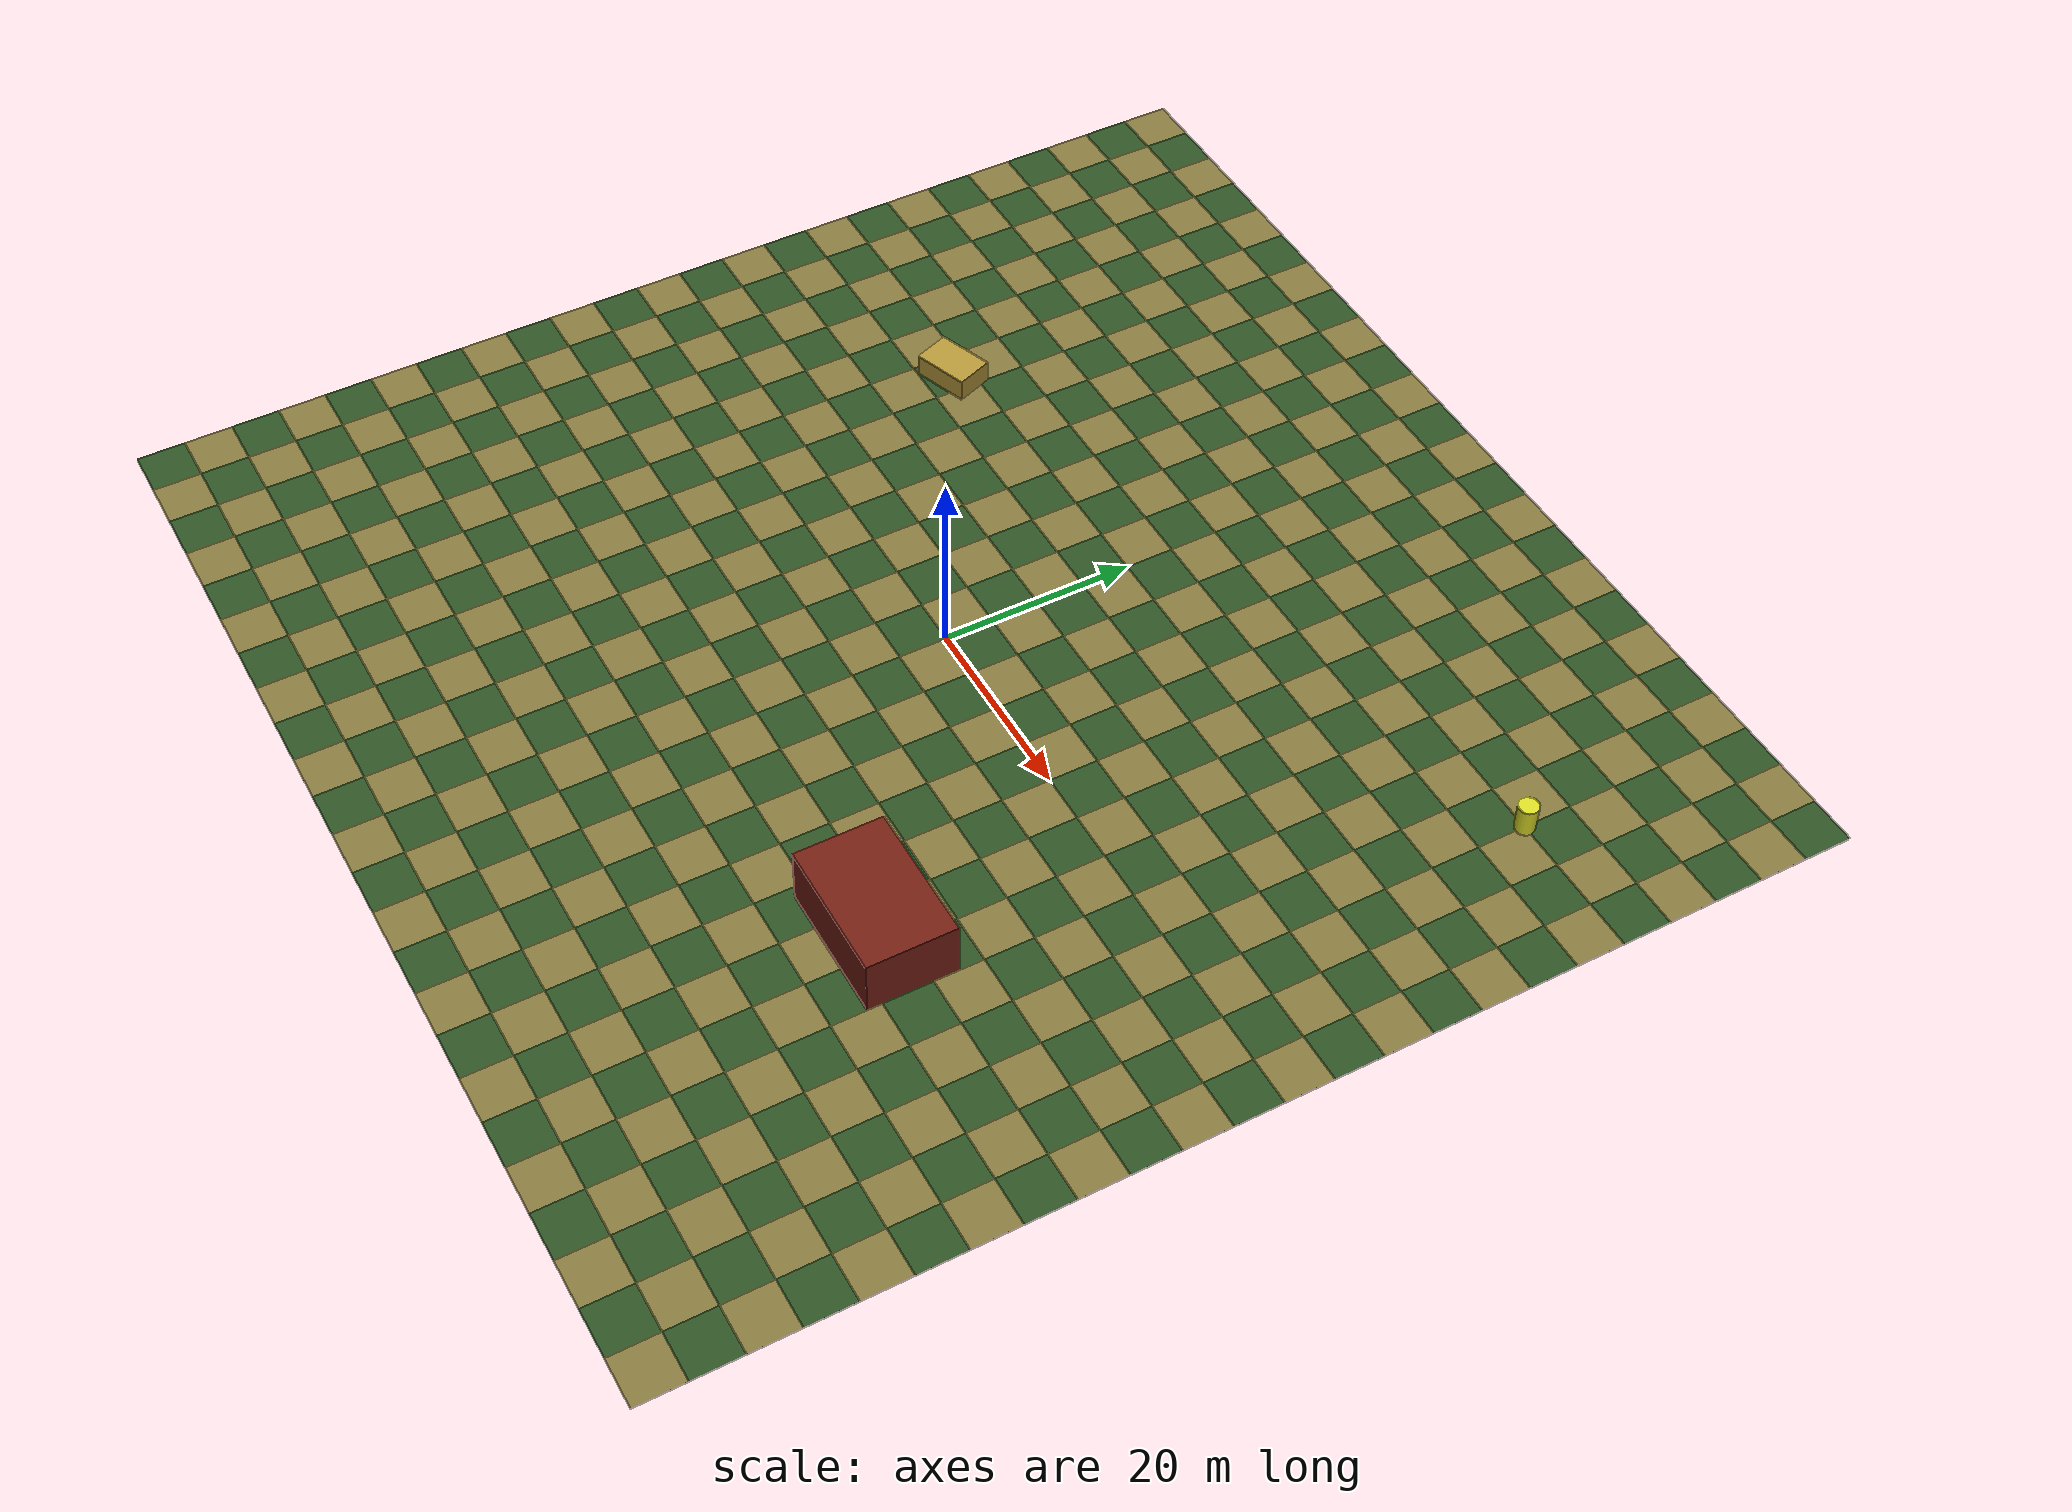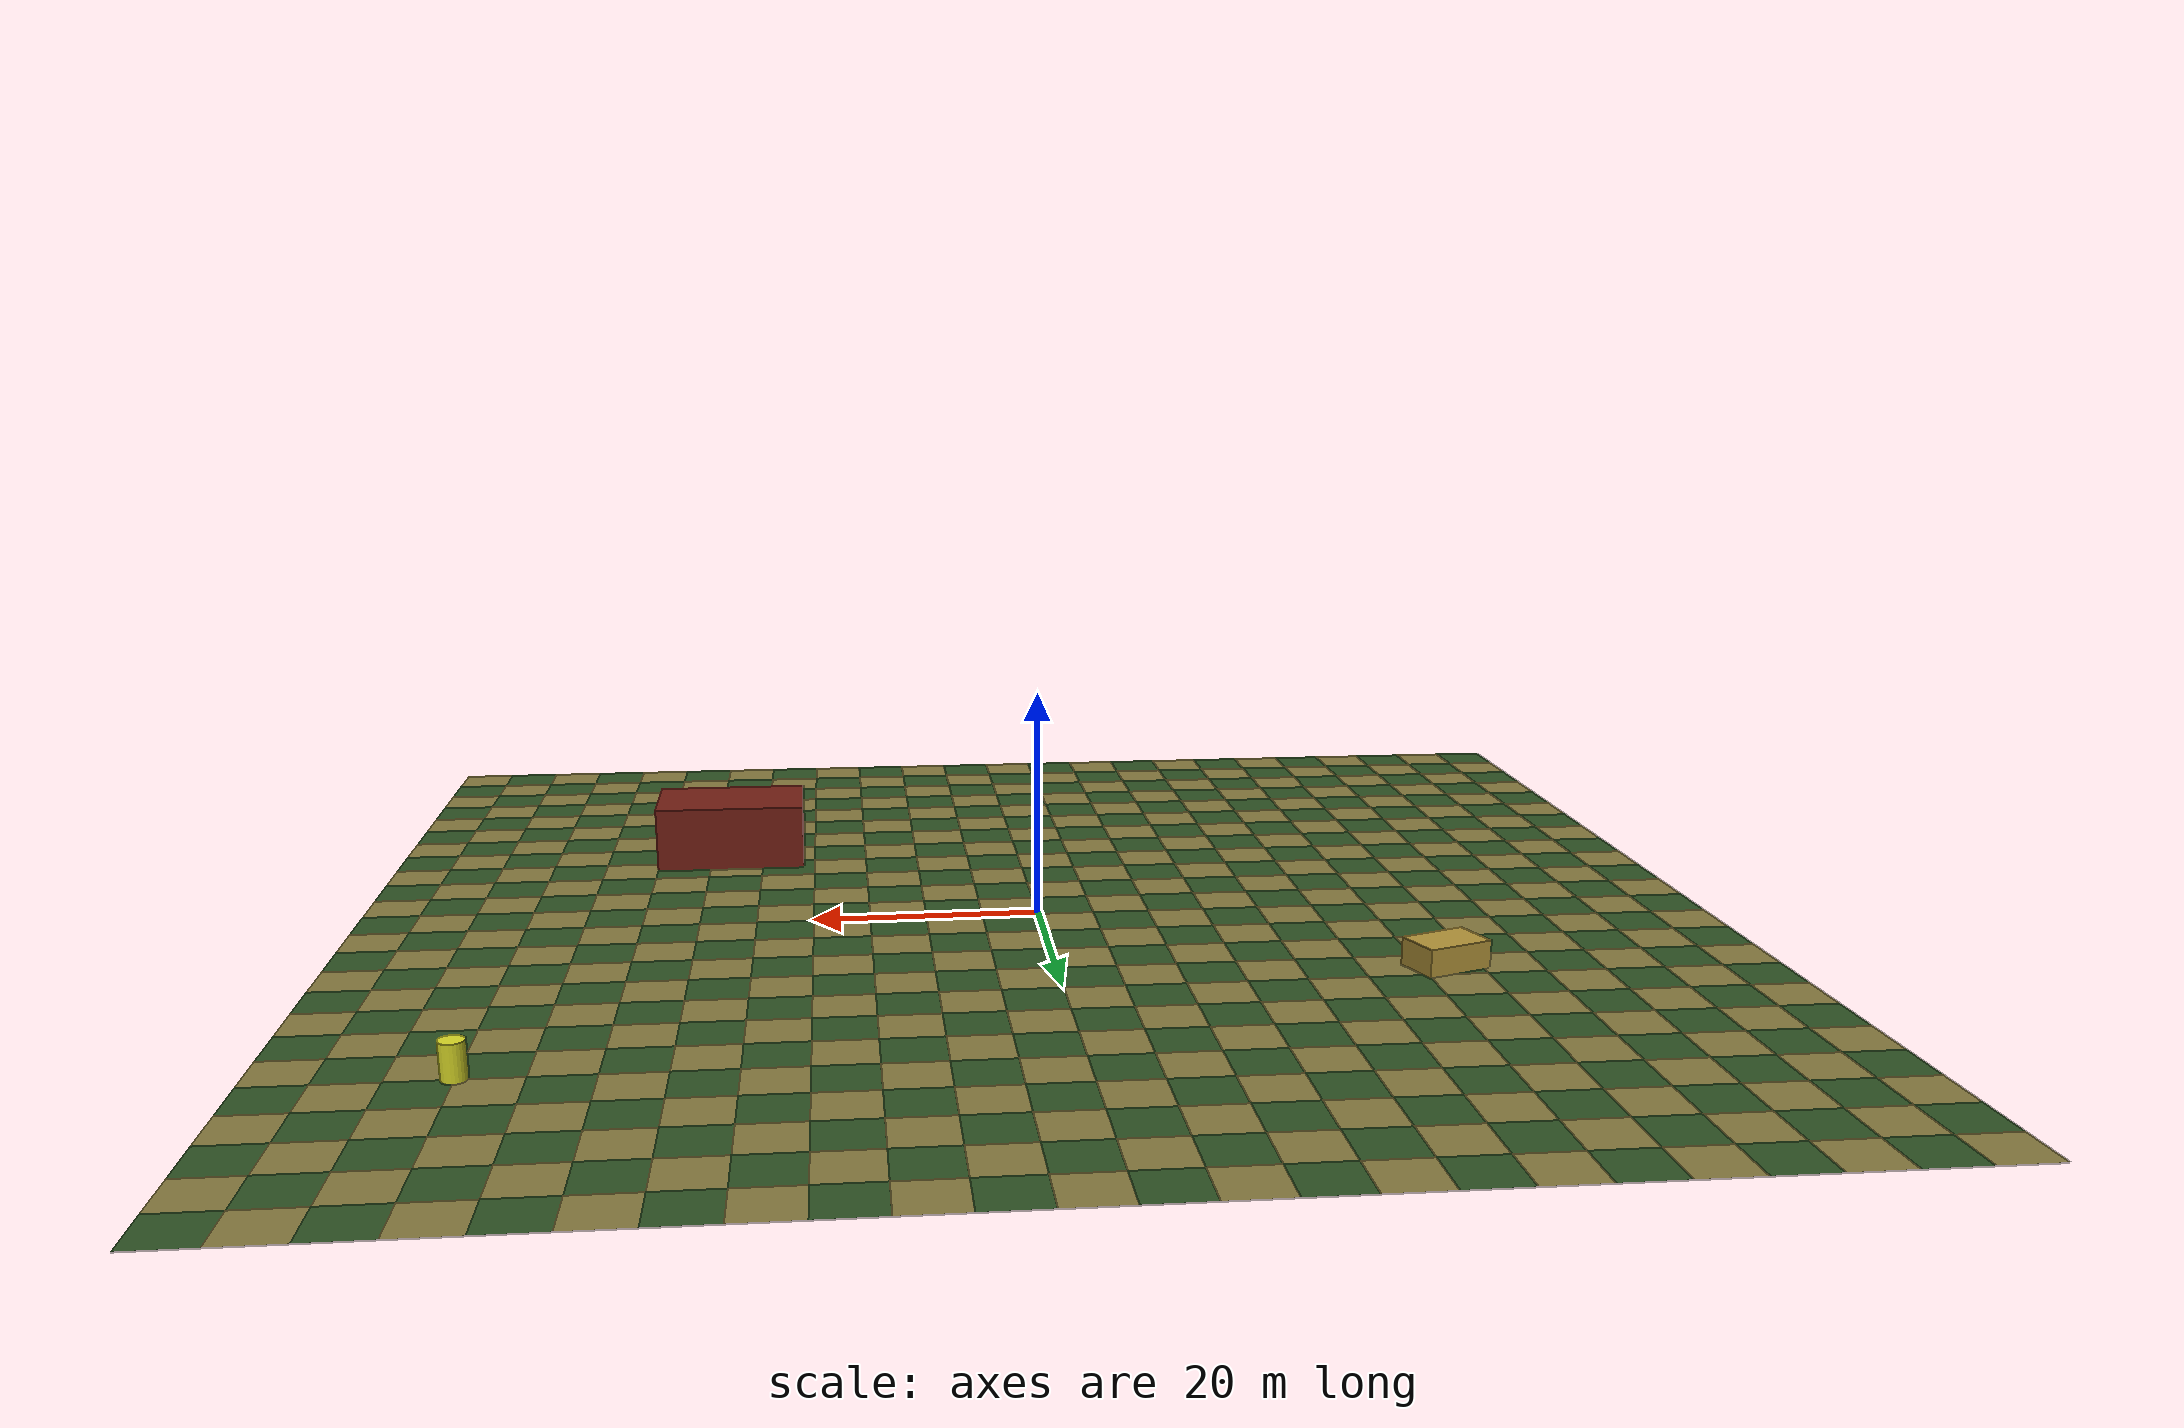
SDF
<?xml version="1.0" ?>
<sdf version="1.9">
  <world name="flat_rural_high_texture_noon">

    <scene>
      <ambient>0.550 0.550 0.550 1.000</ambient>
      <background>0.700 0.820 0.950 1.000</background>
      <shadows>true</shadows>
    </scene>

    <light name="sun" type="directional">
      <cast_shadows>true</cast_shadows>
      <pose>0 0 10 0 0 0</pose>
      <diffuse>0.9 0.86 0.76 1</diffuse>
      <specular>0.2 0.2 0.2 1</specular>
      <direction>-0.35 0.15 -0.92</direction>
    </light>

    <model name="databoss_ground">
      <static>true</static>
      <link name="ground_link">
        <collision name="ground_collision">
          <pose>0 0 -0.005 0 0 0</pose>
          <geometry>
            <box><size>120 120 0.01</size></box>
          </geometry>
        </collision>

        <visual name="tile_0_0">
          <pose>-57.5 -57.5 0.002 0 0 0</pose>
          <geometry>
            <box><size>5 5 0.004</size></box>
          </geometry>

          <material>
            <ambient>0.180 0.320 0.140 1.000</ambient>
            <diffuse>0.180 0.320 0.140 1.000</diffuse>
            <specular>0.05 0.05 0.05 1</specular>
          </material>
          <!-- material_id: tile_0_0 -->

        </visual>

        <visual name="tile_0_1">
          <pose>-57.5 -52.5 0.002 0 0 0</pose>
          <geometry>
            <box><size>5 5 0.004</size></box>
          </geometry>

          <material>
            <ambient>0.520 0.470 0.240 1.000</ambient>
            <diffuse>0.520 0.470 0.240 1.000</diffuse>
            <specular>0.05 0.05 0.05 1</specular>
          </material>
          <!-- material_id: tile_0_1 -->

        </visual>

        <visual name="tile_0_2">
          <pose>-57.5 -47.5 0.002 0 0 0</pose>
          <geometry>
            <box><size>5 5 0.004</size></box>
          </geometry>

          <material>
            <ambient>0.180 0.320 0.140 1.000</ambient>
            <diffuse>0.180 0.320 0.140 1.000</diffuse>
            <specular>0.05 0.05 0.05 1</specular>
          </material>
          <!-- material_id: tile_0_2 -->

        </visual>

        <visual name="tile_0_3">
          <pose>-57.5 -42.5 0.002 0 0 0</pose>
          <geometry>
            <box><size>5 5 0.004</size></box>
          </geometry>

          <material>
            <ambient>0.520 0.470 0.240 1.000</ambient>
            <diffuse>0.520 0.470 0.240 1.000</diffuse>
            <specular>0.05 0.05 0.05 1</specular>
          </material>
          <!-- material_id: tile_0_3 -->

        </visual>

        <visual name="tile_0_4">
          <pose>-57.5 -37.5 0.002 0 0 0</pose>
          <geometry>
            <box><size>5 5 0.004</size></box>
          </geometry>

          <material>
            <ambient>0.180 0.320 0.140 1.000</ambient>
            <diffuse>0.180 0.320 0.140 1.000</diffuse>
            <specular>0.05 0.05 0.05 1</specular>
          </material>
          <!-- material_id: tile_0_4 -->

        </visual>

        <visual name="tile_0_5">
          <pose>-57.5 -32.5 0.002 0 0 0</pose>
          <geometry>
            <box><size>5 5 0.004</size></box>
          </geometry>

          <material>
            <ambient>0.520 0.470 0.240 1.000</ambient>
            <diffuse>0.520 0.470 0.240 1.000</diffuse>
            <specular>0.05 0.05 0.05 1</specular>
          </material>
          <!-- material_id: tile_0_5 -->

        </visual>

        <visual name="tile_0_6">
          <pose>-57.5 -27.5 0.002 0 0 0</pose>
          <geometry>
            <box><size>5 5 0.004</size></box>
          </geometry>

          <material>
            <ambient>0.180 0.320 0.140 1.000</ambient>
            <diffuse>0.180 0.320 0.140 1.000</diffuse>
            <specular>0.05 0.05 0.05 1</specular>
          </material>
          <!-- material_id: tile_0_6 -->

        </visual>

        <visual name="tile_0_7">
          <pose>-57.5 -22.5 0.002 0 0 0</pose>
          <geometry>
            <box><size>5 5 0.004</size></box>
          </geometry>

          <material>
            <ambient>0.520 0.470 0.240 1.000</ambient>
            <diffuse>0.520 0.470 0.240 1.000</diffuse>
            <specular>0.05 0.05 0.05 1</specular>
          </material>
          <!-- material_id: tile_0_7 -->

        </visual>

        <visual name="tile_0_8">
          <pose>-57.5 -17.5 0.002 0 0 0</pose>
          <geometry>
            <box><size>5 5 0.004</size></box>
          </geometry>

          <material>
            <ambient>0.180 0.320 0.140 1.000</ambient>
            <diffuse>0.180 0.320 0.140 1.000</diffuse>
            <specular>0.05 0.05 0.05 1</specular>
          </material>
          <!-- material_id: tile_0_8 -->

        </visual>

        <visual name="tile_0_9">
          <pose>-57.5 -12.5 0.002 0 0 0</pose>
          <geometry>
            <box><size>5 5 0.004</size></box>
          </geometry>

          <material>
            <ambient>0.520 0.470 0.240 1.000</ambient>
            <diffuse>0.520 0.470 0.240 1.000</diffuse>
            <specular>0.05 0.05 0.05 1</specular>
          </material>
          <!-- material_id: tile_0_9 -->

        </visual>

        <visual name="tile_0_10">
          <pose>-57.5 -7.5 0.002 0 0 0</pose>
          <geometry>
            <box><size>5 5 0.004</size></box>
          </geometry>

          <material>
            <ambient>0.180 0.320 0.140 1.000</ambient>
            <diffuse>0.180 0.320 0.140 1.000</diffuse>
            <specular>0.05 0.05 0.05 1</specular>
          </material>
          <!-- material_id: tile_0_10 -->

        </visual>

        <visual name="tile_0_11">
          <pose>-57.5 -2.5 0.002 0 0 0</pose>
          <geometry>
            <box><size>5 5 0.004</size></box>
          </geometry>

          <material>
            <ambient>0.520 0.470 0.240 1.000</ambient>
            <diffuse>0.520 0.470 0.240 1.000</diffuse>
            <specular>0.05 0.05 0.05 1</specular>
          </material>
          <!-- material_id: tile_0_11 -->

        </visual>

        <visual name="tile_0_12">
          <pose>-57.5 2.5 0.002 0 0 0</pose>
          <geometry>
            <box><size>5 5 0.004</size></box>
          </geometry>

          <material>
            <ambient>0.180 0.320 0.140 1.000</ambient>
            <diffuse>0.180 0.320 0.140 1.000</diffuse>
            <specular>0.05 0.05 0.05 1</specular>
          </material>
          <!-- material_id: tile_0_12 -->

        </visual>

        <visual name="tile_0_13">
          <pose>-57.5 7.5 0.002 0 0 0</pose>
          <geometry>
            <box><size>5 5 0.004</size></box>
          </geometry>

          <material>
            <ambient>0.520 0.470 0.240 1.000</ambient>
            <diffuse>0.520 0.470 0.240 1.000</diffuse>
            <specular>0.05 0.05 0.05 1</specular>
          </material>
          <!-- material_id: tile_0_13 -->

        </visual>

        <visual name="tile_0_14">
          <pose>-57.5 12.5 0.002 0 0 0</pose>
          <geometry>
            <box><size>5 5 0.004</size></box>
          </geometry>

          <material>
            <ambient>0.180 0.320 0.140 1.000</ambient>
            <diffuse>0.180 0.320 0.140 1.000</diffuse>
            <specular>0.05 0.05 0.05 1</specular>
          </material>
          <!-- material_id: tile_0_14 -->

        </visual>

        <visual name="tile_0_15">
          <pose>-57.5 17.5 0.002 0 0 0</pose>
          <geometry>
            <box><size>5 5 0.004</size></box>
          </geometry>

          <material>
            <ambient>0.520 0.470 0.240 1.000</ambient>
            <diffuse>0.520 0.470 0.240 1.000</diffuse>
            <specular>0.05 0.05 0.05 1</specular>
          </material>
          <!-- material_id: tile_0_15 -->

        </visual>

        <visual name="tile_0_16">
          <pose>-57.5 22.5 0.002 0 0 0</pose>
          <geometry>
            <box><size>5 5 0.004</size></box>
          </geometry>

          <material>
            <ambient>0.180 0.320 0.140 1.000</ambient>
            <diffuse>0.180 0.320 0.140 1.000</diffuse>
            <specular>0.05 0.05 0.05 1</specular>
          </material>
          <!-- material_id: tile_0_16 -->

        </visual>

        <visual name="tile_0_17">
          <pose>-57.5 27.5 0.002 0 0 0</pose>
          <geometry>
            <box><size>5 5 0.004</size></box>
          </geometry>

          <material>
            <ambient>0.520 0.470 0.240 1.000</ambient>
            <diffuse>0.520 0.470 0.240 1.000</diffuse>
            <specular>0.05 0.05 0.05 1</specular>
          </material>
          <!-- material_id: tile_0_17 -->

        </visual>

        <visual name="tile_0_18">
          <pose>-57.5 32.5 0.002 0 0 0</pose>
          <geometry>
            <box><size>5 5 0.004</size></box>
          </geometry>

          <material>
            <ambient>0.180 0.320 0.140 1.000</ambient>
            <diffuse>0.180 0.320 0.140 1.000</diffuse>
            <specular>0.05 0.05 0.05 1</specular>
          </material>
          <!-- material_id: tile_0_18 -->

        </visual>

        <visual name="tile_0_19">
          <pose>-57.5 37.5 0.002 0 0 0</pose>
          <geometry>
            <box><size>5 5 0.004</size></box>
          </geometry>

          <material>
            <ambient>0.520 0.470 0.240 1.000</ambient>
            <diffuse>0.520 0.470 0.240 1.000</diffuse>
            <specular>0.05 0.05 0.05 1</specular>
          </material>
          <!-- material_id: tile_0_19 -->

        </visual>

        <visual name="tile_0_20">
          <pose>-57.5 42.5 0.002 0 0 0</pose>
          <geometry>
            <box><size>5 5 0.004</size></box>
          </geometry>

          <material>
            <ambient>0.180 0.320 0.140 1.000</ambient>
            <diffuse>0.180 0.320 0.140 1.000</diffuse>
            <specular>0.05 0.05 0.05 1</specular>
          </material>
          <!-- material_id: tile_0_20 -->

        </visual>

        <visual name="tile_0_21">
          <pose>-57.5 47.5 0.002 0 0 0</pose>
          <geometry>
            <box><size>5 5 0.004</size></box>
          </geometry>

          <material>
            <ambient>0.520 0.470 0.240 1.000</ambient>
            <diffuse>0.520 0.470 0.240 1.000</diffuse>
            <specular>0.05 0.05 0.05 1</specular>
          </material>
          <!-- material_id: tile_0_21 -->

        </visual>

        <visual name="tile_0_22">
          <pose>-57.5 52.5 0.002 0 0 0</pose>
          <geometry>
            <box><size>5 5 0.004</size></box>
          </geometry>

          <material>
            <ambient>0.180 0.320 0.140 1.000</ambient>
            <diffuse>0.180 0.320 0.140 1.000</diffuse>
            <specular>0.05 0.05 0.05 1</specular>
          </material>
          <!-- material_id: tile_0_22 -->

        </visual>

        <visual name="tile_0_23">
          <pose>-57.5 57.5 0.002 0 0 0</pose>
          <geometry>
            <box><size>5 5 0.004</size></box>
          </geometry>

          <material>
            <ambient>0.520 0.470 0.240 1.000</ambient>
            <diffuse>0.520 0.470 0.240 1.000</diffuse>
            <specular>0.05 0.05 0.05 1</specular>
          </material>
          <!-- material_id: tile_0_23 -->

        </visual>

        <visual name="tile_1_0">
          <pose>-52.5 -57.5 0.002 0 0 0</pose>
          <geometry>
            <box><size>5 5 0.004</size></box>
          </geometry>

          <material>
            <ambient>0.520 0.470 0.240 1.000</ambient>
            <diffuse>0.520 0.470 0.240 1.000</diffuse>
            <specular>0.05 0.05 0.05 1</specular>
          </material>
          <!-- material_id: tile_1_0 -->

        </visual>

        <visual name="tile_1_1">
          <pose>-52.5 -52.5 0.002 0 0 0</pose>
          <geometry>
            <box><size>5 5 0.004</size></box>
          </geometry>

          <material>
            <ambient>0.180 0.320 0.140 1.000</ambient>
            <diffuse>0.180 0.320 0.140 1.000</diffuse>
            <specular>0.05 0.05 0.05 1</specular>
          </material>
          <!-- material_id: tile_1_1 -->

        </visual>

        <visual name="tile_1_2">
          <pose>-52.5 -47.5 0.002 0 0 0</pose>
          <geometry>
            <box><size>5 5 0.004</size></box>
          </geometry>

          <material>
            <ambient>0.520 0.470 0.240 1.000</ambient>
            <diffuse>0.520 0.470 0.240 1.000</diffuse>
            <specular>0.05 0.05 0.05 1</specular>
          </material>
          <!-- material_id: tile_1_2 -->

        </visual>

        <visual name="tile_1_3">
          <pose>-52.5 -42.5 0.002 0 0 0</pose>
          <geometry>
            <box><size>5 5 0.004</size></box>
          </geometry>

          <material>
            <ambient>0.180 0.320 0.140 1.000</ambient>
            <diffuse>0.180 0.320 0.140 1.000</diffuse>
            <specular>0.05 0.05 0.05 1</specular>
          </material>
          <!-- material_id: tile_1_3 -->

        </visual>

        <visual name="tile_1_4">
          <pose>-52.5 -37.5 0.002 0 0 0</pose>
          <geometry>
            <box><size>5 5 0.004</size></box>
          </geometry>

          <material>
            <ambient>0.520 0.470 0.240 1.000</ambient>
            <diffuse>0.520 0.470 0.240 1.000</diffuse>
            <specular>0.05 0.05 0.05 1</specular>
          </material>
          <!-- material_id: tile_1_4 -->

        </visual>

        <visual name="tile_1_5">
          <pose>-52.5 -32.5 0.002 0 0 0</pose>
          <geometry>
            <box><size>5 5 0.004</size></box>
          </geometry>

          <material>
            <ambient>0.180 0.320 0.140 1.000</ambient>
            <diffuse>0.180 0.320 0.140 1.000</diffuse>
            <specular>0.05 0.05 0.05 1</specular>
          </material>
          <!-- material_id: tile_1_5 -->

        </visual>

        <visual name="tile_1_6">
          <pose>-52.5 -27.5 0.002 0 0 0</pose>
          <geometry>
            <box><size>5 5 0.004</size></box>
          </geometry>

          <material>
            <ambient>0.520 0.470 0.240 1.000</ambient>
            <diffuse>0.520 0.470 0.240 1.000</diffuse>
            <specular>0.05 0.05 0.05 1</specular>
          </material>
          <!-- material_id: tile_1_6 -->

        </visual>

        <visual name="tile_1_7">
          <pose>-52.5 -22.5 0.002 0 0 0</pose>
          <geometry>
            <box><size>5 5 0.004</size></box>
          </geometry>

          <material>
            <ambient>0.180 0.320 0.140 1.000</ambient>
            <diffuse>0.180 0.320 0.140 1.000</diffuse>
            <specular>0.05 0.05 0.05 1</specular>
          </material>
          <!-- material_id: tile_1_7 -->

        </visual>

        <visual name="tile_1_8">
          <pose>-52.5 -17.5 0.002 0 0 0</pose>
          <geometry>
            <box><size>5 5 0.004</size></box>
          </geometry>

          <material>
            <ambient>0.520 0.470 0.240 1.000</ambient>
            <diffuse>0.520 0.470 0.240 1.000</diffuse>
            <specular>0.05 0.05 0.05 1</specular>
          </material>
          <!-- material_id: tile_1_8 -->

        </visual>

        <visual name="tile_1_9">
          <pose>-52.5 -12.5 0.002 0 0 0</pose>
          <geometry>
            <box><size>5 5 0.004</size></box>
          </geometry>

          <material>
            <ambient>0.180 0.320 0.140 1.000</ambient>
            <diffuse>0.180 0.320 0.140 1.000</diffuse>
            <specular>0.05 0.05 0.05 1</specular>
          </material>
          <!-- material_id: tile_1_9 -->

        </visual>

        <visual name="tile_1_10">
          <pose>-52.5 -7.5 0.002 0 0 0</pose>
          <geometry>
            <box><size>5 5 0.004</size></box>
          </geometry>

          <material>
            <ambient>0.520 0.470 0.240 1.000</ambient>
            <diffuse>0.520 0.470 0.240 1.000</diffuse>
            <specular>0.05 0.05 0.05 1</specular>
          </material>
          <!-- material_id: tile_1_10 -->

        </visual>

        <visual name="tile_1_11">
          <pose>-52.5 -2.5 0.002 0 0 0</pose>
          <geometry>
            <box><size>5 5 0.004</size></box>
          </geometry>

          <material>
            <ambient>0.180 0.320 0.140 1.000</ambient>
            <diffuse>0.180 0.320 0.140 1.000</diffuse>
            <specular>0.05 0.05 0.05 1</specular>
          </material>
          <!-- material_id: tile_1_11 -->

        </visual>

        <visual name="tile_1_12">
          <pose>-52.5 2.5 0.002 0 0 0</pose>
          <geometry>
            <box><size>5 5 0.004</size></box>
          </geometry>

          <material>
            <ambient>0.520 0.470 0.240 1.000</ambient>
            <diffuse>0.520 0.470 0.240 1.000</diffuse>
            <specular>0.05 0.05 0.05 1</specular>
          </material>
          <!-- material_id: tile_1_12 -->

        </visual>

        <visual name="tile_1_13">
          <pose>-52.5 7.5 0.002 0 0 0</pose>
          <geometry>
            <box><size>5 5 0.004</size></box>
          </geometry>

          <material>
            <ambient>0.180 0.320 0.140 1.000</ambient>
            <diffuse>0.180 0.320 0.140 1.000</diffuse>
            <specular>0.05 0.05 0.05 1</specular>
          </material>
          <!-- material_id: tile_1_13 -->

        </visual>

        <visual name="tile_1_14">
          <pose>-52.5 12.5 0.002 0 0 0</pose>
          <geometry>
            <box><size>5 5 0.004</size></box>
          </geometry>

          <material>
            <ambient>0.520 0.470 0.240 1.000</ambient>
            <diffuse>0.520 0.470 0.240 1.000</diffuse>
            <specular>0.05 0.05 0.05 1</specular>
          </material>
          <!-- material_id: tile_1_14 -->

        </visual>

        <visual name="tile_1_15">
          <pose>-52.5 17.5 0.002 0 0 0</pose>
          <geometry>
            <box><size>5 5 0.004</size></box>
          </geometry>

          <material>
            <ambient>0.180 0.320 0.140 1.000</ambient>
            <diffuse>0.180 0.320 0.140 1.000</diffuse>
            <specular>0.05 0.05 0.05 1</specular>
          </material>
          <!-- material_id: tile_1_15 -->

        </visual>

        <visual name="tile_1_16">
          <pose>-52.5 22.5 0.002 0 0 0</pose>
          <geometry>
            <box><size>5 5 0.004</size></box>
          </geometry>

          <material>
            <ambient>0.520 0.470 0.240 1.000</ambient>
            <diffuse>0.520 0.470 0.240 1.000</diffuse>
            <specular>0.05 0.05 0.05 1</specular>
          </material>
          <!-- material_id: tile_1_16 -->

        </visual>

        <visual name="tile_1_17">
          <pose>-52.5 27.5 0.002 0 0 0</pose>
          <geometry>
            <box><size>5 5 0.004</size></box>
          </geometry>

          <material>
            <ambient>0.180 0.320 0.140 1.000</ambient>
            <diffuse>0.180 0.320 0.140 1.000</diffuse>
            <specular>0.05 0.05 0.05 1</specular>
          </material>
          <!-- material_id: tile_1_17 -->

        </visual>

        <visual name="tile_1_18">
          <pose>-52.5 32.5 0.002 0 0 0</pose>
          <geometry>
            <box><size>5 5 0.004</size></box>
          </geometry>

          <material>
            <ambient>0.520 0.470 0.240 1.000</ambient>
            <diffuse>0.520 0.470 0.240 1.000</diffuse>
            <specular>0.05 0.05 0.05 1</specular>
          </material>
          <!-- material_id: tile_1_18 -->

        </visual>

        <visual name="tile_1_19">
          <pose>-52.5 37.5 0.002 0 0 0</pose>
          <geometry>
            <box><size>5 5 0.004</size></box>
          </geometry>

          <material>
            <ambient>0.180 0.320 0.140 1.000</ambient>
            <diffuse>0.180 0.320 0.140 1.000</diffuse>
            <specular>0.05 0.05 0.05 1</specular>
          </material>
          <!-- material_id: tile_1_19 -->

        </visual>

        <visual name="tile_1_20">
          <pose>-52.5 42.5 0.002 0 0 0</pose>
          <geometry>
            <box><size>5 5 0.004</size></box>
          </geometry>

          <material>
            <ambient>0.520 0.470 0.240 1.000</ambient>
            <diffuse>0.520 0.470 0.240 1.000</diffuse>
            <specular>0.05 0.05 0.05 1</specular>
          </material>
          <!-- material_id: tile_1_20 -->

        </visual>

        <visual name="tile_1_21">
          <pose>-52.5 47.5 0.002 0 0 0</pose>
          <geometry>
            <box><size>5 5 0.004</size></box>
          </geometry>

          <material>
            <ambient>0.180 0.320 0.140 1.000</ambient>
            <diffuse>0.180 0.320 0.140 1.000</diffuse>
            <specular>0.05 0.05 0.05 1</specular>
          </material>
          <!-- material_id: tile_1_21 -->

        </visual>

        <visual name="tile_1_22">
          <pose>-52.5 52.5 0.002 0 0 0</pose>
          <geometry>
            <box><size>5 5 0.004</size></box>
          </geometry>

          <material>
            <ambient>0.520 0.470 0.240 1.000</ambient>
            <diffuse>0.520 0.470 0.240 1.000</diffuse>
            <specular>0.05 0.05 0.05 1</specular>
          </material>
          <!-- material_id: tile_1_22 -->

        </visual>

        <visual name="tile_1_23">
          <pose>-52.5 57.5 0.002 0 0 0</pose>
          <geometry>
            <box><size>5 5 0.004</size></box>
          </geometry>

          <material>
            <ambient>0.180 0.320 0.140 1.000</ambient>
            <diffuse>0.180 0.320 0.140 1.000</diffuse>
            <specular>0.05 0.05 0.05 1</specular>
          </material>
          <!-- material_id: tile_1_23 -->

        </visual>

        <visual name="tile_2_0">
          <pose>-47.5 -57.5 0.002 0 0 0</pose>
          <geometry>
            <box><size>5 5 0.004</size></box>
          </geometry>

          <material>
            <ambient>0.180 0.320 0.140 1.000</ambient>
            <diffuse>0.180 0.320 0.140 1.000</diffuse>
            <specular>0.05 0.05 0.05 1</specular>
          </material>
          <!-- material_id: tile_2_0 -->

        </visual>

        <visual name="tile_2_1">
          <pose>-47.5 -52.5 0.002 0 0 0</pose>
          <geometry>
            <box><size>5 5 0.004</size></box>
          </geometry>

          <material>
            <ambient>0.520 0.470 0.240 1.000</ambient>
            <diffuse>0.520 0.470 0.240 1.000</diffuse>
            <specular>0.05 0.05 0.05 1</specular>
          </material>
          <!-- material_id: tile_2_1 -->

        </visual>

        <visual name="tile_2_2">
          <pose>-47.5 -47.5 0.002 0 0 0</pose>
          <geometry>
            <box><size>5 5 0.004</size></box>
          </geometry>

          <material>
            <ambient>0.180 0.320 0.140 1.000</ambient>
            <diffuse>0.180 0.320 0.140 1.000</diffuse>
            <specular>0.05 0.05 0.05 1</specular>
          </material>
          <!-- material_id: tile_2_2 -->

        </visual>

        <visual name="tile_2_3">
          <pose>-47.5 -42.5 0.002 0 0 0</pose>
          <geometry>
            <box><size>5 5 0.004</size></box>
          </geometry>

          <material>
            <ambient>0.520 0.470 0.240 1.000</ambient>
            <diffuse>0.520 0.470 0.240 1.000</diffuse>
            <specular>0.05 0.05 0.05 1</specular>
          </material>
          <!-- material_id: tile_2_3 -->

        </visual>

        <visual name="tile_2_4">
          <pose>-47.5 -37.5 0.002 0 0 0</pose>
          <geometry>
            <box><size>5 5 0.004</size></box>
          </geometry>

          <material>
            <ambient>0.180 0.320 0.140 1.000</ambient>
            <diffuse>0.180 0.320 0.140 1.000</diffuse>
            <specular>0.05 0.05 0.05 1</specular>
          </material>
          <!-- material_id: tile_2_4 -->

        </visual>

        <visual name="tile_2_5">
          <pose>-47.5 -32.5 0.002 0 0 0</pose>
          <geometry>
            <box><size>5 5 0.004</size></box>
          </geometry>

          <material>
            <ambient>0.520 0.470 0.240 1.000</ambient>
            <diffuse>0.520 0.470 0.240 1.000</diffuse>
            <specular>0.05 0.05 0.05 1</specular>
          </material>
          <!-- material_id: tile_2_5 -->

        </visual>

        <visual name="tile_2_6">
          <pose>-47.5 -27.5 0.002 0 0 0</pose>
          <geometry>
            <box><size>5 5 0.004</size></box>
          </geometry>

          <material>
            <ambient>0.180 0.320 0.140 1.000</ambient>
            <diffuse>0.180 0.320 0.140 1.000</diffuse>
            <specular>0.05 0.05 0.05 1</specular>
          </material>
          <!-- material_id: tile_2_6 -->

        </visual>

        <visual name="tile_2_7">
          <pose>-47.5 -22.5 0.002 0 0 0</pose>
          <geometry>
            <box><size>5 5 0.004</size></box>
          </geometry>

          <material>
            <ambient>0.520 0.470 0.240 1.000</ambient>
            <diffuse>0.520 0.470 0.240 1.000</diffuse>
            <specular>0.05 0.05 0.05 1</specular>
          </material>
          <!-- material_id: tile_2_7 -->

        </visual>

        <visual name="tile_2_8">
          <pose>-47.5 -17.5 0.002 0 0 0</pose>
          <geometry>
            <box><size>5 5 0.004</size></box>
          </geometry>

          <material>
            <ambient>0.180 0.320 0.140 1.000</ambient>
            <diffuse>0.180 0.320 0.140 1.000</diffuse>
            <specular>0.05 0.05 0.05 1</specular>
          </material>
          <!-- material_id: tile_2_8 -->

        </visual>

        <visual name="tile_2_9">
          <pose>-47.5 -12.5 0.002 0 0 0</pose>
          <geometry>
            <box><size>5 5 0.004</size></box>
          </geometry>

          <material>
            <ambient>0.520 0.470 0.240 1.000</ambient>
            <diffuse>0.520 0.470 0.240 1.000</diffuse>
            <specular>0.05 0.05 0.05 1</specular>
          </material>
          <!-- material_id: tile_2_9 -->

        </visual>

        <visual name="tile_2_10">
          <pose>-47.5 -7.5 0.002 0 0 0</pose>
          <geometry>
            <box><size>5 5 0.004</size></box>
          </geometry>

          <material>
            <ambient>0.180 0.320 0.140 1.000</ambient>
            <diffuse>0.180 0.320 0.140 1.000</diffuse>
            <specular>0.05 0.05 0.05 1</specular>
          </material>
          <!-- material_id: tile_2_10 -->

        </visual>

        <visual name="tile_2_11">
          <pose>-47.5 -2.5 0.002 0 0 0</pose>
          <geometry>
            <box><size>5 5 0.004</size></box>
          </geometry>

          <material>
            <ambient>0.520 0.470 0.240 1.000</ambient>
            <diffuse>0.520 0.470 0.240 1.000</diffuse>
            <specular>0.05 0.05 0.05 1</specular>
          </material>
          <!-- material_id: tile_2_11 -->

        </visual>

        <visual name="tile_2_12">
          <pose>-47.5 2.5 0.002 0 0 0</pose>
          <geometry>
            <box><size>5 5 0.004</size></box>
          </geometry>

          <material>
            <ambient>0.180 0.320 0.140 1.000</ambient>
            <diffuse>0.180 0.320 0.140 1.000</diffuse>
            <specular>0.05 0.05 0.05 1</specular>
          </material>
          <!-- material_id: tile_2_12 -->

        </visual>

        <visual name="tile_2_13">
          <pose>-47.5 7.5 0.002 0 0 0</pose>
          <geometry>
            <box><size>5 5 0.004</size></box>
          </geometry>

          <material>
            <ambient>0.520 0.470 0.240 1.000</ambient>
            <diffuse>0.520 0.470 0.240 1.000</diffuse>
            <specular>0.05 0.05 0.05 1</specular>
          </material>
          <!-- material_id: tile_2_13 -->

        </visual>

        <visual name="tile_2_14">
          <pose>-47.5 12.5 0.002 0 0 0</pose>
          <geometry>
            <box><size>5 5 0.004</size></box>
          </geometry>

          <material>
            <ambient>0.180 0.320 0.140 1.000</ambient>
            <diffuse>0.180 0.320 0.140 1.000</diffuse>
            <specular>0.05 0.05 0.05 1</specular>
          </material>
          <!-- material_id: tile_2_14 -->

        </visual>

        <visual name="tile_2_15">
          <pose>-47.5 17.5 0.002 0 0 0</pose>
          <geometry>
            <box><size>5 5 0.004</size></box>
          </geometry>

          <material>
            <ambient>0.520 0.470 0.240 1.000</ambient>
            <diffuse>0.520 0.470 0.240 1.000</diffuse>
            <specular>0.05 0.05 0.05 1</specular>
          </material>
          <!-- material_id: tile_2_15 -->

        </visual>

        <visual name="tile_2_16">
          <pose>-47.5 22.5 0.002 0 0 0</pose>
          <geometry>
            <box><size>5 5 0.004</size></box>
          </geometry>

          <material>
            <ambient>0.180 0.320 0.140 1.000</ambient>
            <diffuse>0.180 0.320 0.140 1.000</diffuse>
            <specular>0.05 0.05 0.05 1</specular>
          </material>
          <!-- material_id: tile_2_16 -->

        </visual>

        <visual name="tile_2_17">
          <pose>-47.5 27.5 0.002 0 0 0</pose>
          <geometry>
            <box><size>5 5 0.004</size></box>
          </geometry>

          <material>
            <ambient>0.520 0.470 0.240 1.000</ambient>
            <diffuse>0.520 0.470 0.240 1.000</diffuse>
            <specular>0.05 0.05 0.05 1</specular>
          </material>
          <!-- material_id: tile_2_17 -->

        </visual>

        <visual name="tile_2_18">
          <pose>-47.5 32.5 0.002 0 0 0</pose>
          <geometry>
            <box><size>5 5 0.004</size></box>
          </geometry>

          <material>
            <ambient>0.180 0.320 0.140 1.000</ambient>
            <diffuse>0.180 0.320 0.140 1.000</diffuse>
            <specular>0.05 0.05 0.05 1</specular>
          </material>
          <!-- material_id: tile_2_18 -->

        </visual>

        <visual name="tile_2_19">
          <pose>-47.5 37.5 0.002 0 0 0</pose>
          <geometry>
            <box><size>5 5 0.004</size></box>
          </geometry>

          <material>
            <ambient>0.520 0.470 0.240 1.000</ambient>
            <diffuse>0.520 0.470 0.240 1.000</diffuse>
            <specular>0.05 0.05 0.05 1</specular>
          </material>
          <!-- material_id: tile_2_19 -->

        </visual>

        <visual name="tile_2_20">
          <pose>-47.5 42.5 0.002 0 0 0</pose>
          <geometry>
            <box><size>5 5 0.004</size></box>
          </geometry>

          <material>
            <ambient>0.180 0.320 0.140 1.000</ambient>
            <diffuse>0.180 0.320 0.140 1.000</diffuse>
            <specular>0.05 0.05 0.05 1</specular>
          </material>
          <!-- material_id: tile_2_20 -->

        </visual>

        <visual name="tile_2_21">
          <pose>-47.5 47.5 0.002 0 0 0</pose>
          <geometry>
            <box><size>5 5 0.004</size></box>
          </geometry>

          <material>
            <ambient>0.520 0.470 0.240 1.000</ambient>
            <diffuse>0.520 0.470 0.240 1.000</diffuse>
            <specular>0.05 0.05 0.05 1</specular>
          </material>
          <!-- material_id: tile_2_21 -->

        </visual>

        <visual name="tile_2_22">
          <pose>-47.5 52.5 0.002 0 0 0</pose>
          <geometry>
            <box><size>5 5 0.004</size></box>
          </geometry>

          <material>
            <ambient>0.180 0.320 0.140 1.000</ambient>
            <diffuse>0.180 0.320 0.140 1.000</diffuse>
            <specular>0.05 0.05 0.05 1</specular>
          </material>
          <!-- material_id: tile_2_22 -->

        </visual>

        <visual name="tile_2_23">
          <pose>-47.5 57.5 0.002 0 0 0</pose>
          <geometry>
            <box><size>5 5 0.004</size></box>
          </geometry>

          <material>
            <ambient>0.520 0.470 0.240 1.000</ambient>
            <diffuse>0.520 0.470 0.240 1.000</diffuse>
            <specular>0.05 0.05 0.05 1</specular>
          </material>
          <!-- material_id: tile_2_23 -->

        </visual>

        <visual name="tile_3_0">
          <pose>-42.5 -57.5 0.002 0 0 0</pose>
          <geometry>
            <box><size>5 5 0.004</size></box>
          </geometry>

          <material>
            <ambient>0.520 0.470 0.240 1.000</ambient>
            <diffuse>0.520 0.470 0.240 1.000</diffuse>
            <specular>0.05 0.05 0.05 1</specular>
          </material>
          <!-- material_id: tile_3_0 -->

        </visual>

        <visual name="tile_3_1">
          <pose>-42.5 -52.5 0.002 0 0 0</pose>
          <geometry>
            <box><size>5 5 0.004</size></box>
          </geometry>

          <material>
            <ambient>0.180 0.320 0.140 1.000</ambient>
            <diffuse>0.180 0.320 0.140 1.000</diffuse>
            <specular>0.05 0.05 0.05 1</specular>
          </material>
          <!-- material_id: tile_3_1 -->

        </visual>

        <visual name="tile_3_2">
          <pose>-42.5 -47.5 0.002 0 0 0</pose>
          <geometry>
            <box><size>5 5 0.004</size></box>
          </geometry>

          <material>
            <ambient>0.520 0.470 0.240 1.000</ambient>
            <diffuse>0.520 0.470 0.240 1.000</diffuse>
            <specular>0.05 0.05 0.05 1</specular>
          </material>
          <!-- material_id: tile_3_2 -->

        </visual>

        <visual name="tile_3_3">
          <pose>-42.5 -42.5 0.002 0 0 0</pose>
          <geometry>
            <box><size>5 5 0.004</size></box>
          </geometry>

          <material>
            <ambient>0.180 0.320 0.140 1.000</ambient>
            <diffuse>0.180 0.320 0.140 1.000</diffuse>
            <specular>0.05 0.05 0.05 1</specular>
          </material>
          <!-- material_id: tile_3_3 -->

        </visual>

        <visual name="tile_3_4">
          <pose>-42.5 -37.5 0.002 0 0 0</pose>
          <geometry>
            <box><size>5 5 0.004</size></box>
          </geometry>

          <material>
            <ambient>0.520 0.470 0.240 1.000</ambient>
            <diffuse>0.520 0.470 0.240 1.000</diffuse>
            <specular>0.05 0.05 0.05 1</specular>
          </material>
          <!-- material_id: tile_3_4 -->

        </visual>

        <visual name="tile_3_5">
          <pose>-42.5 -32.5 0.002 0 0 0</pose>
          <geometry>
            <box><size>5 5 0.004</size></box>
          </geometry>

          <material>
            <ambient>0.180 0.320 0.140 1.000</ambient>
            <diffuse>0.180 0.320 0.140 1.000</diffuse>
            <specular>0.05 0.05 0.05 1</specular>
          </material>
          <!-- material_id: tile_3_5 -->

        </visual>

        <visual name="tile_3_6">
          <pose>-42.5 -27.5 0.002 0 0 0</pose>
          <geometry>
            <box><size>5 5 0.004</size></box>
          </geometry>

          <material>
            <ambient>0.520 0.470 0.240 1.000</ambient>
            <diffuse>0.520 0.470 0.240 1.000</diffuse>
            <specular>0.05 0.05 0.05 1</specular>
          </material>
          <!-- material_id: tile_3_6 -->

        </visual>

        <visual name="tile_3_7">
          <pose>-42.5 -22.5 0.002 0 0 0</pose>
          <geometry>
            <box><size>5 5 0.004</size></box>
          </geometry>

          <material>
            <ambient>0.180 0.320 0.140 1.000</ambient>
            <diffuse>0.180 0.320 0.140 1.000</diffuse>
            <specular>0.05 0.05 0.05 1</specular>
          </material>
          <!-- material_id: tile_3_7 -->

        </visual>

        <visual name="tile_3_8">
          <pose>-42.5 -17.5 0.002 0 0 0</pose>
          <geometry>
            <box><size>5 5 0.004</size></box>
          </geometry>

          <material>
            <ambient>0.520 0.470 0.240 1.000</ambient>
            <diffuse>0.520 0.470 0.240 1.000</diffuse>
            <specular>0.05 0.05 0.05 1</specular>
          </material>
          <!-- material_id: tile_3_8 -->

        </visual>

        <visual name="tile_3_9">
          <pose>-42.5 -12.5 0.002 0 0 0</pose>
          <geometry>
            <box><size>5 5 0.004</size></box>
          </geometry>

          <material>
            <ambient>0.180 0.320 0.140 1.000</ambient>
            <diffuse>0.180 0.320 0.140 1.000</diffuse>
            <specular>0.05 0.05 0.05 1</specular>
          </material>
          <!-- material_id: tile_3_9 -->

        </visual>

        <visual name="tile_3_10">
          <pose>-42.5 -7.5 0.002 0 0 0</pose>
          <geometry>
            <box><size>5 5 0.004</size></box>
          </geometry>

          <material>
            <ambient>0.520 0.470 0.240 1.000</ambient>
            <diffuse>0.520 0.470 0.240 1.000</diffuse>
            <specular>0.05 0.05 0.05 1</specular>
          </material>
          <!-- material_id: tile_3_10 -->

        </visual>

        <visual name="tile_3_11">
          <pose>-42.5 -2.5 0.002 0 0 0</pose>
          <geometry>
            <box><size>5 5 0.004</size></box>
          </geometry>

          <material>
            <ambient>0.180 0.320 0.140 1.000</ambient>
            <diffuse>0.180 0.320 0.140 1.000</diffuse>
            <specular>0.05 0.05 0.05 1</specular>
          </material>
          <!-- material_id: tile_3_11 -->

        </visual>

        <visual name="tile_3_12">
          <pose>-42.5 2.5 0.002 0 0 0</pose>
          <geometry>
            <box><size>5 5 0.004</size></box>
          </geometry>

          <material>
            <ambient>0.520 0.470 0.240 1.000</ambient>
            <diffuse>0.520 0.470 0.240 1.000</diffuse>
            <specular>0.05 0.05 0.05 1</specular>
          </material>
          <!-- material_id: tile_3_12 -->

        </visual>

        <visual name="tile_3_13">
          <pose>-42.5 7.5 0.002 0 0 0</pose>
          <geometry>
            <box><size>5 5 0.004</size></box>
          </geometry>

          <material>
            <ambient>0.180 0.320 0.140 1.000</ambient>
            <diffuse>0.180 0.320 0.140 1.000</diffuse>
            <specular>0.05 0.05 0.05 1</specular>
          </material>
          <!-- material_id: tile_3_13 -->

        </visual>

        <visual name="tile_3_14">
          <pose>-42.5 12.5 0.002 0 0 0</pose>
          <geometry>
            <box><size>5 5 0.004</size></box>
          </geometry>

          <material>
            <ambient>0.520 0.470 0.240 1.000</ambient>
            <diffuse>0.520 0.470 0.240 1.000</diffuse>
            <specular>0.05 0.05 0.05 1</specular>
          </material>
          <!-- material_id: tile_3_14 -->

        </visual>

        <visual name="tile_3_15">
          <pose>-42.5 17.5 0.002 0 0 0</pose>
          <geometry>
            <box><size>5 5 0.004</size></box>
          </geometry>

          <material>
            <ambient>0.180 0.320 0.140 1.000</ambient>
            <diffuse>0.180 0.320 0.140 1.000</diffuse>
            <specular>0.05 0.05 0.05 1</specular>
          </material>
          <!-- material_id: tile_3_15 -->

        </visual>

        <visual name="tile_3_16">
          <pose>-42.5 22.5 0.002 0 0 0</pose>
          <geometry>
            <box><size>5 5 0.004</size></box>
          </geometry>

          <material>
            <ambient>0.520 0.470 0.240 1.000</ambient>
            <diffuse>0.520 0.470 0.240 1.000</diffuse>
            <specular>0.05 0.05 0.05 1</specular>
          </material>
          <!-- material_id: tile_3_16 -->

        </visual>

        <visual name="tile_3_17">
          <pose>-42.5 27.5 0.002 0 0 0</pose>
          <geometry>
            <box><size>5 5 0.004</size></box>
          </geometry>

          <material>
            <ambient>0.180 0.320 0.140 1.000</ambient>
            <diffuse>0.180 0.320 0.140 1.000</diffuse>
            <specular>0.05 0.05 0.05 1</specular>
          </material>
          <!-- material_id: tile_3_17 -->

        </visual>

        <visual name="tile_3_18">
          <pose>-42.5 32.5 0.002 0 0 0</pose>
          <geometry>
            <box><size>5 5 0.004</size></box>
          </geometry>

          <material>
            <ambient>0.520 0.470 0.240 1.000</ambient>
            <diffuse>0.520 0.470 0.240 1.000</diffuse>
            <specular>0.05 0.05 0.05 1</specular>
          </material>
          <!-- material_id: tile_3_18 -->

        </visual>

        <visual name="tile_3_19">
          <pose>-42.5 37.5 0.002 0 0 0</pose>
          <geometry>
            <box><size>5 5 0.004</size></box>
          </geometry>

          <material>
            <ambient>0.180 0.320 0.140 1.000</ambient>
            <diffuse>0.180 0.320 0.140 1.000</diffuse>
            <specular>0.05 0.05 0.05 1</specular>
          </material>
          <!-- material_id: tile_3_19 -->

        </visual>

        <visual name="tile_3_20">
          <pose>-42.5 42.5 0.002 0 0 0</pose>
          <geometry>
            <box><size>5 5 0.004</size></box>
          </geometry>

          <material>
            <ambient>0.520 0.470 0.240 1.000</ambient>
            <diffuse>0.520 0.470 0.240 1.000</diffuse>
            <specular>0.05 0.05 0.05 1</specular>
          </material>
          <!-- material_id: tile_3_20 -->

        </visual>

        <visual name="tile_3_21">
          <pose>-42.5 47.5 0.002 0 0 0</pose>
          <geometry>
            <box><size>5 5 0.004</size></box>
          </geometry>

          <material>
            <ambient>0.180 0.320 0.140 1.000</ambient>
            <diffuse>0.180 0.320 0.140 1.000</diffuse>
            <specular>0.05 0.05 0.05 1</specular>
          </material>
          <!-- material_id: tile_3_21 -->

        </visual>

        <visual name="tile_3_22">
          <pose>-42.5 52.5 0.002 0 0 0</pose>
          <geometry>
            <box><size>5 5 0.004</size></box>
          </geometry>

          <material>
            <ambient>0.520 0.470 0.240 1.000</ambient>
            <diffuse>0.520 0.470 0.240 1.000</diffuse>
            <specular>0.05 0.05 0.05 1</specular>
          </material>
          <!-- material_id: tile_3_22 -->

        </visual>

        <visual name="tile_3_23">
          <pose>-42.5 57.5 0.002 0 0 0</pose>
          <geometry>
            <box><size>5 5 0.004</size></box>
          </geometry>

          <material>
            <ambient>0.180 0.320 0.140 1.000</ambient>
            <diffuse>0.180 0.320 0.140 1.000</diffuse>
            <specular>0.05 0.05 0.05 1</specular>
          </material>
          <!-- material_id: tile_3_23 -->

        </visual>

        <visual name="tile_4_0">
          <pose>-37.5 -57.5 0.002 0 0 0</pose>
          <geometry>
            <box><size>5 5 0.004</size></box>
          </geometry>

          <material>
            <ambient>0.180 0.320 0.140 1.000</ambient>
            <diffuse>0.180 0.320 0.140 1.000</diffuse>
            <specular>0.05 0.05 0.05 1</specular>
          </material>
          <!-- material_id: tile_4_0 -->

        </visual>

        <visual name="tile_4_1">
          <pose>-37.5 -52.5 0.002 0 0 0</pose>
          <geometry>
            <box><size>5 5 0.004</size></box>
          </geometry>

          <material>
            <ambient>0.520 0.470 0.240 1.000</ambient>
            <diffuse>0.520 0.470 0.240 1.000</diffuse>
            <specular>0.05 0.05 0.05 1</specular>
          </material>
          <!-- material_id: tile_4_1 -->

        </visual>

        <visual name="tile_4_2">
          <pose>-37.5 -47.5 0.002 0 0 0</pose>
          <geometry>
            <box><size>5 5 0.004</size></box>
          </geometry>

          <material>
            <ambient>0.180 0.320 0.140 1.000</ambient>
            <diffuse>0.180 0.320 0.140 1.000</diffuse>
            <specular>0.05 0.05 0.05 1</specular>
          </material>
          <!-- material_id: tile_4_2 -->

        </visual>

        <visual name="tile_4_3">
          <pose>-37.5 -42.5 0.002 0 0 0</pose>
          <geometry>
            <box><size>5 5 0.004</size></box>
          </geometry>

          <material>
            <ambient>0.520 0.470 0.240 1.000</ambient>
            <diffuse>0.520 0.470 0.240 1.000</diffuse>
            <specular>0.05 0.05 0.05 1</specular>
          </material>
          <!-- material_id: tile_4_3 -->

        </visual>

        <visual name="tile_4_4">
          <pose>-37.5 -37.5 0.002 0 0 0</pose>
          <geometry>
            <box><size>5 5 0.004</size></box>
          </geometry>

          <material>
            <ambient>0.180 0.320 0.140 1.000</ambient>
            <diffuse>0.180 0.320 0.140 1.000</diffuse>
            <specular>0.05 0.05 0.05 1</specular>
          </material>
          <!-- material_id: tile_4_4 -->

        </visual>

        <visual name="tile_4_5">
          <pose>-37.5 -32.5 0.002 0 0 0</pose>
          <geometry>
            <box><size>5 5 0.004</size></box>
          </geometry>

          <material>
            <ambient>0.520 0.470 0.240 1.000</ambient>
            <diffuse>0.520 0.470 0.240 1.000</diffuse>
            <specular>0.05 0.05 0.05 1</specular>
          </material>
          <!-- material_id: tile_4_5 -->

        </visual>

        <visual name="tile_4_6">
          <pose>-37.5 -27.5 0.002 0 0 0</pose>
          <geometry>
            <box><size>5 5 0.004</size></box>
          </geometry>

          <material>
            <ambient>0.180 0.320 0.140 1.000</ambient>
            <diffuse>0.180 0.320 0.140 1.000</diffuse>
            <specular>0.05 0.05 0.05 1</specular>
          </material>
          <!-- material_id: tile_4_6 -->

        </visual>

        <visual name="tile_4_7">
          <pose>-37.5 -22.5 0.002 0 0 0</pose>
          <geometry>
            <box><size>5 5 0.004</size></box>
          </geometry>

          <material>
            <ambient>0.520 0.470 0.240 1.000</ambient>
            <diffuse>0.520 0.470 0.240 1.000</diffuse>
            <specular>0.05 0.05 0.05 1</specular>
          </material>
          <!-- material_id: tile_4_7 -->

        </visual>

        <visual name="tile_4_8">
          <pose>-37.5 -17.5 0.002 0 0 0</pose>
          <geometry>
            <box><size>5 5 0.004</size></box>
          </geometry>

          <material>
            <ambient>0.180 0.320 0.140 1.000</ambient>
            <diffuse>0.180 0.320 0.140 1.000</diffuse>
            <specular>0.05 0.05 0.05 1</specular>
          </material>
          <!-- material_id: tile_4_8 -->

        </visual>

        <visual name="tile_4_9">
          <pose>-37.5 -12.5 0.002 0 0 0</pose>
          <geometry>
            <box><size>5 5 0.004</size></box>
          </geometry>

          <material>
            <ambient>0.520 0.470 0.240 1.000</ambient>
            <diffuse>0.520 0.470 0.240 1.000</diffuse>
            <specular>0.05 0.05 0.05 1</specular>
          </material>
          <!-- material_id: tile_4_9 -->

        </visual>

        <visual name="tile_4_10">
          <pose>-37.5 -7.5 0.002 0 0 0</pose>
          <geometry>
            <box><size>5 5 0.004</size></box>
          </geometry>

          <material>
            <ambient>0.180 0.320 0.140 1.000</ambient>
            <diffuse>0.180 0.320 0.140 1.000</diffuse>
            <specular>0.05 0.05 0.05 1</specular>
          </material>
          <!-- material_id: tile_4_10 -->

        </visual>

        <visual name="tile_4_11">
          <pose>-37.5 -2.5 0.002 0 0 0</pose>
          <geometry>
            <box><size>5 5 0.004</size></box>
          </geometry>

          <material>
            <ambient>0.520 0.470 0.240 1.000</ambient>
            <diffuse>0.520 0.470 0.240 1.000</diffuse>
            <specular>0.05 0.05 0.05 1</specular>
          </material>
          <!-- material_id: tile_4_11 -->

        </visual>

        <visual name="tile_4_12">
          <pose>-37.5 2.5 0.002 0 0 0</pose>
          <geometry>
            <box><size>5 5 0.004</size></box>
          </geometry>

          <material>
            <ambient>0.180 0.320 0.140 1.000</ambient>
            <diffuse>0.180 0.320 0.140 1.000</diffuse>
            <specular>0.05 0.05 0.05 1</specular>
          </material>
          <!-- material_id: tile_4_12 -->

        </visual>

        <visual name="tile_4_13">
          <pose>-37.5 7.5 0.002 0 0 0</pose>
          <geometry>
            <box><size>5 5 0.004</size></box>
          </geometry>

          <material>
            <ambient>0.520 0.470 0.240 1.000</ambient>
            <diffuse>0.520 0.470 0.240 1.000</diffuse>
            <specular>0.05 0.05 0.05 1</specular>
          </material>
          <!-- material_id: tile_4_13 -->

        </visual>

        <visual name="tile_4_14">
          <pose>-37.5 12.5 0.002 0 0 0</pose>
          <geometry>
            <box><size>5 5 0.004</size></box>
          </geometry>

          <material>
            <ambient>0.180 0.320 0.140 1.000</ambient>
            <diffuse>0.180 0.320 0.140 1.000</diffuse>
            <specular>0.05 0.05 0.05 1</specular>
          </material>
          <!-- material_id: tile_4_14 -->

        </visual>

        <visual name="tile_4_15">
          <pose>-37.5 17.5 0.002 0 0 0</pose>
          <geometry>
            <box><size>5 5 0.004</size></box>
          </geometry>

          <material>
            <ambient>0.520 0.470 0.240 1.000</ambient>
            <diffuse>0.520 0.470 0.240 1.000</diffuse>
            <specular>0.05 0.05 0.05 1</specular>
          </material>
          <!-- material_id: tile_4_15 -->

        </visual>

        <visual name="tile_4_16">
          <pose>-37.5 22.5 0.002 0 0 0</pose>
          <geometry>
            <box><size>5 5 0.004</size></box>
          </geometry>

          <material>
            <ambient>0.180 0.320 0.140 1.000</ambient>
            <diffuse>0.180 0.320 0.140 1.000</diffuse>
            <specular>0.05 0.05 0.05 1</specular>
          </material>
          <!-- material_id: tile_4_16 -->

        </visual>

        <visual name="tile_4_17">
          <pose>-37.5 27.5 0.002 0 0 0</pose>
          <geometry>
            <box><size>5 5 0.004</size></box>
          </geometry>

          <material>
            <ambient>0.520 0.470 0.240 1.000</ambient>
            <diffuse>0.520 0.470 0.240 1.000</diffuse>
            <specular>0.05 0.05 0.05 1</specular>
          </material>
          <!-- material_id: tile_4_17 -->

        </visual>

        <visual name="tile_4_18">
          <pose>-37.5 32.5 0.002 0 0 0</pose>
          <geometry>
            <box><size>5 5 0.004</size></box>
          </geometry>

          <material>
            <ambient>0.180 0.320 0.140 1.000</ambient>
            <diffuse>0.180 0.320 0.140 1.000</diffuse>
            <specular>0.05 0.05 0.05 1</specular>
          </material>
          <!-- material_id: tile_4_18 -->

        </visual>

        <visual name="tile_4_19">
          <pose>-37.5 37.5 0.002 0 0 0</pose>
          <geometry>
            <box><size>5 5 0.004</size></box>
          </geometry>

          <material>
            <ambient>0.520 0.470 0.240 1.000</ambient>
            <diffuse>0.520 0.470 0.240 1.000</diffuse>
            <specular>0.05 0.05 0.05 1</specular>
          </material>
          <!-- material_id: tile_4_19 -->

        </visual>

        <visual name="tile_4_20">
          <pose>-37.5 42.5 0.002 0 0 0</pose>
          <geometry>
            <box><size>5 5 0.004</size></box>
          </geometry>

          <material>
            <ambient>0.180 0.320 0.140 1.000</ambient>
            <diffuse>0.180 0.320 0.140 1.000</diffuse>
            <specular>0.05 0.05 0.05 1</specular>
          </material>
          <!-- material_id: tile_4_20 -->

        </visual>

        <visual name="tile_4_21">
          <pose>-37.5 47.5 0.002 0 0 0</pose>
          <geometry>
            <box><size>5 5 0.004</size></box>
          </geometry>

          <material>
            <ambient>0.520 0.470 0.240 1.000</ambient>
            <diffuse>0.520 0.470 0.240 1.000</diffuse>
            <specular>0.05 0.05 0.05 1</specular>
          </material>
          <!-- material_id: tile_4_21 -->

        </visual>

        <visual name="tile_4_22">
          <pose>-37.5 52.5 0.002 0 0 0</pose>
          <geometry>
            <box><size>5 5 0.004</size></box>
          </geometry>

          <material>
            <ambient>0.180 0.320 0.140 1.000</ambient>
            <diffuse>0.180 0.320 0.140 1.000</diffuse>
            <specular>0.05 0.05 0.05 1</specular>
          </material>
          <!-- material_id: tile_4_22 -->

        </visual>

        <visual name="tile_4_23">
          <pose>-37.5 57.5 0.002 0 0 0</pose>
          <geometry>
            <box><size>5 5 0.004</size></box>
          </geometry>

          <material>
            <ambient>0.520 0.470 0.240 1.000</ambient>
            <diffuse>0.520 0.470 0.240 1.000</diffuse>
            <specular>0.05 0.05 0.05 1</specular>
          </material>
          <!-- material_id: tile_4_23 -->

        </visual>

        <visual name="tile_5_0">
          <pose>-32.5 -57.5 0.002 0 0 0</pose>
          <geometry>
            <box><size>5 5 0.004</size></box>
          </geometry>

          <material>
            <ambient>0.520 0.470 0.240 1.000</ambient>
            <diffuse>0.520 0.470 0.240 1.000</diffuse>
            <specular>0.05 0.05 0.05 1</specular>
          </material>
          <!-- material_id: tile_5_0 -->

        </visual>

        <visual name="tile_5_1">
          <pose>-32.5 -52.5 0.002 0 0 0</pose>
          <geometry>
            <box><size>5 5 0.004</size></box>
          </geometry>

          <material>
            <ambient>0.180 0.320 0.140 1.000</ambient>
            <diffuse>0.180 0.320 0.140 1.000</diffuse>
            <specular>0.05 0.05 0.05 1</specular>
          </material>
          <!-- material_id: tile_5_1 -->

        </visual>

        <visual name="tile_5_2">
          <pose>-32.5 -47.5 0.002 0 0 0</pose>
          <geometry>
            <box><size>5 5 0.004</size></box>
          </geometry>

          <material>
            <ambient>0.520 0.470 0.240 1.000</ambient>
            <diffuse>0.520 0.470 0.240 1.000</diffuse>
            <specular>0.05 0.05 0.05 1</specular>
          </material>
          <!-- material_id: tile_5_2 -->

        </visual>

        <visual name="tile_5_3">
          <pose>-32.5 -42.5 0.002 0 0 0</pose>
          <geometry>
            <box><size>5 5 0.004</size></box>
          </geometry>

          <material>
            <ambient>0.180 0.320 0.140 1.000</ambient>
            <diffuse>0.180 0.320 0.140 1.000</diffuse>
            <specular>0.05 0.05 0.05 1</specular>
          </material>
          <!-- material_id: tile_5_3 -->

        </visual>

        <visual name="tile_5_4">
          <pose>-32.5 -37.5 0.002 0 0 0</pose>
          <geometry>
            <box><size>5 5 0.004</size></box>
          </geometry>

          <material>
            <ambient>0.520 0.470 0.240 1.000</ambient>
            <diffuse>0.520 0.470 0.240 1.000</diffuse>
            <specular>0.05 0.05 0.05 1</specular>
          </material>
          <!-- material_id: tile_5_4 -->

        </visual>

        <visual name="tile_5_5">
          <pose>-32.5 -32.5 0.002 0 0 0</pose>
          <geometry>
            <box><size>5 5 0.004</size></box>
          </geometry>

          <material>
            <ambient>0.180 0.320 0.140 1.000</ambient>
            <diffuse>0.180 0.320 0.140 1.000</diffuse>
            <specular>0.05 0.05 0.05 1</specular>
          </material>
          <!-- material_id: tile_5_5 -->

        </visual>

        <visual name="tile_5_6">
          <pose>-32.5 -27.5 0.002 0 0 0</pose>
          <geometry>
            <box><size>5 5 0.004</size></box>
          </geometry>

          <material>
            <ambient>0.520 0.470 0.240 1.000</ambient>
            <diffuse>0.520 0.470 0.240 1.000</diffuse>
            <specular>0.05 0.05 0.05 1</specular>
          </material>
          <!-- material_id: tile_5_6 -->

        </visual>

        <visual name="tile_5_7">
          <pose>-32.5 -22.5 0.002 0 0 0</pose>
          <geometry>
            <box><size>5 5 0.004</size></box>
          </geometry>

          <material>
            <ambient>0.180 0.320 0.140 1.000</ambient>
            <diffuse>0.180 0.320 0.140 1.000</diffuse>
            <specular>0.05 0.05 0.05 1</specular>
          </material>
          <!-- material_id: tile_5_7 -->

        </visual>

        <visual name="tile_5_8">
          <pose>-32.5 -17.5 0.002 0 0 0</pose>
          <geometry>
            <box><size>5 5 0.004</size></box>
          </geometry>

          <material>
            <ambient>0.520 0.470 0.240 1.000</ambient>
            <diffuse>0.520 0.470 0.240 1.000</diffuse>
            <specular>0.05 0.05 0.05 1</specular>
          </material>
          <!-- material_id: tile_5_8 -->

        </visual>

        <visual name="tile_5_9">
          <pose>-32.5 -12.5 0.002 0 0 0</pose>
          <geometry>
            <box><size>5 5 0.004</size></box>
          </geometry>

          <material>
            <ambient>0.180 0.320 0.140 1.000</ambient>
            <diffuse>0.180 0.320 0.140 1.000</diffuse>
            <specular>0.05 0.05 0.05 1</specular>
          </material>
          <!-- material_id: tile_5_9 -->

        </visual>

        <visual name="tile_5_10">
          <pose>-32.5 -7.5 0.002 0 0 0</pose>
          <geometry>
            <box><size>5 5 0.004</size></box>
          </geometry>

          <material>
            <ambient>0.520 0.470 0.240 1.000</ambient>
            <diffuse>0.520 0.470 0.240 1.000</diffuse>
            <specular>0.05 0.05 0.05 1</specular>
          </material>
          <!-- material_id: tile_5_10 -->

        </visual>

        <visual name="tile_5_11">
          <pose>-32.5 -2.5 0.002 0 0 0</pose>
          <geometry>
            <box><size>5 5 0.004</size></box>
          </geometry>

          <material>
            <ambient>0.180 0.320 0.140 1.000</ambient>
            <diffuse>0.180 0.320 0.140 1.000</diffuse>
            <specular>0.05 0.05 0.05 1</specular>
          </material>
          <!-- material_id: tile_5_11 -->

        </visual>

        <visual name="tile_5_12">
          <pose>-32.5 2.5 0.002 0 0 0</pose>
          <geometry>
            <box><size>5 5 0.004</size></box>
          </geometry>

          <material>
            <ambient>0.520 0.470 0.240 1.000</ambient>
            <diffuse>0.520 0.470 0.240 1.000</diffuse>
            <specular>0.05 0.05 0.05 1</specular>
          </material>
          <!-- material_id: tile_5_12 -->

        </visual>

        <visual name="tile_5_13">
          <pose>-32.5 7.5 0.002 0 0 0</pose>
          <geometry>
            <box><size>5 5 0.004</size></box>
          </geometry>

          <material>
            <ambient>0.180 0.320 0.140 1.000</ambient>
            <diffuse>0.180 0.320 0.140 1.000</diffuse>
            <specular>0.05 0.05 0.05 1</specular>
          </material>
          <!-- material_id: tile_5_13 -->

        </visual>

        <visual name="tile_5_14">
          <pose>-32.5 12.5 0.002 0 0 0</pose>
          <geometry>
            <box><size>5 5 0.004</size></box>
          </geometry>

          <material>
            <ambient>0.520 0.470 0.240 1.000</ambient>
            <diffuse>0.520 0.470 0.240 1.000</diffuse>
            <specular>0.05 0.05 0.05 1</specular>
          </material>
          <!-- material_id: tile_5_14 -->

        </visual>

        <visual name="tile_5_15">
          <pose>-32.5 17.5 0.002 0 0 0</pose>
          <geometry>
            <box><size>5 5 0.004</size></box>
          </geometry>

          <material>
            <ambient>0.180 0.320 0.140 1.000</ambient>
            <diffuse>0.180 0.320 0.140 1.000</diffuse>
            <specular>0.05 0.05 0.05 1</specular>
          </material>
          <!-- material_id: tile_5_15 -->

        </visual>

        <visual name="tile_5_16">
          <pose>-32.5 22.5 0.002 0 0 0</pose>
          <geometry>
            <box><size>5 5 0.004</size></box>
          </geometry>

          <material>
            <ambient>0.520 0.470 0.240 1.000</ambient>
            <diffuse>0.520 0.470 0.240 1.000</diffuse>
            <specular>0.05 0.05 0.05 1</specular>
          </material>
          <!-- material_id: tile_5_16 -->

        </visual>

        <visual name="tile_5_17">
          <pose>-32.5 27.5 0.002 0 0 0</pose>
          <geometry>
            <box><size>5 5 0.004</size></box>
          </geometry>

          <material>
            <ambient>0.180 0.320 0.140 1.000</ambient>
            <diffuse>0.180 0.320 0.140 1.000</diffuse>
            <specular>0.05 0.05 0.05 1</specular>
          </material>
          <!-- material_id: tile_5_17 -->

        </visual>

        <visual name="tile_5_18">
          <pose>-32.5 32.5 0.002 0 0 0</pose>
          <geometry>
            <box><size>5 5 0.004</size></box>
          </geometry>

          <material>
            <ambient>0.520 0.470 0.240 1.000</ambient>
            <diffuse>0.520 0.470 0.240 1.000</diffuse>
            <specular>0.05 0.05 0.05 1</specular>
          </material>
          <!-- material_id: tile_5_18 -->

        </visual>

        <visual name="tile_5_19">
          <pose>-32.5 37.5 0.002 0 0 0</pose>
          <geometry>
            <box><size>5 5 0.004</size></box>
          </geometry>

          <material>
            <ambient>0.180 0.320 0.140 1.000</ambient>
            <diffuse>0.180 0.320 0.140 1.000</diffuse>
            <specular>0.05 0.05 0.05 1</specular>
          </material>
          <!-- material_id: tile_5_19 -->

        </visual>

        <visual name="tile_5_20">
          <pose>-32.5 42.5 0.002 0 0 0</pose>
          <geometry>
            <box><size>5 5 0.004</size></box>
          </geometry>

          <material>
            <ambient>0.520 0.470 0.240 1.000</ambient>
            <diffuse>0.520 0.470 0.240 1.000</diffuse>
            <specular>0.05 0.05 0.05 1</specular>
          </material>
          <!-- material_id: tile_5_20 -->

        </visual>

        <visual name="tile_5_21">
          <pose>-32.5 47.5 0.002 0 0 0</pose>
          <geometry>
            <box><size>5 5 0.004</size></box>
          </geometry>

          <material>
            <ambient>0.180 0.320 0.140 1.000</ambient>
            <diffuse>0.180 0.320 0.140 1.000</diffuse>
            <specular>0.05 0.05 0.05 1</specular>
          </material>
          <!-- material_id: tile_5_21 -->

        </visual>

        <visual name="tile_5_22">
          <pose>-32.5 52.5 0.002 0 0 0</pose>
          <geometry>
            <box><size>5 5 0.004</size></box>
          </geometry>

          <material>
            <ambient>0.520 0.470 0.240 1.000</ambient>
            <diffuse>0.520 0.470 0.240 1.000</diffuse>
            <specular>0.05 0.05 0.05 1</specular>
          </material>
          <!-- material_id: tile_5_22 -->

        </visual>

        <visual name="tile_5_23">
          <pose>-32.5 57.5 0.002 0 0 0</pose>
          <geometry>
            <box><size>5 5 0.004</size></box>
          </geometry>

          <material>
            <ambient>0.180 0.320 0.140 1.000</ambient>
            <diffuse>0.180 0.320 0.140 1.000</diffuse>
            <specular>0.05 0.05 0.05 1</specular>
          </material>
          <!-- material_id: tile_5_23 -->

        </visual>

        <visual name="tile_6_0">
          <pose>-27.5 -57.5 0.002 0 0 0</pose>
          <geometry>
            <box><size>5 5 0.004</size></box>
          </geometry>

          <material>
            <ambient>0.180 0.320 0.140 1.000</ambient>
            <diffuse>0.180 0.320 0.140 1.000</diffuse>
            <specular>0.05 0.05 0.05 1</specular>
          </material>
          <!-- material_id: tile_6_0 -->

        </visual>

        <visual name="tile_6_1">
          <pose>-27.5 -52.5 0.002 0 0 0</pose>
          <geometry>
            <box><size>5 5 0.004</size></box>
          </geometry>

          <material>
            <ambient>0.520 0.470 0.240 1.000</ambient>
            <diffuse>0.520 0.470 0.240 1.000</diffuse>
            <specular>0.05 0.05 0.05 1</specular>
          </material>
          <!-- material_id: tile_6_1 -->

        </visual>

        <visual name="tile_6_2">
          <pose>-27.5 -47.5 0.002 0 0 0</pose>
          <geometry>
            <box><size>5 5 0.004</size></box>
          </geometry>

          <material>
            <ambient>0.180 0.320 0.140 1.000</ambient>
            <diffuse>0.180 0.320 0.140 1.000</diffuse>
            <specular>0.05 0.05 0.05 1</specular>
          </material>
          <!-- material_id: tile_6_2 -->

        </visual>

        <visual name="tile_6_3">
          <pose>-27.5 -42.5 0.002 0 0 0</pose>
          <geometry>
            <box><size>5 5 0.004</size></box>
          </geometry>

          <material>
            <ambient>0.520 0.470 0.240 1.000</ambient>
            <diffuse>0.520 0.470 0.240 1.000</diffuse>
            <specular>0.05 0.05 0.05 1</specular>
          </material>
          <!-- material_id: tile_6_3 -->

        </visual>

        <visual name="tile_6_4">
          <pose>-27.5 -37.5 0.002 0 0 0</pose>
          <geometry>
            <box><size>5 5 0.004</size></box>
          </geometry>

          <material>
            <ambient>0.180 0.320 0.140 1.000</ambient>
            <diffuse>0.180 0.320 0.140 1.000</diffuse>
            <specular>0.05 0.05 0.05 1</specular>
          </material>
          <!-- material_id: tile_6_4 -->

        </visual>

        <visual name="tile_6_5">
          <pose>-27.5 -32.5 0.002 0 0 0</pose>
          <geometry>
            <box><size>5 5 0.004</size></box>
          </geometry>

          <material>
            <ambient>0.520 0.470 0.240 1.000</ambient>
            <diffuse>0.520 0.470 0.240 1.000</diffuse>
            <specular>0.05 0.05 0.05 1</specular>
          </material>
          <!-- material_id: tile_6_5 -->

        </visual>

        <visual name="tile_6_6">
          <pose>-27.5 -27.5 0.002 0 0 0</pose>
          <geometry>
            <box><size>5 5 0.004</size></box>
          </geometry>

          <material>
            <ambient>0.180 0.320 0.140 1.000</ambient>
            <diffuse>0.180 0.320 0.140 1.000</diffuse>
            <specular>0.05 0.05 0.05 1</specular>
          </material>
          <!-- material_id: tile_6_6 -->

        </visual>

        <visual name="tile_6_7">
          <pose>-27.5 -22.5 0.002 0 0 0</pose>
          <geometry>
            <box><size>5 5 0.004</size></box>
          </geometry>

          <material>
            <ambient>0.520 0.470 0.240 1.000</ambient>
            <diffuse>0.520 0.470 0.240 1.000</diffuse>
            <specular>0.05 0.05 0.05 1</specular>
          </material>
          <!-- material_id: tile_6_7 -->

        </visual>

        <visual name="tile_6_8">
          <pose>-27.5 -17.5 0.002 0 0 0</pose>
          <geometry>
            <box><size>5 5 0.004</size></box>
          </geometry>

          <material>
            <ambient>0.180 0.320 0.140 1.000</ambient>
            <diffuse>0.180 0.320 0.140 1.000</diffuse>
            <specular>0.05 0.05 0.05 1</specular>
          </material>
          <!-- material_id: tile_6_8 -->

        </visual>

        <visual name="tile_6_9">
          <pose>-27.5 -12.5 0.002 0 0 0</pose>
          <geometry>
            <box><size>5 5 0.004</size></box>
          </geometry>

          <material>
            <ambient>0.520 0.470 0.240 1.000</ambient>
            <diffuse>0.520 0.470 0.240 1.000</diffuse>
            <specular>0.05 0.05 0.05 1</specular>
          </material>
          <!-- material_id: tile_6_9 -->

        </visual>

        <visual name="tile_6_10">
          <pose>-27.5 -7.5 0.002 0 0 0</pose>
          <geometry>
            <box><size>5 5 0.004</size></box>
          </geometry>

          <material>
            <ambient>0.180 0.320 0.140 1.000</ambient>
            <diffuse>0.180 0.320 0.140 1.000</diffuse>
            <specular>0.05 0.05 0.05 1</specular>
          </material>
          <!-- material_id: tile_6_10 -->

        </visual>

        <visual name="tile_6_11">
          <pose>-27.5 -2.5 0.002 0 0 0</pose>
          <geometry>
            <box><size>5 5 0.004</size></box>
          </geometry>

          <material>
            <ambient>0.520 0.470 0.240 1.000</ambient>
            <diffuse>0.520 0.470 0.240 1.000</diffuse>
            <specular>0.05 0.05 0.05 1</specular>
          </material>
          <!-- material_id: tile_6_11 -->

        </visual>

        <visual name="tile_6_12">
          <pose>-27.5 2.5 0.002 0 0 0</pose>
          <geometry>
            <box><size>5 5 0.004</size></box>
          </geometry>

          <material>
            <ambient>0.180 0.320 0.140 1.000</ambient>
            <diffuse>0.180 0.320 0.140 1.000</diffuse>
            <specular>0.05 0.05 0.05 1</specular>
          </material>
          <!-- material_id: tile_6_12 -->

        </visual>

        <visual name="tile_6_13">
          <pose>-27.5 7.5 0.002 0 0 0</pose>
          <geometry>
            <box><size>5 5 0.004</size></box>
          </geometry>

          <material>
            <ambient>0.520 0.470 0.240 1.000</ambient>
            <diffuse>0.520 0.470 0.240 1.000</diffuse>
            <specular>0.05 0.05 0.05 1</specular>
          </material>
          <!-- material_id: tile_6_13 -->

        </visual>

        <visual name="tile_6_14">
          <pose>-27.5 12.5 0.002 0 0 0</pose>
          <geometry>
            <box><size>5 5 0.004</size></box>
          </geometry>

          <material>
            <ambient>0.180 0.320 0.140 1.000</ambient>
            <diffuse>0.180 0.320 0.140 1.000</diffuse>
            <specular>0.05 0.05 0.05 1</specular>
          </material>
          <!-- material_id: tile_6_14 -->

        </visual>

        <visual name="tile_6_15">
          <pose>-27.5 17.5 0.002 0 0 0</pose>
          <geometry>
            <box><size>5 5 0.004</size></box>
          </geometry>

          <material>
            <ambient>0.520 0.470 0.240 1.000</ambient>
            <diffuse>0.520 0.470 0.240 1.000</diffuse>
            <specular>0.05 0.05 0.05 1</specular>
          </material>
          <!-- material_id: tile_6_15 -->

        </visual>

        <visual name="tile_6_16">
          <pose>-27.5 22.5 0.002 0 0 0</pose>
          <geometry>
            <box><size>5 5 0.004</size></box>
          </geometry>

          <material>
            <ambient>0.180 0.320 0.140 1.000</ambient>
            <diffuse>0.180 0.320 0.140 1.000</diffuse>
            <specular>0.05 0.05 0.05 1</specular>
          </material>
          <!-- material_id: tile_6_16 -->

        </visual>

        <visual name="tile_6_17">
          <pose>-27.5 27.5 0.002 0 0 0</pose>
          <geometry>
            <box><size>5 5 0.004</size></box>
          </geometry>

          <material>
            <ambient>0.520 0.470 0.240 1.000</ambient>
            <diffuse>0.520 0.470 0.240 1.000</diffuse>
            <specular>0.05 0.05 0.05 1</specular>
          </material>
          <!-- material_id: tile_6_17 -->

        </visual>

        <visual name="tile_6_18">
          <pose>-27.5 32.5 0.002 0 0 0</pose>
          <geometry>
            <box><size>5 5 0.004</size></box>
          </geometry>

          <material>
            <ambient>0.180 0.320 0.140 1.000</ambient>
            <diffuse>0.180 0.320 0.140 1.000</diffuse>
            <specular>0.05 0.05 0.05 1</specular>
          </material>
          <!-- material_id: tile_6_18 -->

        </visual>

        <visual name="tile_6_19">
          <pose>-27.5 37.5 0.002 0 0 0</pose>
          <geometry>
            <box><size>5 5 0.004</size></box>
          </geometry>

          <material>
            <ambient>0.520 0.470 0.240 1.000</ambient>
            <diffuse>0.520 0.470 0.240 1.000</diffuse>
            <specular>0.05 0.05 0.05 1</specular>
          </material>
          <!-- material_id: tile_6_19 -->

        </visual>

        <visual name="tile_6_20">
          <pose>-27.5 42.5 0.002 0 0 0</pose>
          <geometry>
            <box><size>5 5 0.004</size></box>
          </geometry>

          <material>
            <ambient>0.180 0.320 0.140 1.000</ambient>
            <diffuse>0.180 0.320 0.140 1.000</diffuse>
            <specular>0.05 0.05 0.05 1</specular>
          </material>
          <!-- material_id: tile_6_20 -->

        </visual>

        <visual name="tile_6_21">
          <pose>-27.5 47.5 0.002 0 0 0</pose>
          <geometry>
            <box><size>5 5 0.004</size></box>
          </geometry>

          <material>
            <ambient>0.520 0.470 0.240 1.000</ambient>
            <diffuse>0.520 0.470 0.240 1.000</diffuse>
            <specular>0.05 0.05 0.05 1</specular>
          </material>
          <!-- material_id: tile_6_21 -->

        </visual>

        <visual name="tile_6_22">
          <pose>-27.5 52.5 0.002 0 0 0</pose>
          <geometry>
            <box><size>5 5 0.004</size></box>
          </geometry>

          <material>
            <ambient>0.180 0.320 0.140 1.000</ambient>
            <diffuse>0.180 0.320 0.140 1.000</diffuse>
            <specular>0.05 0.05 0.05 1</specular>
          </material>
          <!-- material_id: tile_6_22 -->

        </visual>

        <visual name="tile_6_23">
          <pose>-27.5 57.5 0.002 0 0 0</pose>
          <geometry>
            <box><size>5 5 0.004</size></box>
          </geometry>

          <material>
            <ambient>0.520 0.470 0.240 1.000</ambient>
            <diffuse>0.520 0.470 0.240 1.000</diffuse>
            <specular>0.05 0.05 0.05 1</specular>
          </material>
          <!-- material_id: tile_6_23 -->

        </visual>

        <visual name="tile_7_0">
          <pose>-22.5 -57.5 0.002 0 0 0</pose>
          <geometry>
            <box><size>5 5 0.004</size></box>
          </geometry>

          <material>
            <ambient>0.520 0.470 0.240 1.000</ambient>
            <diffuse>0.520 0.470 0.240 1.000</diffuse>
            <specular>0.05 0.05 0.05 1</specular>
          </material>
          <!-- material_id: tile_7_0 -->

        </visual>

        <visual name="tile_7_1">
          <pose>-22.5 -52.5 0.002 0 0 0</pose>
          <geometry>
            <box><size>5 5 0.004</size></box>
          </geometry>

          <material>
            <ambient>0.180 0.320 0.140 1.000</ambient>
            <diffuse>0.180 0.320 0.140 1.000</diffuse>
            <specular>0.05 0.05 0.05 1</specular>
          </material>
          <!-- material_id: tile_7_1 -->

        </visual>

        <visual name="tile_7_2">
          <pose>-22.5 -47.5 0.002 0 0 0</pose>
          <geometry>
            <box><size>5 5 0.004</size></box>
          </geometry>

          <material>
            <ambient>0.520 0.470 0.240 1.000</ambient>
            <diffuse>0.520 0.470 0.240 1.000</diffuse>
            <specular>0.05 0.05 0.05 1</specular>
          </material>
          <!-- material_id: tile_7_2 -->

        </visual>

        <visual name="tile_7_3">
          <pose>-22.5 -42.5 0.002 0 0 0</pose>
          <geometry>
            <box><size>5 5 0.004</size></box>
          </geometry>

          <material>
            <ambient>0.180 0.320 0.140 1.000</ambient>
            <diffuse>0.180 0.320 0.140 1.000</diffuse>
            <specular>0.05 0.05 0.05 1</specular>
          </material>
          <!-- material_id: tile_7_3 -->

        </visual>

        <visual name="tile_7_4">
          <pose>-22.5 -37.5 0.002 0 0 0</pose>
          <geometry>
            <box><size>5 5 0.004</size></box>
          </geometry>

          <material>
            <ambient>0.520 0.470 0.240 1.000</ambient>
            <diffuse>0.520 0.470 0.240 1.000</diffuse>
            <specular>0.05 0.05 0.05 1</specular>
          </material>
          <!-- material_id: tile_7_4 -->

        </visual>

        <visual name="tile_7_5">
          <pose>-22.5 -32.5 0.002 0 0 0</pose>
          <geometry>
            <box><size>5 5 0.004</size></box>
          </geometry>

          <material>
            <ambient>0.180 0.320 0.140 1.000</ambient>
            <diffuse>0.180 0.320 0.140 1.000</diffuse>
            <specular>0.05 0.05 0.05 1</specular>
          </material>
          <!-- material_id: tile_7_5 -->

        </visual>

        <visual name="tile_7_6">
          <pose>-22.5 -27.5 0.002 0 0 0</pose>
          <geometry>
            <box><size>5 5 0.004</size></box>
          </geometry>

          <material>
            <ambient>0.520 0.470 0.240 1.000</ambient>
            <diffuse>0.520 0.470 0.240 1.000</diffuse>
            <specular>0.05 0.05 0.05 1</specular>
          </material>
          <!-- material_id: tile_7_6 -->

        </visual>

        <visual name="tile_7_7">
          <pose>-22.5 -22.5 0.002 0 0 0</pose>
          <geometry>
            <box><size>5 5 0.004</size></box>
          </geometry>

          <material>
            <ambient>0.180 0.320 0.140 1.000</ambient>
            <diffuse>0.180 0.320 0.140 1.000</diffuse>
            <specular>0.05 0.05 0.05 1</specular>
          </material>
          <!-- material_id: tile_7_7 -->

        </visual>

        <visual name="tile_7_8">
          <pose>-22.5 -17.5 0.002 0 0 0</pose>
          <geometry>
            <box><size>5 5 0.004</size></box>
          </geometry>

          <material>
            <ambient>0.520 0.470 0.240 1.000</ambient>
            <diffuse>0.520 0.470 0.240 1.000</diffuse>
            <specular>0.05 0.05 0.05 1</specular>
          </material>
          <!-- material_id: tile_7_8 -->

        </visual>

        <visual name="tile_7_9">
          <pose>-22.5 -12.5 0.002 0 0 0</pose>
          <geometry>
            <box><size>5 5 0.004</size></box>
          </geometry>

          <material>
            <ambient>0.180 0.320 0.140 1.000</ambient>
            <diffuse>0.180 0.320 0.140 1.000</diffuse>
            <specular>0.05 0.05 0.05 1</specular>
          </material>
          <!-- material_id: tile_7_9 -->

        </visual>

        <visual name="tile_7_10">
          <pose>-22.5 -7.5 0.002 0 0 0</pose>
          <geometry>
            <box><size>5 5 0.004</size></box>
          </geometry>

          <material>
            <ambient>0.520 0.470 0.240 1.000</ambient>
            <diffuse>0.520 0.470 0.240 1.000</diffuse>
            <specular>0.05 0.05 0.05 1</specular>
          </material>
          <!-- material_id: tile_7_10 -->

        </visual>

        <visual name="tile_7_11">
          <pose>-22.5 -2.5 0.002 0 0 0</pose>
          <geometry>
            <box><size>5 5 0.004</size></box>
          </geometry>

          <material>
            <ambient>0.180 0.320 0.140 1.000</ambient>
            <diffuse>0.180 0.320 0.140 1.000</diffuse>
            <specular>0.05 0.05 0.05 1</specular>
          </material>
          <!-- material_id: tile_7_11 -->

        </visual>

        <visual name="tile_7_12">
          <pose>-22.5 2.5 0.002 0 0 0</pose>
          <geometry>
            <box><size>5 5 0.004</size></box>
          </geometry>

          <material>
            <ambient>0.520 0.470 0.240 1.000</ambient>
            <diffuse>0.520 0.470 0.240 1.000</diffuse>
            <specular>0.05 0.05 0.05 1</specular>
          </material>
          <!-- material_id: tile_7_12 -->

        </visual>

        <visual name="tile_7_13">
          <pose>-22.5 7.5 0.002 0 0 0</pose>
          <geometry>
            <box><size>5 5 0.004</size></box>
          </geometry>

          <material>
            <ambient>0.180 0.320 0.140 1.000</ambient>
            <diffuse>0.180 0.320 0.140 1.000</diffuse>
            <specular>0.05 0.05 0.05 1</specular>
          </material>
          <!-- material_id: tile_7_13 -->

        </visual>

        <visual name="tile_7_14">
          <pose>-22.5 12.5 0.002 0 0 0</pose>
          <geometry>
            <box><size>5 5 0.004</size></box>
          </geometry>

          <material>
            <ambient>0.520 0.470 0.240 1.000</ambient>
            <diffuse>0.520 0.470 0.240 1.000</diffuse>
            <specular>0.05 0.05 0.05 1</specular>
          </material>
          <!-- material_id: tile_7_14 -->

        </visual>

        <visual name="tile_7_15">
          <pose>-22.5 17.5 0.002 0 0 0</pose>
          <geometry>
            <box><size>5 5 0.004</size></box>
          </geometry>

          <material>
            <ambient>0.180 0.320 0.140 1.000</ambient>
            <diffuse>0.180 0.320 0.140 1.000</diffuse>
            <specular>0.05 0.05 0.05 1</specular>
          </material>
          <!-- material_id: tile_7_15 -->

        </visual>

        <visual name="tile_7_16">
          <pose>-22.5 22.5 0.002 0 0 0</pose>
          <geometry>
            <box><size>5 5 0.004</size></box>
          </geometry>

          <material>
            <ambient>0.520 0.470 0.240 1.000</ambient>
            <diffuse>0.520 0.470 0.240 1.000</diffuse>
            <specular>0.05 0.05 0.05 1</specular>
          </material>
          <!-- material_id: tile_7_16 -->

        </visual>

        <visual name="tile_7_17">
          <pose>-22.5 27.5 0.002 0 0 0</pose>
          <geometry>
            <box><size>5 5 0.004</size></box>
          </geometry>

          <material>
            <ambient>0.180 0.320 0.140 1.000</ambient>
            <diffuse>0.180 0.320 0.140 1.000</diffuse>
            <specular>0.05 0.05 0.05 1</specular>
          </material>
          <!-- material_id: tile_7_17 -->

        </visual>

        <visual name="tile_7_18">
          <pose>-22.5 32.5 0.002 0 0 0</pose>
          <geometry>
            <box><size>5 5 0.004</size></box>
          </geometry>

          <material>
            <ambient>0.520 0.470 0.240 1.000</ambient>
            <diffuse>0.520 0.470 0.240 1.000</diffuse>
            <specular>0.05 0.05 0.05 1</specular>
          </material>
          <!-- material_id: tile_7_18 -->

        </visual>

        <visual name="tile_7_19">
          <pose>-22.5 37.5 0.002 0 0 0</pose>
          <geometry>
            <box><size>5 5 0.004</size></box>
          </geometry>

          <material>
            <ambient>0.180 0.320 0.140 1.000</ambient>
            <diffuse>0.180 0.320 0.140 1.000</diffuse>
            <specular>0.05 0.05 0.05 1</specular>
          </material>
          <!-- material_id: tile_7_19 -->

        </visual>

        <visual name="tile_7_20">
          <pose>-22.5 42.5 0.002 0 0 0</pose>
          <geometry>
            <box><size>5 5 0.004</size></box>
          </geometry>

          <material>
            <ambient>0.520 0.470 0.240 1.000</ambient>
            <diffuse>0.520 0.470 0.240 1.000</diffuse>
            <specular>0.05 0.05 0.05 1</specular>
          </material>
          <!-- material_id: tile_7_20 -->

        </visual>

        <visual name="tile_7_21">
          <pose>-22.5 47.5 0.002 0 0 0</pose>
          <geometry>
            <box><size>5 5 0.004</size></box>
          </geometry>

          <material>
            <ambient>0.180 0.320 0.140 1.000</ambient>
            <diffuse>0.180 0.320 0.140 1.000</diffuse>
            <specular>0.05 0.05 0.05 1</specular>
          </material>
          <!-- material_id: tile_7_21 -->

        </visual>

        <visual name="tile_7_22">
          <pose>-22.5 52.5 0.002 0 0 0</pose>
          <geometry>
            <box><size>5 5 0.004</size></box>
          </geometry>

          <material>
            <ambient>0.520 0.470 0.240 1.000</ambient>
            <diffuse>0.520 0.470 0.240 1.000</diffuse>
            <specular>0.05 0.05 0.05 1</specular>
          </material>
          <!-- material_id: tile_7_22 -->

        </visual>

        <visual name="tile_7_23">
          <pose>-22.5 57.5 0.002 0 0 0</pose>
          <geometry>
            <box><size>5 5 0.004</size></box>
          </geometry>

          <material>
            <ambient>0.180 0.320 0.140 1.000</ambient>
            <diffuse>0.180 0.320 0.140 1.000</diffuse>
            <specular>0.05 0.05 0.05 1</specular>
          </material>
          <!-- material_id: tile_7_23 -->

        </visual>

        <visual name="tile_8_0">
          <pose>-17.5 -57.5 0.002 0 0 0</pose>
          <geometry>
            <box><size>5 5 0.004</size></box>
          </geometry>

          <material>
            <ambient>0.180 0.320 0.140 1.000</ambient>
            <diffuse>0.180 0.320 0.140 1.000</diffuse>
            <specular>0.05 0.05 0.05 1</specular>
          </material>
          <!-- material_id: tile_8_0 -->

        </visual>

        <visual name="tile_8_1">
          <pose>-17.5 -52.5 0.002 0 0 0</pose>
          <geometry>
            <box><size>5 5 0.004</size></box>
          </geometry>

          <material>
            <ambient>0.520 0.470 0.240 1.000</ambient>
            <diffuse>0.520 0.470 0.240 1.000</diffuse>
            <specular>0.05 0.05 0.05 1</specular>
          </material>
          <!-- material_id: tile_8_1 -->

        </visual>

        <visual name="tile_8_2">
          <pose>-17.5 -47.5 0.002 0 0 0</pose>
          <geometry>
            <box><size>5 5 0.004</size></box>
          </geometry>

          <material>
            <ambient>0.180 0.320 0.140 1.000</ambient>
            <diffuse>0.180 0.320 0.140 1.000</diffuse>
            <specular>0.05 0.05 0.05 1</specular>
          </material>
          <!-- material_id: tile_8_2 -->

        </visual>

        <visual name="tile_8_3">
          <pose>-17.5 -42.5 0.002 0 0 0</pose>
          <geometry>
            <box><size>5 5 0.004</size></box>
          </geometry>

          <material>
            <ambient>0.520 0.470 0.240 1.000</ambient>
            <diffuse>0.520 0.470 0.240 1.000</diffuse>
            <specular>0.05 0.05 0.05 1</specular>
          </material>
          <!-- material_id: tile_8_3 -->

        </visual>

        <visual name="tile_8_4">
          <pose>-17.5 -37.5 0.002 0 0 0</pose>
          <geometry>
            <box><size>5 5 0.004</size></box>
          </geometry>

          <material>
            <ambient>0.180 0.320 0.140 1.000</ambient>
            <diffuse>0.180 0.320 0.140 1.000</diffuse>
            <specular>0.05 0.05 0.05 1</specular>
          </material>
          <!-- material_id: tile_8_4 -->

        </visual>

        <visual name="tile_8_5">
          <pose>-17.5 -32.5 0.002 0 0 0</pose>
          <geometry>
            <box><size>5 5 0.004</size></box>
          </geometry>

          <material>
            <ambient>0.520 0.470 0.240 1.000</ambient>
            <diffuse>0.520 0.470 0.240 1.000</diffuse>
            <specular>0.05 0.05 0.05 1</specular>
          </material>
          <!-- material_id: tile_8_5 -->

        </visual>

        <visual name="tile_8_6">
          <pose>-17.5 -27.5 0.002 0 0 0</pose>
          <geometry>
            <box><size>5 5 0.004</size></box>
          </geometry>

          <material>
            <ambient>0.180 0.320 0.140 1.000</ambient>
            <diffuse>0.180 0.320 0.140 1.000</diffuse>
            <specular>0.05 0.05 0.05 1</specular>
          </material>
          <!-- material_id: tile_8_6 -->

        </visual>

        <visual name="tile_8_7">
          <pose>-17.5 -22.5 0.002 0 0 0</pose>
          <geometry>
            <box><size>5 5 0.004</size></box>
          </geometry>

          <material>
            <ambient>0.520 0.470 0.240 1.000</ambient>
            <diffuse>0.520 0.470 0.240 1.000</diffuse>
            <specular>0.05 0.05 0.05 1</specular>
          </material>
          <!-- material_id: tile_8_7 -->

        </visual>

        <visual name="tile_8_8">
          <pose>-17.5 -17.5 0.002 0 0 0</pose>
          <geometry>
            <box><size>5 5 0.004</size></box>
          </geometry>

          <material>
            <ambient>0.180 0.320 0.140 1.000</ambient>
            <diffuse>0.180 0.320 0.140 1.000</diffuse>
            <specular>0.05 0.05 0.05 1</specular>
          </material>
          <!-- material_id: tile_8_8 -->

        </visual>

        <visual name="tile_8_9">
          <pose>-17.5 -12.5 0.002 0 0 0</pose>
          <geometry>
            <box><size>5 5 0.004</size></box>
          </geometry>

          <material>
            <ambient>0.520 0.470 0.240 1.000</ambient>
            <diffuse>0.520 0.470 0.240 1.000</diffuse>
            <specular>0.05 0.05 0.05 1</specular>
          </material>
          <!-- material_id: tile_8_9 -->

        </visual>

        <visual name="tile_8_10">
          <pose>-17.5 -7.5 0.002 0 0 0</pose>
          <geometry>
            <box><size>5 5 0.004</size></box>
          </geometry>

          <material>
            <ambient>0.180 0.320 0.140 1.000</ambient>
            <diffuse>0.180 0.320 0.140 1.000</diffuse>
            <specular>0.05 0.05 0.05 1</specular>
          </material>
          <!-- material_id: tile_8_10 -->

        </visual>

        <visual name="tile_8_11">
          <pose>-17.5 -2.5 0.002 0 0 0</pose>
          <geometry>
            <box><size>5 5 0.004</size></box>
          </geometry>

          <material>
            <ambient>0.520 0.470 0.240 1.000</ambient>
            <diffuse>0.520 0.470 0.240 1.000</diffuse>
            <specular>0.05 0.05 0.05 1</specular>
          </material>
          <!-- material_id: tile_8_11 -->

        </visual>

        <visual name="tile_8_12">
          <pose>-17.5 2.5 0.002 0 0 0</pose>
          <geometry>
            <box><size>5 5 0.004</size></box>
          </geometry>

          <material>
            <ambient>0.180 0.320 0.140 1.000</ambient>
            <diffuse>0.180 0.320 0.140 1.000</diffuse>
            <specular>0.05 0.05 0.05 1</specular>
          </material>
          <!-- material_id: tile_8_12 -->

        </visual>

        <visual name="tile_8_13">
          <pose>-17.5 7.5 0.002 0 0 0</pose>
          <geometry>
            <box><size>5 5 0.004</size></box>
          </geometry>

          <material>
            <ambient>0.520 0.470 0.240 1.000</ambient>
            <diffuse>0.520 0.470 0.240 1.000</diffuse>
            <specular>0.05 0.05 0.05 1</specular>
          </material>
          <!-- material_id: tile_8_13 -->

        </visual>

        <visual name="tile_8_14">
          <pose>-17.5 12.5 0.002 0 0 0</pose>
          <geometry>
            <box><size>5 5 0.004</size></box>
          </geometry>

          <material>
            <ambient>0.180 0.320 0.140 1.000</ambient>
            <diffuse>0.180 0.320 0.140 1.000</diffuse>
            <specular>0.05 0.05 0.05 1</specular>
          </material>
          <!-- material_id: tile_8_14 -->

        </visual>

        <visual name="tile_8_15">
          <pose>-17.5 17.5 0.002 0 0 0</pose>
          <geometry>
            <box><size>5 5 0.004</size></box>
          </geometry>

          <material>
            <ambient>0.520 0.470 0.240 1.000</ambient>
            <diffuse>0.520 0.470 0.240 1.000</diffuse>
            <specular>0.05 0.05 0.05 1</specular>
          </material>
          <!-- material_id: tile_8_15 -->

        </visual>

        <visual name="tile_8_16">
          <pose>-17.5 22.5 0.002 0 0 0</pose>
          <geometry>
            <box><size>5 5 0.004</size></box>
          </geometry>

          <material>
            <ambient>0.180 0.320 0.140 1.000</ambient>
            <diffuse>0.180 0.320 0.140 1.000</diffuse>
            <specular>0.05 0.05 0.05 1</specular>
          </material>
          <!-- material_id: tile_8_16 -->

        </visual>

        <visual name="tile_8_17">
          <pose>-17.5 27.5 0.002 0 0 0</pose>
          <geometry>
            <box><size>5 5 0.004</size></box>
          </geometry>

          <material>
            <ambient>0.520 0.470 0.240 1.000</ambient>
            <diffuse>0.520 0.470 0.240 1.000</diffuse>
            <specular>0.05 0.05 0.05 1</specular>
          </material>
          <!-- material_id: tile_8_17 -->

        </visual>

        <visual name="tile_8_18">
          <pose>-17.5 32.5 0.002 0 0 0</pose>
          <geometry>
            <box><size>5 5 0.004</size></box>
          </geometry>

          <material>
            <ambient>0.180 0.320 0.140 1.000</ambient>
            <diffuse>0.180 0.320 0.140 1.000</diffuse>
            <specular>0.05 0.05 0.05 1</specular>
          </material>
          <!-- material_id: tile_8_18 -->

        </visual>

        <visual name="tile_8_19">
          <pose>-17.5 37.5 0.002 0 0 0</pose>
          <geometry>
            <box><size>5 5 0.004</size></box>
          </geometry>

          <material>
            <ambient>0.520 0.470 0.240 1.000</ambient>
            <diffuse>0.520 0.470 0.240 1.000</diffuse>
            <specular>0.05 0.05 0.05 1</specular>
          </material>
          <!-- material_id: tile_8_19 -->

        </visual>

        <visual name="tile_8_20">
          <pose>-17.5 42.5 0.002 0 0 0</pose>
          <geometry>
            <box><size>5 5 0.004</size></box>
          </geometry>

          <material>
            <ambient>0.180 0.320 0.140 1.000</ambient>
            <diffuse>0.180 0.320 0.140 1.000</diffuse>
            <specular>0.05 0.05 0.05 1</specular>
          </material>
          <!-- material_id: tile_8_20 -->

        </visual>

        <visual name="tile_8_21">
          <pose>-17.5 47.5 0.002 0 0 0</pose>
          <geometry>
            <box><size>5 5 0.004</size></box>
          </geometry>

          <material>
            <ambient>0.520 0.470 0.240 1.000</ambient>
            <diffuse>0.520 0.470 0.240 1.000</diffuse>
            <specular>0.05 0.05 0.05 1</specular>
          </material>
          <!-- material_id: tile_8_21 -->

        </visual>

        <visual name="tile_8_22">
          <pose>-17.5 52.5 0.002 0 0 0</pose>
          <geometry>
            <box><size>5 5 0.004</size></box>
          </geometry>

          <material>
            <ambient>0.180 0.320 0.140 1.000</ambient>
            <diffuse>0.180 0.320 0.140 1.000</diffuse>
            <specular>0.05 0.05 0.05 1</specular>
          </material>
          <!-- material_id: tile_8_22 -->

        </visual>

        <visual name="tile_8_23">
          <pose>-17.5 57.5 0.002 0 0 0</pose>
          <geometry>
            <box><size>5 5 0.004</size></box>
          </geometry>

          <material>
            <ambient>0.520 0.470 0.240 1.000</ambient>
            <diffuse>0.520 0.470 0.240 1.000</diffuse>
            <specular>0.05 0.05 0.05 1</specular>
          </material>
          <!-- material_id: tile_8_23 -->

        </visual>

        <visual name="tile_9_0">
          <pose>-12.5 -57.5 0.002 0 0 0</pose>
          <geometry>
            <box><size>5 5 0.004</size></box>
          </geometry>

          <material>
            <ambient>0.520 0.470 0.240 1.000</ambient>
            <diffuse>0.520 0.470 0.240 1.000</diffuse>
            <specular>0.05 0.05 0.05 1</specular>
          </material>
          <!-- material_id: tile_9_0 -->

        </visual>

        <visual name="tile_9_1">
          <pose>-12.5 -52.5 0.002 0 0 0</pose>
          <geometry>
            <box><size>5 5 0.004</size></box>
          </geometry>

          <material>
            <ambient>0.180 0.320 0.140 1.000</ambient>
            <diffuse>0.180 0.320 0.140 1.000</diffuse>
            <specular>0.05 0.05 0.05 1</specular>
          </material>
          <!-- material_id: tile_9_1 -->

        </visual>

        <visual name="tile_9_2">
          <pose>-12.5 -47.5 0.002 0 0 0</pose>
          <geometry>
            <box><size>5 5 0.004</size></box>
          </geometry>

          <material>
            <ambient>0.520 0.470 0.240 1.000</ambient>
            <diffuse>0.520 0.470 0.240 1.000</diffuse>
            <specular>0.05 0.05 0.05 1</specular>
          </material>
          <!-- material_id: tile_9_2 -->

        </visual>

        <visual name="tile_9_3">
          <pose>-12.5 -42.5 0.002 0 0 0</pose>
          <geometry>
            <box><size>5 5 0.004</size></box>
          </geometry>

          <material>
            <ambient>0.180 0.320 0.140 1.000</ambient>
            <diffuse>0.180 0.320 0.140 1.000</diffuse>
            <specular>0.05 0.05 0.05 1</specular>
          </material>
          <!-- material_id: tile_9_3 -->

        </visual>

        <visual name="tile_9_4">
          <pose>-12.5 -37.5 0.002 0 0 0</pose>
          <geometry>
            <box><size>5 5 0.004</size></box>
          </geometry>

          <material>
            <ambient>0.520 0.470 0.240 1.000</ambient>
            <diffuse>0.520 0.470 0.240 1.000</diffuse>
            <specular>0.05 0.05 0.05 1</specular>
          </material>
          <!-- material_id: tile_9_4 -->

        </visual>

        <visual name="tile_9_5">
          <pose>-12.5 -32.5 0.002 0 0 0</pose>
          <geometry>
            <box><size>5 5 0.004</size></box>
          </geometry>

          <material>
            <ambient>0.180 0.320 0.140 1.000</ambient>
            <diffuse>0.180 0.320 0.140 1.000</diffuse>
            <specular>0.05 0.05 0.05 1</specular>
          </material>
          <!-- material_id: tile_9_5 -->

        </visual>

        <visual name="tile_9_6">
          <pose>-12.5 -27.5 0.002 0 0 0</pose>
          <geometry>
            <box><size>5 5 0.004</size></box>
          </geometry>

          <material>
            <ambient>0.520 0.470 0.240 1.000</ambient>
            <diffuse>0.520 0.470 0.240 1.000</diffuse>
            <specular>0.05 0.05 0.05 1</specular>
          </material>
          <!-- material_id: tile_9_6 -->

        </visual>

        <visual name="tile_9_7">
          <pose>-12.5 -22.5 0.002 0 0 0</pose>
          <geometry>
            <box><size>5 5 0.004</size></box>
          </geometry>

          <material>
            <ambient>0.180 0.320 0.140 1.000</ambient>
            <diffuse>0.180 0.320 0.140 1.000</diffuse>
            <specular>0.05 0.05 0.05 1</specular>
          </material>
          <!-- material_id: tile_9_7 -->

        </visual>

        <visual name="tile_9_8">
          <pose>-12.5 -17.5 0.002 0 0 0</pose>
          <geometry>
            <box><size>5 5 0.004</size></box>
          </geometry>

          <material>
            <ambient>0.520 0.470 0.240 1.000</ambient>
            <diffuse>0.520 0.470 0.240 1.000</diffuse>
            <specular>0.05 0.05 0.05 1</specular>
          </material>
          <!-- material_id: tile_9_8 -->

        </visual>

        <visual name="tile_9_9">
          <pose>-12.5 -12.5 0.002 0 0 0</pose>
          <geometry>
            <box><size>5 5 0.004</size></box>
          </geometry>

          <material>
            <ambient>0.180 0.320 0.140 1.000</ambient>
            <diffuse>0.180 0.320 0.140 1.000</diffuse>
            <specular>0.05 0.05 0.05 1</specular>
          </material>
          <!-- material_id: tile_9_9 -->

        </visual>

        <visual name="tile_9_10">
          <pose>-12.5 -7.5 0.002 0 0 0</pose>
          <geometry>
            <box><size>5 5 0.004</size></box>
          </geometry>

          <material>
            <ambient>0.520 0.470 0.240 1.000</ambient>
            <diffuse>0.520 0.470 0.240 1.000</diffuse>
            <specular>0.05 0.05 0.05 1</specular>
          </material>
          <!-- material_id: tile_9_10 -->

        </visual>

        <visual name="tile_9_11">
          <pose>-12.5 -2.5 0.002 0 0 0</pose>
          <geometry>
            <box><size>5 5 0.004</size></box>
          </geometry>

          <material>
            <ambient>0.180 0.320 0.140 1.000</ambient>
            <diffuse>0.180 0.320 0.140 1.000</diffuse>
            <specular>0.05 0.05 0.05 1</specular>
          </material>
          <!-- material_id: tile_9_11 -->

        </visual>

        <visual name="tile_9_12">
          <pose>-12.5 2.5 0.002 0 0 0</pose>
          <geometry>
            <box><size>5 5 0.004</size></box>
          </geometry>

          <material>
            <ambient>0.520 0.470 0.240 1.000</ambient>
            <diffuse>0.520 0.470 0.240 1.000</diffuse>
            <specular>0.05 0.05 0.05 1</specular>
          </material>
          <!-- material_id: tile_9_12 -->

        </visual>

        <visual name="tile_9_13">
          <pose>-12.5 7.5 0.002 0 0 0</pose>
          <geometry>
            <box><size>5 5 0.004</size></box>
          </geometry>

          <material>
            <ambient>0.180 0.320 0.140 1.000</ambient>
            <diffuse>0.180 0.320 0.140 1.000</diffuse>
            <specular>0.05 0.05 0.05 1</specular>
          </material>
          <!-- material_id: tile_9_13 -->

        </visual>

        <visual name="tile_9_14">
          <pose>-12.5 12.5 0.002 0 0 0</pose>
          <geometry>
            <box><size>5 5 0.004</size></box>
          </geometry>

          <material>
            <ambient>0.520 0.470 0.240 1.000</ambient>
            <diffuse>0.520 0.470 0.240 1.000</diffuse>
            <specular>0.05 0.05 0.05 1</specular>
          </material>
          <!-- material_id: tile_9_14 -->

        </visual>

        <visual name="tile_9_15">
          <pose>-12.5 17.5 0.002 0 0 0</pose>
          <geometry>
            <box><size>5 5 0.004</size></box>
          </geometry>

          <material>
            <ambient>0.180 0.320 0.140 1.000</ambient>
            <diffuse>0.180 0.320 0.140 1.000</diffuse>
            <specular>0.05 0.05 0.05 1</specular>
          </material>
          <!-- material_id: tile_9_15 -->

        </visual>

        <visual name="tile_9_16">
          <pose>-12.5 22.5 0.002 0 0 0</pose>
          <geometry>
            <box><size>5 5 0.004</size></box>
          </geometry>

          <material>
            <ambient>0.520 0.470 0.240 1.000</ambient>
            <diffuse>0.520 0.470 0.240 1.000</diffuse>
            <specular>0.05 0.05 0.05 1</specular>
          </material>
          <!-- material_id: tile_9_16 -->

        </visual>

        <visual name="tile_9_17">
          <pose>-12.5 27.5 0.002 0 0 0</pose>
          <geometry>
            <box><size>5 5 0.004</size></box>
          </geometry>

          <material>
            <ambient>0.180 0.320 0.140 1.000</ambient>
            <diffuse>0.180 0.320 0.140 1.000</diffuse>
            <specular>0.05 0.05 0.05 1</specular>
          </material>
          <!-- material_id: tile_9_17 -->

        </visual>

        <visual name="tile_9_18">
          <pose>-12.5 32.5 0.002 0 0 0</pose>
          <geometry>
            <box><size>5 5 0.004</size></box>
          </geometry>

          <material>
            <ambient>0.520 0.470 0.240 1.000</ambient>
            <diffuse>0.520 0.470 0.240 1.000</diffuse>
            <specular>0.05 0.05 0.05 1</specular>
          </material>
          <!-- material_id: tile_9_18 -->

        </visual>

        <visual name="tile_9_19">
          <pose>-12.5 37.5 0.002 0 0 0</pose>
          <geometry>
            <box><size>5 5 0.004</size></box>
          </geometry>

          <material>
            <ambient>0.180 0.320 0.140 1.000</ambient>
            <diffuse>0.180 0.320 0.140 1.000</diffuse>
            <specular>0.05 0.05 0.05 1</specular>
          </material>
          <!-- material_id: tile_9_19 -->

        </visual>

        <visual name="tile_9_20">
          <pose>-12.5 42.5 0.002 0 0 0</pose>
          <geometry>
            <box><size>5 5 0.004</size></box>
          </geometry>

          <material>
            <ambient>0.520 0.470 0.240 1.000</ambient>
            <diffuse>0.520 0.470 0.240 1.000</diffuse>
            <specular>0.05 0.05 0.05 1</specular>
          </material>
          <!-- material_id: tile_9_20 -->

        </visual>

        <visual name="tile_9_21">
          <pose>-12.5 47.5 0.002 0 0 0</pose>
          <geometry>
            <box><size>5 5 0.004</size></box>
          </geometry>

          <material>
            <ambient>0.180 0.320 0.140 1.000</ambient>
            <diffuse>0.180 0.320 0.140 1.000</diffuse>
            <specular>0.05 0.05 0.05 1</specular>
          </material>
          <!-- material_id: tile_9_21 -->

        </visual>

        <visual name="tile_9_22">
          <pose>-12.5 52.5 0.002 0 0 0</pose>
          <geometry>
            <box><size>5 5 0.004</size></box>
          </geometry>

          <material>
            <ambient>0.520 0.470 0.240 1.000</ambient>
            <diffuse>0.520 0.470 0.240 1.000</diffuse>
            <specular>0.05 0.05 0.05 1</specular>
          </material>
          <!-- material_id: tile_9_22 -->

        </visual>

        <visual name="tile_9_23">
          <pose>-12.5 57.5 0.002 0 0 0</pose>
          <geometry>
            <box><size>5 5 0.004</size></box>
          </geometry>

          <material>
            <ambient>0.180 0.320 0.140 1.000</ambient>
            <diffuse>0.180 0.320 0.140 1.000</diffuse>
            <specular>0.05 0.05 0.05 1</specular>
          </material>
          <!-- material_id: tile_9_23 -->

        </visual>

        <visual name="tile_10_0">
          <pose>-7.5 -57.5 0.002 0 0 0</pose>
          <geometry>
            <box><size>5 5 0.004</size></box>
          </geometry>

          <material>
            <ambient>0.180 0.320 0.140 1.000</ambient>
            <diffuse>0.180 0.320 0.140 1.000</diffuse>
            <specular>0.05 0.05 0.05 1</specular>
          </material>
          <!-- material_id: tile_10_0 -->

        </visual>

        <visual name="tile_10_1">
          <pose>-7.5 -52.5 0.002 0 0 0</pose>
          <geometry>
            <box><size>5 5 0.004</size></box>
          </geometry>

          <material>
            <ambient>0.520 0.470 0.240 1.000</ambient>
            <diffuse>0.520 0.470 0.240 1.000</diffuse>
            <specular>0.05 0.05 0.05 1</specular>
          </material>
          <!-- material_id: tile_10_1 -->

        </visual>

        <visual name="tile_10_2">
          <pose>-7.5 -47.5 0.002 0 0 0</pose>
          <geometry>
            <box><size>5 5 0.004</size></box>
          </geometry>

          <material>
            <ambient>0.180 0.320 0.140 1.000</ambient>
            <diffuse>0.180 0.320 0.140 1.000</diffuse>
            <specular>0.05 0.05 0.05 1</specular>
          </material>
          <!-- material_id: tile_10_2 -->

        </visual>

        <visual name="tile_10_3">
          <pose>-7.5 -42.5 0.002 0 0 0</pose>
          <geometry>
            <box><size>5 5 0.004</size></box>
          </geometry>

          <material>
            <ambient>0.520 0.470 0.240 1.000</ambient>
            <diffuse>0.520 0.470 0.240 1.000</diffuse>
            <specular>0.05 0.05 0.05 1</specular>
          </material>
          <!-- material_id: tile_10_3 -->

        </visual>

        <visual name="tile_10_4">
          <pose>-7.5 -37.5 0.002 0 0 0</pose>
          <geometry>
            <box><size>5 5 0.004</size></box>
          </geometry>

          <material>
            <ambient>0.180 0.320 0.140 1.000</ambient>
            <diffuse>0.180 0.320 0.140 1.000</diffuse>
            <specular>0.05 0.05 0.05 1</specular>
          </material>
          <!-- material_id: tile_10_4 -->

        </visual>

        <visual name="tile_10_5">
          <pose>-7.5 -32.5 0.002 0 0 0</pose>
          <geometry>
            <box><size>5 5 0.004</size></box>
          </geometry>

          <material>
            <ambient>0.520 0.470 0.240 1.000</ambient>
            <diffuse>0.520 0.470 0.240 1.000</diffuse>
            <specular>0.05 0.05 0.05 1</specular>
          </material>
          <!-- material_id: tile_10_5 -->

        </visual>

        <visual name="tile_10_6">
          <pose>-7.5 -27.5 0.002 0 0 0</pose>
          <geometry>
            <box><size>5 5 0.004</size></box>
          </geometry>

          <material>
            <ambient>0.180 0.320 0.140 1.000</ambient>
            <diffuse>0.180 0.320 0.140 1.000</diffuse>
            <specular>0.05 0.05 0.05 1</specular>
          </material>
          <!-- material_id: tile_10_6 -->

        </visual>

        <visual name="tile_10_7">
          <pose>-7.5 -22.5 0.002 0 0 0</pose>
          <geometry>
            <box><size>5 5 0.004</size></box>
          </geometry>

          <material>
            <ambient>0.520 0.470 0.240 1.000</ambient>
            <diffuse>0.520 0.470 0.240 1.000</diffuse>
            <specular>0.05 0.05 0.05 1</specular>
          </material>
          <!-- material_id: tile_10_7 -->

        </visual>

        <visual name="tile_10_8">
          <pose>-7.5 -17.5 0.002 0 0 0</pose>
          <geometry>
            <box><size>5 5 0.004</size></box>
          </geometry>

          <material>
            <ambient>0.180 0.320 0.140 1.000</ambient>
            <diffuse>0.180 0.320 0.140 1.000</diffuse>
            <specular>0.05 0.05 0.05 1</specular>
          </material>
          <!-- material_id: tile_10_8 -->

        </visual>

        <visual name="tile_10_9">
          <pose>-7.5 -12.5 0.002 0 0 0</pose>
          <geometry>
            <box><size>5 5 0.004</size></box>
          </geometry>

          <material>
            <ambient>0.520 0.470 0.240 1.000</ambient>
            <diffuse>0.520 0.470 0.240 1.000</diffuse>
            <specular>0.05 0.05 0.05 1</specular>
          </material>
          <!-- material_id: tile_10_9 -->

        </visual>

        <visual name="tile_10_10">
          <pose>-7.5 -7.5 0.002 0 0 0</pose>
          <geometry>
            <box><size>5 5 0.004</size></box>
          </geometry>

          <material>
            <ambient>0.180 0.320 0.140 1.000</ambient>
            <diffuse>0.180 0.320 0.140 1.000</diffuse>
            <specular>0.05 0.05 0.05 1</specular>
          </material>
          <!-- material_id: tile_10_10 -->

        </visual>

        <visual name="tile_10_11">
          <pose>-7.5 -2.5 0.002 0 0 0</pose>
          <geometry>
            <box><size>5 5 0.004</size></box>
          </geometry>

          <material>
            <ambient>0.520 0.470 0.240 1.000</ambient>
            <diffuse>0.520 0.470 0.240 1.000</diffuse>
            <specular>0.05 0.05 0.05 1</specular>
          </material>
          <!-- material_id: tile_10_11 -->

        </visual>

        <visual name="tile_10_12">
          <pose>-7.5 2.5 0.002 0 0 0</pose>
          <geometry>
            <box><size>5 5 0.004</size></box>
          </geometry>

          <material>
            <ambient>0.180 0.320 0.140 1.000</ambient>
            <diffuse>0.180 0.320 0.140 1.000</diffuse>
            <specular>0.05 0.05 0.05 1</specular>
          </material>
          <!-- material_id: tile_10_12 -->

        </visual>

        <visual name="tile_10_13">
          <pose>-7.5 7.5 0.002 0 0 0</pose>
          <geometry>
            <box><size>5 5 0.004</size></box>
          </geometry>

          <material>
            <ambient>0.520 0.470 0.240 1.000</ambient>
            <diffuse>0.520 0.470 0.240 1.000</diffuse>
            <specular>0.05 0.05 0.05 1</specular>
          </material>
          <!-- material_id: tile_10_13 -->

        </visual>

        <visual name="tile_10_14">
          <pose>-7.5 12.5 0.002 0 0 0</pose>
          <geometry>
            <box><size>5 5 0.004</size></box>
          </geometry>

          <material>
            <ambient>0.180 0.320 0.140 1.000</ambient>
            <diffuse>0.180 0.320 0.140 1.000</diffuse>
            <specular>0.05 0.05 0.05 1</specular>
          </material>
          <!-- material_id: tile_10_14 -->

        </visual>

        <visual name="tile_10_15">
          <pose>-7.5 17.5 0.002 0 0 0</pose>
          <geometry>
            <box><size>5 5 0.004</size></box>
          </geometry>

          <material>
            <ambient>0.520 0.470 0.240 1.000</ambient>
            <diffuse>0.520 0.470 0.240 1.000</diffuse>
            <specular>0.05 0.05 0.05 1</specular>
          </material>
          <!-- material_id: tile_10_15 -->

        </visual>

        <visual name="tile_10_16">
          <pose>-7.5 22.5 0.002 0 0 0</pose>
          <geometry>
            <box><size>5 5 0.004</size></box>
          </geometry>

          <material>
            <ambient>0.180 0.320 0.140 1.000</ambient>
            <diffuse>0.180 0.320 0.140 1.000</diffuse>
            <specular>0.05 0.05 0.05 1</specular>
          </material>
          <!-- material_id: tile_10_16 -->

        </visual>

        <visual name="tile_10_17">
          <pose>-7.5 27.5 0.002 0 0 0</pose>
          <geometry>
            <box><size>5 5 0.004</size></box>
          </geometry>

          <material>
            <ambient>0.520 0.470 0.240 1.000</ambient>
            <diffuse>0.520 0.470 0.240 1.000</diffuse>
            <specular>0.05 0.05 0.05 1</specular>
          </material>
          <!-- material_id: tile_10_17 -->

        </visual>

        <visual name="tile_10_18">
          <pose>-7.5 32.5 0.002 0 0 0</pose>
          <geometry>
            <box><size>5 5 0.004</size></box>
          </geometry>

          <material>
            <ambient>0.180 0.320 0.140 1.000</ambient>
            <diffuse>0.180 0.320 0.140 1.000</diffuse>
            <specular>0.05 0.05 0.05 1</specular>
          </material>
          <!-- material_id: tile_10_18 -->

        </visual>

        <visual name="tile_10_19">
          <pose>-7.5 37.5 0.002 0 0 0</pose>
          <geometry>
            <box><size>5 5 0.004</size></box>
          </geometry>

          <material>
            <ambient>0.520 0.470 0.240 1.000</ambient>
            <diffuse>0.520 0.470 0.240 1.000</diffuse>
            <specular>0.05 0.05 0.05 1</specular>
          </material>
          <!-- material_id: tile_10_19 -->

        </visual>

        <visual name="tile_10_20">
          <pose>-7.5 42.5 0.002 0 0 0</pose>
          <geometry>
            <box><size>5 5 0.004</size></box>
          </geometry>

          <material>
            <ambient>0.180 0.320 0.140 1.000</ambient>
            <diffuse>0.180 0.320 0.140 1.000</diffuse>
            <specular>0.05 0.05 0.05 1</specular>
          </material>
          <!-- material_id: tile_10_20 -->

        </visual>

        <visual name="tile_10_21">
          <pose>-7.5 47.5 0.002 0 0 0</pose>
          <geometry>
            <box><size>5 5 0.004</size></box>
          </geometry>

          <material>
            <ambient>0.520 0.470 0.240 1.000</ambient>
            <diffuse>0.520 0.470 0.240 1.000</diffuse>
            <specular>0.05 0.05 0.05 1</specular>
          </material>
          <!-- material_id: tile_10_21 -->

        </visual>

        <visual name="tile_10_22">
          <pose>-7.5 52.5 0.002 0 0 0</pose>
          <geometry>
            <box><size>5 5 0.004</size></box>
          </geometry>

          <material>
            <ambient>0.180 0.320 0.140 1.000</ambient>
            <diffuse>0.180 0.320 0.140 1.000</diffuse>
            <specular>0.05 0.05 0.05 1</specular>
          </material>
          <!-- material_id: tile_10_22 -->

        </visual>

        <visual name="tile_10_23">
          <pose>-7.5 57.5 0.002 0 0 0</pose>
          <geometry>
            <box><size>5 5 0.004</size></box>
          </geometry>

          <material>
            <ambient>0.520 0.470 0.240 1.000</ambient>
            <diffuse>0.520 0.470 0.240 1.000</diffuse>
            <specular>0.05 0.05 0.05 1</specular>
          </material>
          <!-- material_id: tile_10_23 -->

        </visual>

        <visual name="tile_11_0">
          <pose>-2.5 -57.5 0.002 0 0 0</pose>
          <geometry>
            <box><size>5 5 0.004</size></box>
          </geometry>

          <material>
            <ambient>0.520 0.470 0.240 1.000</ambient>
            <diffuse>0.520 0.470 0.240 1.000</diffuse>
            <specular>0.05 0.05 0.05 1</specular>
          </material>
          <!-- material_id: tile_11_0 -->

        </visual>

        <visual name="tile_11_1">
          <pose>-2.5 -52.5 0.002 0 0 0</pose>
          <geometry>
            <box><size>5 5 0.004</size></box>
          </geometry>

          <material>
            <ambient>0.180 0.320 0.140 1.000</ambient>
            <diffuse>0.180 0.320 0.140 1.000</diffuse>
            <specular>0.05 0.05 0.05 1</specular>
          </material>
          <!-- material_id: tile_11_1 -->

        </visual>

        <visual name="tile_11_2">
          <pose>-2.5 -47.5 0.002 0 0 0</pose>
          <geometry>
            <box><size>5 5 0.004</size></box>
          </geometry>

          <material>
            <ambient>0.520 0.470 0.240 1.000</ambient>
            <diffuse>0.520 0.470 0.240 1.000</diffuse>
            <specular>0.05 0.05 0.05 1</specular>
          </material>
          <!-- material_id: tile_11_2 -->

        </visual>

        <visual name="tile_11_3">
          <pose>-2.5 -42.5 0.002 0 0 0</pose>
          <geometry>
            <box><size>5 5 0.004</size></box>
          </geometry>

          <material>
            <ambient>0.180 0.320 0.140 1.000</ambient>
            <diffuse>0.180 0.320 0.140 1.000</diffuse>
            <specular>0.05 0.05 0.05 1</specular>
          </material>
          <!-- material_id: tile_11_3 -->

        </visual>

        <visual name="tile_11_4">
          <pose>-2.5 -37.5 0.002 0 0 0</pose>
          <geometry>
            <box><size>5 5 0.004</size></box>
          </geometry>

          <material>
            <ambient>0.520 0.470 0.240 1.000</ambient>
            <diffuse>0.520 0.470 0.240 1.000</diffuse>
            <specular>0.05 0.05 0.05 1</specular>
          </material>
          <!-- material_id: tile_11_4 -->

        </visual>

        <visual name="tile_11_5">
          <pose>-2.5 -32.5 0.002 0 0 0</pose>
          <geometry>
            <box><size>5 5 0.004</size></box>
          </geometry>

          <material>
            <ambient>0.180 0.320 0.140 1.000</ambient>
            <diffuse>0.180 0.320 0.140 1.000</diffuse>
            <specular>0.05 0.05 0.05 1</specular>
          </material>
          <!-- material_id: tile_11_5 -->

        </visual>

        <visual name="tile_11_6">
          <pose>-2.5 -27.5 0.002 0 0 0</pose>
          <geometry>
            <box><size>5 5 0.004</size></box>
          </geometry>

          <material>
            <ambient>0.520 0.470 0.240 1.000</ambient>
            <diffuse>0.520 0.470 0.240 1.000</diffuse>
            <specular>0.05 0.05 0.05 1</specular>
          </material>
          <!-- material_id: tile_11_6 -->

        </visual>

        <visual name="tile_11_7">
          <pose>-2.5 -22.5 0.002 0 0 0</pose>
          <geometry>
            <box><size>5 5 0.004</size></box>
          </geometry>

          <material>
            <ambient>0.180 0.320 0.140 1.000</ambient>
            <diffuse>0.180 0.320 0.140 1.000</diffuse>
            <specular>0.05 0.05 0.05 1</specular>
          </material>
          <!-- material_id: tile_11_7 -->

        </visual>

        <visual name="tile_11_8">
          <pose>-2.5 -17.5 0.002 0 0 0</pose>
          <geometry>
            <box><size>5 5 0.004</size></box>
          </geometry>

          <material>
            <ambient>0.520 0.470 0.240 1.000</ambient>
            <diffuse>0.520 0.470 0.240 1.000</diffuse>
            <specular>0.05 0.05 0.05 1</specular>
          </material>
          <!-- material_id: tile_11_8 -->

        </visual>

        <visual name="tile_11_9">
          <pose>-2.5 -12.5 0.002 0 0 0</pose>
          <geometry>
            <box><size>5 5 0.004</size></box>
          </geometry>

          <material>
            <ambient>0.180 0.320 0.140 1.000</ambient>
            <diffuse>0.180 0.320 0.140 1.000</diffuse>
            <specular>0.05 0.05 0.05 1</specular>
          </material>
          <!-- material_id: tile_11_9 -->

        </visual>

        <visual name="tile_11_10">
          <pose>-2.5 -7.5 0.002 0 0 0</pose>
          <geometry>
            <box><size>5 5 0.004</size></box>
          </geometry>

          <material>
            <ambient>0.520 0.470 0.240 1.000</ambient>
            <diffuse>0.520 0.470 0.240 1.000</diffuse>
            <specular>0.05 0.05 0.05 1</specular>
          </material>
          <!-- material_id: tile_11_10 -->

        </visual>

        <visual name="tile_11_11">
          <pose>-2.5 -2.5 0.002 0 0 0</pose>
          <geometry>
            <box><size>5 5 0.004</size></box>
          </geometry>

          <material>
            <ambient>0.180 0.320 0.140 1.000</ambient>
            <diffuse>0.180 0.320 0.140 1.000</diffuse>
            <specular>0.05 0.05 0.05 1</specular>
          </material>
          <!-- material_id: tile_11_11 -->

        </visual>

        <visual name="tile_11_12">
          <pose>-2.5 2.5 0.002 0 0 0</pose>
          <geometry>
            <box><size>5 5 0.004</size></box>
          </geometry>

          <material>
            <ambient>0.520 0.470 0.240 1.000</ambient>
            <diffuse>0.520 0.470 0.240 1.000</diffuse>
            <specular>0.05 0.05 0.05 1</specular>
          </material>
          <!-- material_id: tile_11_12 -->

        </visual>

        <visual name="tile_11_13">
          <pose>-2.5 7.5 0.002 0 0 0</pose>
          <geometry>
            <box><size>5 5 0.004</size></box>
          </geometry>

          <material>
            <ambient>0.180 0.320 0.140 1.000</ambient>
            <diffuse>0.180 0.320 0.140 1.000</diffuse>
            <specular>0.05 0.05 0.05 1</specular>
          </material>
          <!-- material_id: tile_11_13 -->

        </visual>

        <visual name="tile_11_14">
          <pose>-2.5 12.5 0.002 0 0 0</pose>
          <geometry>
            <box><size>5 5 0.004</size></box>
          </geometry>

          <material>
            <ambient>0.520 0.470 0.240 1.000</ambient>
            <diffuse>0.520 0.470 0.240 1.000</diffuse>
            <specular>0.05 0.05 0.05 1</specular>
          </material>
          <!-- material_id: tile_11_14 -->

        </visual>

        <visual name="tile_11_15">
          <pose>-2.5 17.5 0.002 0 0 0</pose>
          <geometry>
            <box><size>5 5 0.004</size></box>
          </geometry>

          <material>
            <ambient>0.180 0.320 0.140 1.000</ambient>
            <diffuse>0.180 0.320 0.140 1.000</diffuse>
            <specular>0.05 0.05 0.05 1</specular>
          </material>
          <!-- material_id: tile_11_15 -->

        </visual>

        <visual name="tile_11_16">
          <pose>-2.5 22.5 0.002 0 0 0</pose>
          <geometry>
            <box><size>5 5 0.004</size></box>
          </geometry>

          <material>
            <ambient>0.520 0.470 0.240 1.000</ambient>
            <diffuse>0.520 0.470 0.240 1.000</diffuse>
            <specular>0.05 0.05 0.05 1</specular>
          </material>
          <!-- material_id: tile_11_16 -->

        </visual>

        <visual name="tile_11_17">
          <pose>-2.5 27.5 0.002 0 0 0</pose>
          <geometry>
            <box><size>5 5 0.004</size></box>
          </geometry>

          <material>
            <ambient>0.180 0.320 0.140 1.000</ambient>
            <diffuse>0.180 0.320 0.140 1.000</diffuse>
            <specular>0.05 0.05 0.05 1</specular>
          </material>
          <!-- material_id: tile_11_17 -->

        </visual>

        <visual name="tile_11_18">
          <pose>-2.5 32.5 0.002 0 0 0</pose>
          <geometry>
            <box><size>5 5 0.004</size></box>
          </geometry>

          <material>
            <ambient>0.520 0.470 0.240 1.000</ambient>
            <diffuse>0.520 0.470 0.240 1.000</diffuse>
            <specular>0.05 0.05 0.05 1</specular>
          </material>
          <!-- material_id: tile_11_18 -->

        </visual>

        <visual name="tile_11_19">
          <pose>-2.5 37.5 0.002 0 0 0</pose>
          <geometry>
            <box><size>5 5 0.004</size></box>
          </geometry>

          <material>
            <ambient>0.180 0.320 0.140 1.000</ambient>
            <diffuse>0.180 0.320 0.140 1.000</diffuse>
            <specular>0.05 0.05 0.05 1</specular>
          </material>
          <!-- material_id: tile_11_19 -->

        </visual>

        <visual name="tile_11_20">
          <pose>-2.5 42.5 0.002 0 0 0</pose>
          <geometry>
            <box><size>5 5 0.004</size></box>
          </geometry>

          <material>
            <ambient>0.520 0.470 0.240 1.000</ambient>
            <diffuse>0.520 0.470 0.240 1.000</diffuse>
            <specular>0.05 0.05 0.05 1</specular>
          </material>
          <!-- material_id: tile_11_20 -->

        </visual>

        <visual name="tile_11_21">
          <pose>-2.5 47.5 0.002 0 0 0</pose>
          <geometry>
            <box><size>5 5 0.004</size></box>
          </geometry>

          <material>
            <ambient>0.180 0.320 0.140 1.000</ambient>
            <diffuse>0.180 0.320 0.140 1.000</diffuse>
            <specular>0.05 0.05 0.05 1</specular>
          </material>
          <!-- material_id: tile_11_21 -->

        </visual>

        <visual name="tile_11_22">
          <pose>-2.5 52.5 0.002 0 0 0</pose>
          <geometry>
            <box><size>5 5 0.004</size></box>
          </geometry>

          <material>
            <ambient>0.520 0.470 0.240 1.000</ambient>
            <diffuse>0.520 0.470 0.240 1.000</diffuse>
            <specular>0.05 0.05 0.05 1</specular>
          </material>
          <!-- material_id: tile_11_22 -->

        </visual>

        <visual name="tile_11_23">
          <pose>-2.5 57.5 0.002 0 0 0</pose>
          <geometry>
            <box><size>5 5 0.004</size></box>
          </geometry>

          <material>
            <ambient>0.180 0.320 0.140 1.000</ambient>
            <diffuse>0.180 0.320 0.140 1.000</diffuse>
            <specular>0.05 0.05 0.05 1</specular>
          </material>
          <!-- material_id: tile_11_23 -->

        </visual>

        <visual name="tile_12_0">
          <pose>2.5 -57.5 0.002 0 0 0</pose>
          <geometry>
            <box><size>5 5 0.004</size></box>
          </geometry>

          <material>
            <ambient>0.180 0.320 0.140 1.000</ambient>
            <diffuse>0.180 0.320 0.140 1.000</diffuse>
            <specular>0.05 0.05 0.05 1</specular>
          </material>
          <!-- material_id: tile_12_0 -->

        </visual>

        <visual name="tile_12_1">
          <pose>2.5 -52.5 0.002 0 0 0</pose>
          <geometry>
            <box><size>5 5 0.004</size></box>
          </geometry>

          <material>
            <ambient>0.520 0.470 0.240 1.000</ambient>
            <diffuse>0.520 0.470 0.240 1.000</diffuse>
            <specular>0.05 0.05 0.05 1</specular>
          </material>
          <!-- material_id: tile_12_1 -->

        </visual>

        <visual name="tile_12_2">
          <pose>2.5 -47.5 0.002 0 0 0</pose>
          <geometry>
            <box><size>5 5 0.004</size></box>
          </geometry>

          <material>
            <ambient>0.180 0.320 0.140 1.000</ambient>
            <diffuse>0.180 0.320 0.140 1.000</diffuse>
            <specular>0.05 0.05 0.05 1</specular>
          </material>
          <!-- material_id: tile_12_2 -->

        </visual>

        <visual name="tile_12_3">
          <pose>2.5 -42.5 0.002 0 0 0</pose>
          <geometry>
            <box><size>5 5 0.004</size></box>
          </geometry>

          <material>
            <ambient>0.520 0.470 0.240 1.000</ambient>
            <diffuse>0.520 0.470 0.240 1.000</diffuse>
            <specular>0.05 0.05 0.05 1</specular>
          </material>
          <!-- material_id: tile_12_3 -->

        </visual>

        <visual name="tile_12_4">
          <pose>2.5 -37.5 0.002 0 0 0</pose>
          <geometry>
            <box><size>5 5 0.004</size></box>
          </geometry>

          <material>
            <ambient>0.180 0.320 0.140 1.000</ambient>
            <diffuse>0.180 0.320 0.140 1.000</diffuse>
            <specular>0.05 0.05 0.05 1</specular>
          </material>
          <!-- material_id: tile_12_4 -->

        </visual>

        <visual name="tile_12_5">
          <pose>2.5 -32.5 0.002 0 0 0</pose>
          <geometry>
            <box><size>5 5 0.004</size></box>
          </geometry>

          <material>
            <ambient>0.520 0.470 0.240 1.000</ambient>
            <diffuse>0.520 0.470 0.240 1.000</diffuse>
            <specular>0.05 0.05 0.05 1</specular>
          </material>
          <!-- material_id: tile_12_5 -->

        </visual>

        <visual name="tile_12_6">
          <pose>2.5 -27.5 0.002 0 0 0</pose>
          <geometry>
            <box><size>5 5 0.004</size></box>
          </geometry>

          <material>
            <ambient>0.180 0.320 0.140 1.000</ambient>
            <diffuse>0.180 0.320 0.140 1.000</diffuse>
            <specular>0.05 0.05 0.05 1</specular>
          </material>
          <!-- material_id: tile_12_6 -->

        </visual>

        <visual name="tile_12_7">
          <pose>2.5 -22.5 0.002 0 0 0</pose>
          <geometry>
            <box><size>5 5 0.004</size></box>
          </geometry>

          <material>
            <ambient>0.520 0.470 0.240 1.000</ambient>
            <diffuse>0.520 0.470 0.240 1.000</diffuse>
            <specular>0.05 0.05 0.05 1</specular>
          </material>
          <!-- material_id: tile_12_7 -->

        </visual>

        <visual name="tile_12_8">
          <pose>2.5 -17.5 0.002 0 0 0</pose>
          <geometry>
            <box><size>5 5 0.004</size></box>
          </geometry>

          <material>
            <ambient>0.180 0.320 0.140 1.000</ambient>
            <diffuse>0.180 0.320 0.140 1.000</diffuse>
            <specular>0.05 0.05 0.05 1</specular>
          </material>
          <!-- material_id: tile_12_8 -->

        </visual>

        <visual name="tile_12_9">
          <pose>2.5 -12.5 0.002 0 0 0</pose>
          <geometry>
            <box><size>5 5 0.004</size></box>
          </geometry>

          <material>
            <ambient>0.520 0.470 0.240 1.000</ambient>
            <diffuse>0.520 0.470 0.240 1.000</diffuse>
            <specular>0.05 0.05 0.05 1</specular>
          </material>
          <!-- material_id: tile_12_9 -->

        </visual>

        <visual name="tile_12_10">
          <pose>2.5 -7.5 0.002 0 0 0</pose>
          <geometry>
            <box><size>5 5 0.004</size></box>
          </geometry>

          <material>
            <ambient>0.180 0.320 0.140 1.000</ambient>
            <diffuse>0.180 0.320 0.140 1.000</diffuse>
            <specular>0.05 0.05 0.05 1</specular>
          </material>
          <!-- material_id: tile_12_10 -->

        </visual>

        <visual name="tile_12_11">
          <pose>2.5 -2.5 0.002 0 0 0</pose>
          <geometry>
            <box><size>5 5 0.004</size></box>
          </geometry>

          <material>
            <ambient>0.520 0.470 0.240 1.000</ambient>
            <diffuse>0.520 0.470 0.240 1.000</diffuse>
            <specular>0.05 0.05 0.05 1</specular>
          </material>
          <!-- material_id: tile_12_11 -->

        </visual>

        <visual name="tile_12_12">
          <pose>2.5 2.5 0.002 0 0 0</pose>
          <geometry>
            <box><size>5 5 0.004</size></box>
          </geometry>

          <material>
            <ambient>0.180 0.320 0.140 1.000</ambient>
            <diffuse>0.180 0.320 0.140 1.000</diffuse>
            <specular>0.05 0.05 0.05 1</specular>
          </material>
          <!-- material_id: tile_12_12 -->

        </visual>

        <visual name="tile_12_13">
          <pose>2.5 7.5 0.002 0 0 0</pose>
          <geometry>
            <box><size>5 5 0.004</size></box>
          </geometry>

          <material>
            <ambient>0.520 0.470 0.240 1.000</ambient>
            <diffuse>0.520 0.470 0.240 1.000</diffuse>
            <specular>0.05 0.05 0.05 1</specular>
          </material>
          <!-- material_id: tile_12_13 -->

        </visual>

        <visual name="tile_12_14">
          <pose>2.5 12.5 0.002 0 0 0</pose>
          <geometry>
            <box><size>5 5 0.004</size></box>
          </geometry>

          <material>
            <ambient>0.180 0.320 0.140 1.000</ambient>
            <diffuse>0.180 0.320 0.140 1.000</diffuse>
            <specular>0.05 0.05 0.05 1</specular>
          </material>
          <!-- material_id: tile_12_14 -->

        </visual>

        <visual name="tile_12_15">
          <pose>2.5 17.5 0.002 0 0 0</pose>
          <geometry>
            <box><size>5 5 0.004</size></box>
          </geometry>

          <material>
            <ambient>0.520 0.470 0.240 1.000</ambient>
            <diffuse>0.520 0.470 0.240 1.000</diffuse>
            <specular>0.05 0.05 0.05 1</specular>
          </material>
          <!-- material_id: tile_12_15 -->

        </visual>

        <visual name="tile_12_16">
          <pose>2.5 22.5 0.002 0 0 0</pose>
          <geometry>
            <box><size>5 5 0.004</size></box>
          </geometry>

          <material>
            <ambient>0.180 0.320 0.140 1.000</ambient>
            <diffuse>0.180 0.320 0.140 1.000</diffuse>
            <specular>0.05 0.05 0.05 1</specular>
          </material>
          <!-- material_id: tile_12_16 -->

        </visual>

        <visual name="tile_12_17">
          <pose>2.5 27.5 0.002 0 0 0</pose>
          <geometry>
            <box><size>5 5 0.004</size></box>
          </geometry>

          <material>
            <ambient>0.520 0.470 0.240 1.000</ambient>
            <diffuse>0.520 0.470 0.240 1.000</diffuse>
            <specular>0.05 0.05 0.05 1</specular>
          </material>
          <!-- material_id: tile_12_17 -->

        </visual>

        <visual name="tile_12_18">
          <pose>2.5 32.5 0.002 0 0 0</pose>
          <geometry>
            <box><size>5 5 0.004</size></box>
          </geometry>

          <material>
            <ambient>0.180 0.320 0.140 1.000</ambient>
            <diffuse>0.180 0.320 0.140 1.000</diffuse>
            <specular>0.05 0.05 0.05 1</specular>
          </material>
          <!-- material_id: tile_12_18 -->

        </visual>

        <visual name="tile_12_19">
          <pose>2.5 37.5 0.002 0 0 0</pose>
          <geometry>
            <box><size>5 5 0.004</size></box>
          </geometry>

          <material>
            <ambient>0.520 0.470 0.240 1.000</ambient>
            <diffuse>0.520 0.470 0.240 1.000</diffuse>
            <specular>0.05 0.05 0.05 1</specular>
          </material>
          <!-- material_id: tile_12_19 -->

        </visual>

        <visual name="tile_12_20">
          <pose>2.5 42.5 0.002 0 0 0</pose>
          <geometry>
            <box><size>5 5 0.004</size></box>
          </geometry>

          <material>
            <ambient>0.180 0.320 0.140 1.000</ambient>
            <diffuse>0.180 0.320 0.140 1.000</diffuse>
            <specular>0.05 0.05 0.05 1</specular>
          </material>
          <!-- material_id: tile_12_20 -->

        </visual>

        <visual name="tile_12_21">
          <pose>2.5 47.5 0.002 0 0 0</pose>
          <geometry>
            <box><size>5 5 0.004</size></box>
          </geometry>

          <material>
            <ambient>0.520 0.470 0.240 1.000</ambient>
            <diffuse>0.520 0.470 0.240 1.000</diffuse>
            <specular>0.05 0.05 0.05 1</specular>
          </material>
          <!-- material_id: tile_12_21 -->

        </visual>

        <visual name="tile_12_22">
          <pose>2.5 52.5 0.002 0 0 0</pose>
          <geometry>
            <box><size>5 5 0.004</size></box>
          </geometry>

          <material>
            <ambient>0.180 0.320 0.140 1.000</ambient>
            <diffuse>0.180 0.320 0.140 1.000</diffuse>
            <specular>0.05 0.05 0.05 1</specular>
          </material>
          <!-- material_id: tile_12_22 -->

        </visual>

        <visual name="tile_12_23">
          <pose>2.5 57.5 0.002 0 0 0</pose>
          <geometry>
            <box><size>5 5 0.004</size></box>
          </geometry>

          <material>
            <ambient>0.520 0.470 0.240 1.000</ambient>
            <diffuse>0.520 0.470 0.240 1.000</diffuse>
            <specular>0.05 0.05 0.05 1</specular>
          </material>
          <!-- material_id: tile_12_23 -->

        </visual>

        <visual name="tile_13_0">
          <pose>7.5 -57.5 0.002 0 0 0</pose>
          <geometry>
            <box><size>5 5 0.004</size></box>
          </geometry>

          <material>
            <ambient>0.520 0.470 0.240 1.000</ambient>
            <diffuse>0.520 0.470 0.240 1.000</diffuse>
            <specular>0.05 0.05 0.05 1</specular>
          </material>
          <!-- material_id: tile_13_0 -->

        </visual>

        <visual name="tile_13_1">
          <pose>7.5 -52.5 0.002 0 0 0</pose>
          <geometry>
            <box><size>5 5 0.004</size></box>
          </geometry>

          <material>
            <ambient>0.180 0.320 0.140 1.000</ambient>
            <diffuse>0.180 0.320 0.140 1.000</diffuse>
            <specular>0.05 0.05 0.05 1</specular>
          </material>
          <!-- material_id: tile_13_1 -->

        </visual>

        <visual name="tile_13_2">
          <pose>7.5 -47.5 0.002 0 0 0</pose>
          <geometry>
            <box><size>5 5 0.004</size></box>
          </geometry>

          <material>
            <ambient>0.520 0.470 0.240 1.000</ambient>
            <diffuse>0.520 0.470 0.240 1.000</diffuse>
            <specular>0.05 0.05 0.05 1</specular>
          </material>
          <!-- material_id: tile_13_2 -->

        </visual>

        <visual name="tile_13_3">
          <pose>7.5 -42.5 0.002 0 0 0</pose>
          <geometry>
            <box><size>5 5 0.004</size></box>
          </geometry>

          <material>
            <ambient>0.180 0.320 0.140 1.000</ambient>
            <diffuse>0.180 0.320 0.140 1.000</diffuse>
            <specular>0.05 0.05 0.05 1</specular>
          </material>
          <!-- material_id: tile_13_3 -->

        </visual>

        <visual name="tile_13_4">
          <pose>7.5 -37.5 0.002 0 0 0</pose>
          <geometry>
            <box><size>5 5 0.004</size></box>
          </geometry>

          <material>
            <ambient>0.520 0.470 0.240 1.000</ambient>
            <diffuse>0.520 0.470 0.240 1.000</diffuse>
            <specular>0.05 0.05 0.05 1</specular>
          </material>
          <!-- material_id: tile_13_4 -->

        </visual>

        <visual name="tile_13_5">
          <pose>7.5 -32.5 0.002 0 0 0</pose>
          <geometry>
            <box><size>5 5 0.004</size></box>
          </geometry>

          <material>
            <ambient>0.180 0.320 0.140 1.000</ambient>
            <diffuse>0.180 0.320 0.140 1.000</diffuse>
            <specular>0.05 0.05 0.05 1</specular>
          </material>
          <!-- material_id: tile_13_5 -->

        </visual>

        <visual name="tile_13_6">
          <pose>7.5 -27.5 0.002 0 0 0</pose>
          <geometry>
            <box><size>5 5 0.004</size></box>
          </geometry>

          <material>
            <ambient>0.520 0.470 0.240 1.000</ambient>
            <diffuse>0.520 0.470 0.240 1.000</diffuse>
            <specular>0.05 0.05 0.05 1</specular>
          </material>
          <!-- material_id: tile_13_6 -->

        </visual>

        <visual name="tile_13_7">
          <pose>7.5 -22.5 0.002 0 0 0</pose>
          <geometry>
            <box><size>5 5 0.004</size></box>
          </geometry>

          <material>
            <ambient>0.180 0.320 0.140 1.000</ambient>
            <diffuse>0.180 0.320 0.140 1.000</diffuse>
            <specular>0.05 0.05 0.05 1</specular>
          </material>
          <!-- material_id: tile_13_7 -->

        </visual>

        <visual name="tile_13_8">
          <pose>7.5 -17.5 0.002 0 0 0</pose>
          <geometry>
            <box><size>5 5 0.004</size></box>
          </geometry>

          <material>
            <ambient>0.520 0.470 0.240 1.000</ambient>
            <diffuse>0.520 0.470 0.240 1.000</diffuse>
            <specular>0.05 0.05 0.05 1</specular>
          </material>
          <!-- material_id: tile_13_8 -->

        </visual>

        <visual name="tile_13_9">
          <pose>7.5 -12.5 0.002 0 0 0</pose>
          <geometry>
            <box><size>5 5 0.004</size></box>
          </geometry>

          <material>
            <ambient>0.180 0.320 0.140 1.000</ambient>
            <diffuse>0.180 0.320 0.140 1.000</diffuse>
            <specular>0.05 0.05 0.05 1</specular>
          </material>
          <!-- material_id: tile_13_9 -->

        </visual>

        <visual name="tile_13_10">
          <pose>7.5 -7.5 0.002 0 0 0</pose>
          <geometry>
            <box><size>5 5 0.004</size></box>
          </geometry>

          <material>
            <ambient>0.520 0.470 0.240 1.000</ambient>
            <diffuse>0.520 0.470 0.240 1.000</diffuse>
            <specular>0.05 0.05 0.05 1</specular>
          </material>
          <!-- material_id: tile_13_10 -->

        </visual>

        <visual name="tile_13_11">
          <pose>7.5 -2.5 0.002 0 0 0</pose>
          <geometry>
            <box><size>5 5 0.004</size></box>
          </geometry>

          <material>
            <ambient>0.180 0.320 0.140 1.000</ambient>
            <diffuse>0.180 0.320 0.140 1.000</diffuse>
            <specular>0.05 0.05 0.05 1</specular>
          </material>
          <!-- material_id: tile_13_11 -->

        </visual>

        <visual name="tile_13_12">
          <pose>7.5 2.5 0.002 0 0 0</pose>
          <geometry>
            <box><size>5 5 0.004</size></box>
          </geometry>

          <material>
            <ambient>0.520 0.470 0.240 1.000</ambient>
            <diffuse>0.520 0.470 0.240 1.000</diffuse>
            <specular>0.05 0.05 0.05 1</specular>
          </material>
          <!-- material_id: tile_13_12 -->

        </visual>

        <visual name="tile_13_13">
          <pose>7.5 7.5 0.002 0 0 0</pose>
          <geometry>
            <box><size>5 5 0.004</size></box>
          </geometry>

          <material>
            <ambient>0.180 0.320 0.140 1.000</ambient>
            <diffuse>0.180 0.320 0.140 1.000</diffuse>
            <specular>0.05 0.05 0.05 1</specular>
          </material>
          <!-- material_id: tile_13_13 -->

        </visual>

        <visual name="tile_13_14">
          <pose>7.5 12.5 0.002 0 0 0</pose>
          <geometry>
            <box><size>5 5 0.004</size></box>
          </geometry>

          <material>
            <ambient>0.520 0.470 0.240 1.000</ambient>
            <diffuse>0.520 0.470 0.240 1.000</diffuse>
            <specular>0.05 0.05 0.05 1</specular>
          </material>
          <!-- material_id: tile_13_14 -->

        </visual>

        <visual name="tile_13_15">
          <pose>7.5 17.5 0.002 0 0 0</pose>
          <geometry>
            <box><size>5 5 0.004</size></box>
          </geometry>

          <material>
            <ambient>0.180 0.320 0.140 1.000</ambient>
            <diffuse>0.180 0.320 0.140 1.000</diffuse>
            <specular>0.05 0.05 0.05 1</specular>
          </material>
          <!-- material_id: tile_13_15 -->

        </visual>

        <visual name="tile_13_16">
          <pose>7.5 22.5 0.002 0 0 0</pose>
          <geometry>
            <box><size>5 5 0.004</size></box>
          </geometry>

          <material>
            <ambient>0.520 0.470 0.240 1.000</ambient>
            <diffuse>0.520 0.470 0.240 1.000</diffuse>
            <specular>0.05 0.05 0.05 1</specular>
          </material>
          <!-- material_id: tile_13_16 -->

        </visual>

        <visual name="tile_13_17">
          <pose>7.5 27.5 0.002 0 0 0</pose>
          <geometry>
            <box><size>5 5 0.004</size></box>
          </geometry>

          <material>
            <ambient>0.180 0.320 0.140 1.000</ambient>
            <diffuse>0.180 0.320 0.140 1.000</diffuse>
            <specular>0.05 0.05 0.05 1</specular>
          </material>
          <!-- material_id: tile_13_17 -->

        </visual>

        <visual name="tile_13_18">
          <pose>7.5 32.5 0.002 0 0 0</pose>
          <geometry>
            <box><size>5 5 0.004</size></box>
          </geometry>

          <material>
            <ambient>0.520 0.470 0.240 1.000</ambient>
            <diffuse>0.520 0.470 0.240 1.000</diffuse>
            <specular>0.05 0.05 0.05 1</specular>
          </material>
          <!-- material_id: tile_13_18 -->

        </visual>

        <visual name="tile_13_19">
          <pose>7.5 37.5 0.002 0 0 0</pose>
          <geometry>
            <box><size>5 5 0.004</size></box>
          </geometry>

          <material>
            <ambient>0.180 0.320 0.140 1.000</ambient>
            <diffuse>0.180 0.320 0.140 1.000</diffuse>
            <specular>0.05 0.05 0.05 1</specular>
          </material>
          <!-- material_id: tile_13_19 -->

        </visual>

        <visual name="tile_13_20">
          <pose>7.5 42.5 0.002 0 0 0</pose>
          <geometry>
            <box><size>5 5 0.004</size></box>
          </geometry>

          <material>
            <ambient>0.520 0.470 0.240 1.000</ambient>
            <diffuse>0.520 0.470 0.240 1.000</diffuse>
            <specular>0.05 0.05 0.05 1</specular>
          </material>
          <!-- material_id: tile_13_20 -->

        </visual>

        <visual name="tile_13_21">
          <pose>7.5 47.5 0.002 0 0 0</pose>
          <geometry>
            <box><size>5 5 0.004</size></box>
          </geometry>

          <material>
            <ambient>0.180 0.320 0.140 1.000</ambient>
            <diffuse>0.180 0.320 0.140 1.000</diffuse>
            <specular>0.05 0.05 0.05 1</specular>
          </material>
          <!-- material_id: tile_13_21 -->

        </visual>

        <visual name="tile_13_22">
          <pose>7.5 52.5 0.002 0 0 0</pose>
          <geometry>
            <box><size>5 5 0.004</size></box>
          </geometry>

          <material>
            <ambient>0.520 0.470 0.240 1.000</ambient>
            <diffuse>0.520 0.470 0.240 1.000</diffuse>
            <specular>0.05 0.05 0.05 1</specular>
          </material>
          <!-- material_id: tile_13_22 -->

        </visual>

        <visual name="tile_13_23">
          <pose>7.5 57.5 0.002 0 0 0</pose>
          <geometry>
            <box><size>5 5 0.004</size></box>
          </geometry>

          <material>
            <ambient>0.180 0.320 0.140 1.000</ambient>
            <diffuse>0.180 0.320 0.140 1.000</diffuse>
            <specular>0.05 0.05 0.05 1</specular>
          </material>
          <!-- material_id: tile_13_23 -->

        </visual>

        <visual name="tile_14_0">
          <pose>12.5 -57.5 0.002 0 0 0</pose>
          <geometry>
            <box><size>5 5 0.004</size></box>
          </geometry>

          <material>
            <ambient>0.180 0.320 0.140 1.000</ambient>
            <diffuse>0.180 0.320 0.140 1.000</diffuse>
            <specular>0.05 0.05 0.05 1</specular>
          </material>
          <!-- material_id: tile_14_0 -->

        </visual>

        <visual name="tile_14_1">
          <pose>12.5 -52.5 0.002 0 0 0</pose>
          <geometry>
            <box><size>5 5 0.004</size></box>
          </geometry>

          <material>
            <ambient>0.520 0.470 0.240 1.000</ambient>
            <diffuse>0.520 0.470 0.240 1.000</diffuse>
            <specular>0.05 0.05 0.05 1</specular>
          </material>
          <!-- material_id: tile_14_1 -->

        </visual>

        <visual name="tile_14_2">
          <pose>12.5 -47.5 0.002 0 0 0</pose>
          <geometry>
            <box><size>5 5 0.004</size></box>
          </geometry>

          <material>
            <ambient>0.180 0.320 0.140 1.000</ambient>
            <diffuse>0.180 0.320 0.140 1.000</diffuse>
            <specular>0.05 0.05 0.05 1</specular>
          </material>
          <!-- material_id: tile_14_2 -->

        </visual>

        <visual name="tile_14_3">
          <pose>12.5 -42.5 0.002 0 0 0</pose>
          <geometry>
            <box><size>5 5 0.004</size></box>
          </geometry>

          <material>
            <ambient>0.520 0.470 0.240 1.000</ambient>
            <diffuse>0.520 0.470 0.240 1.000</diffuse>
            <specular>0.05 0.05 0.05 1</specular>
          </material>
          <!-- material_id: tile_14_3 -->

        </visual>

        <visual name="tile_14_4">
          <pose>12.5 -37.5 0.002 0 0 0</pose>
          <geometry>
            <box><size>5 5 0.004</size></box>
          </geometry>

          <material>
            <ambient>0.180 0.320 0.140 1.000</ambient>
            <diffuse>0.180 0.320 0.140 1.000</diffuse>
            <specular>0.05 0.05 0.05 1</specular>
          </material>
          <!-- material_id: tile_14_4 -->

        </visual>

        <visual name="tile_14_5">
          <pose>12.5 -32.5 0.002 0 0 0</pose>
          <geometry>
            <box><size>5 5 0.004</size></box>
          </geometry>

          <material>
            <ambient>0.520 0.470 0.240 1.000</ambient>
            <diffuse>0.520 0.470 0.240 1.000</diffuse>
            <specular>0.05 0.05 0.05 1</specular>
          </material>
          <!-- material_id: tile_14_5 -->

        </visual>

        <visual name="tile_14_6">
          <pose>12.5 -27.5 0.002 0 0 0</pose>
          <geometry>
            <box><size>5 5 0.004</size></box>
          </geometry>

          <material>
            <ambient>0.180 0.320 0.140 1.000</ambient>
            <diffuse>0.180 0.320 0.140 1.000</diffuse>
            <specular>0.05 0.05 0.05 1</specular>
          </material>
          <!-- material_id: tile_14_6 -->

        </visual>

        <visual name="tile_14_7">
          <pose>12.5 -22.5 0.002 0 0 0</pose>
          <geometry>
            <box><size>5 5 0.004</size></box>
          </geometry>

          <material>
            <ambient>0.520 0.470 0.240 1.000</ambient>
            <diffuse>0.520 0.470 0.240 1.000</diffuse>
            <specular>0.05 0.05 0.05 1</specular>
          </material>
          <!-- material_id: tile_14_7 -->

        </visual>

        <visual name="tile_14_8">
          <pose>12.5 -17.5 0.002 0 0 0</pose>
          <geometry>
            <box><size>5 5 0.004</size></box>
          </geometry>

          <material>
            <ambient>0.180 0.320 0.140 1.000</ambient>
            <diffuse>0.180 0.320 0.140 1.000</diffuse>
            <specular>0.05 0.05 0.05 1</specular>
          </material>
          <!-- material_id: tile_14_8 -->

        </visual>

        <visual name="tile_14_9">
          <pose>12.5 -12.5 0.002 0 0 0</pose>
          <geometry>
            <box><size>5 5 0.004</size></box>
          </geometry>

          <material>
            <ambient>0.520 0.470 0.240 1.000</ambient>
            <diffuse>0.520 0.470 0.240 1.000</diffuse>
            <specular>0.05 0.05 0.05 1</specular>
          </material>
          <!-- material_id: tile_14_9 -->

        </visual>

        <visual name="tile_14_10">
          <pose>12.5 -7.5 0.002 0 0 0</pose>
          <geometry>
            <box><size>5 5 0.004</size></box>
          </geometry>

          <material>
            <ambient>0.180 0.320 0.140 1.000</ambient>
            <diffuse>0.180 0.320 0.140 1.000</diffuse>
            <specular>0.05 0.05 0.05 1</specular>
          </material>
          <!-- material_id: tile_14_10 -->

        </visual>

        <visual name="tile_14_11">
          <pose>12.5 -2.5 0.002 0 0 0</pose>
          <geometry>
            <box><size>5 5 0.004</size></box>
          </geometry>

          <material>
            <ambient>0.520 0.470 0.240 1.000</ambient>
            <diffuse>0.520 0.470 0.240 1.000</diffuse>
            <specular>0.05 0.05 0.05 1</specular>
          </material>
          <!-- material_id: tile_14_11 -->

        </visual>

        <visual name="tile_14_12">
          <pose>12.5 2.5 0.002 0 0 0</pose>
          <geometry>
            <box><size>5 5 0.004</size></box>
          </geometry>

          <material>
            <ambient>0.180 0.320 0.140 1.000</ambient>
            <diffuse>0.180 0.320 0.140 1.000</diffuse>
            <specular>0.05 0.05 0.05 1</specular>
          </material>
          <!-- material_id: tile_14_12 -->

        </visual>

        <visual name="tile_14_13">
          <pose>12.5 7.5 0.002 0 0 0</pose>
          <geometry>
            <box><size>5 5 0.004</size></box>
          </geometry>

          <material>
            <ambient>0.520 0.470 0.240 1.000</ambient>
            <diffuse>0.520 0.470 0.240 1.000</diffuse>
            <specular>0.05 0.05 0.05 1</specular>
          </material>
          <!-- material_id: tile_14_13 -->

        </visual>

        <visual name="tile_14_14">
          <pose>12.5 12.5 0.002 0 0 0</pose>
          <geometry>
            <box><size>5 5 0.004</size></box>
          </geometry>

          <material>
            <ambient>0.180 0.320 0.140 1.000</ambient>
            <diffuse>0.180 0.320 0.140 1.000</diffuse>
            <specular>0.05 0.05 0.05 1</specular>
          </material>
          <!-- material_id: tile_14_14 -->

        </visual>

        <visual name="tile_14_15">
          <pose>12.5 17.5 0.002 0 0 0</pose>
          <geometry>
            <box><size>5 5 0.004</size></box>
          </geometry>

          <material>
            <ambient>0.520 0.470 0.240 1.000</ambient>
            <diffuse>0.520 0.470 0.240 1.000</diffuse>
            <specular>0.05 0.05 0.05 1</specular>
          </material>
          <!-- material_id: tile_14_15 -->

        </visual>

        <visual name="tile_14_16">
          <pose>12.5 22.5 0.002 0 0 0</pose>
          <geometry>
            <box><size>5 5 0.004</size></box>
          </geometry>

          <material>
            <ambient>0.180 0.320 0.140 1.000</ambient>
            <diffuse>0.180 0.320 0.140 1.000</diffuse>
            <specular>0.05 0.05 0.05 1</specular>
          </material>
          <!-- material_id: tile_14_16 -->

        </visual>

        <visual name="tile_14_17">
          <pose>12.5 27.5 0.002 0 0 0</pose>
          <geometry>
            <box><size>5 5 0.004</size></box>
          </geometry>

          <material>
            <ambient>0.520 0.470 0.240 1.000</ambient>
            <diffuse>0.520 0.470 0.240 1.000</diffuse>
            <specular>0.05 0.05 0.05 1</specular>
          </material>
          <!-- material_id: tile_14_17 -->

        </visual>

        <visual name="tile_14_18">
          <pose>12.5 32.5 0.002 0 0 0</pose>
          <geometry>
            <box><size>5 5 0.004</size></box>
          </geometry>

          <material>
            <ambient>0.180 0.320 0.140 1.000</ambient>
            <diffuse>0.180 0.320 0.140 1.000</diffuse>
            <specular>0.05 0.05 0.05 1</specular>
          </material>
          <!-- material_id: tile_14_18 -->

        </visual>

        <visual name="tile_14_19">
          <pose>12.5 37.5 0.002 0 0 0</pose>
          <geometry>
            <box><size>5 5 0.004</size></box>
          </geometry>

          <material>
            <ambient>0.520 0.470 0.240 1.000</ambient>
            <diffuse>0.520 0.470 0.240 1.000</diffuse>
            <specular>0.05 0.05 0.05 1</specular>
          </material>
          <!-- material_id: tile_14_19 -->

        </visual>

        <visual name="tile_14_20">
          <pose>12.5 42.5 0.002 0 0 0</pose>
          <geometry>
            <box><size>5 5 0.004</size></box>
          </geometry>

          <material>
            <ambient>0.180 0.320 0.140 1.000</ambient>
            <diffuse>0.180 0.320 0.140 1.000</diffuse>
            <specular>0.05 0.05 0.05 1</specular>
          </material>
          <!-- material_id: tile_14_20 -->

        </visual>

        <visual name="tile_14_21">
          <pose>12.5 47.5 0.002 0 0 0</pose>
          <geometry>
            <box><size>5 5 0.004</size></box>
          </geometry>

          <material>
            <ambient>0.520 0.470 0.240 1.000</ambient>
            <diffuse>0.520 0.470 0.240 1.000</diffuse>
            <specular>0.05 0.05 0.05 1</specular>
          </material>
          <!-- material_id: tile_14_21 -->

        </visual>

        <visual name="tile_14_22">
          <pose>12.5 52.5 0.002 0 0 0</pose>
          <geometry>
            <box><size>5 5 0.004</size></box>
          </geometry>

          <material>
            <ambient>0.180 0.320 0.140 1.000</ambient>
            <diffuse>0.180 0.320 0.140 1.000</diffuse>
            <specular>0.05 0.05 0.05 1</specular>
          </material>
          <!-- material_id: tile_14_22 -->

        </visual>

        <visual name="tile_14_23">
          <pose>12.5 57.5 0.002 0 0 0</pose>
          <geometry>
            <box><size>5 5 0.004</size></box>
          </geometry>

          <material>
            <ambient>0.520 0.470 0.240 1.000</ambient>
            <diffuse>0.520 0.470 0.240 1.000</diffuse>
            <specular>0.05 0.05 0.05 1</specular>
          </material>
          <!-- material_id: tile_14_23 -->

        </visual>

        <visual name="tile_15_0">
          <pose>17.5 -57.5 0.002 0 0 0</pose>
          <geometry>
            <box><size>5 5 0.004</size></box>
          </geometry>

          <material>
            <ambient>0.520 0.470 0.240 1.000</ambient>
            <diffuse>0.520 0.470 0.240 1.000</diffuse>
            <specular>0.05 0.05 0.05 1</specular>
          </material>
          <!-- material_id: tile_15_0 -->

        </visual>

        <visual name="tile_15_1">
          <pose>17.5 -52.5 0.002 0 0 0</pose>
          <geometry>
            <box><size>5 5 0.004</size></box>
          </geometry>

          <material>
            <ambient>0.180 0.320 0.140 1.000</ambient>
            <diffuse>0.180 0.320 0.140 1.000</diffuse>
            <specular>0.05 0.05 0.05 1</specular>
          </material>
          <!-- material_id: tile_15_1 -->

        </visual>

        <visual name="tile_15_2">
          <pose>17.5 -47.5 0.002 0 0 0</pose>
          <geometry>
            <box><size>5 5 0.004</size></box>
          </geometry>

          <material>
            <ambient>0.520 0.470 0.240 1.000</ambient>
            <diffuse>0.520 0.470 0.240 1.000</diffuse>
            <specular>0.05 0.05 0.05 1</specular>
          </material>
          <!-- material_id: tile_15_2 -->

        </visual>

        <visual name="tile_15_3">
          <pose>17.5 -42.5 0.002 0 0 0</pose>
          <geometry>
            <box><size>5 5 0.004</size></box>
          </geometry>

          <material>
            <ambient>0.180 0.320 0.140 1.000</ambient>
            <diffuse>0.180 0.320 0.140 1.000</diffuse>
            <specular>0.05 0.05 0.05 1</specular>
          </material>
          <!-- material_id: tile_15_3 -->

        </visual>

        <visual name="tile_15_4">
          <pose>17.5 -37.5 0.002 0 0 0</pose>
          <geometry>
            <box><size>5 5 0.004</size></box>
          </geometry>

          <material>
            <ambient>0.520 0.470 0.240 1.000</ambient>
            <diffuse>0.520 0.470 0.240 1.000</diffuse>
            <specular>0.05 0.05 0.05 1</specular>
          </material>
          <!-- material_id: tile_15_4 -->

        </visual>

        <visual name="tile_15_5">
          <pose>17.5 -32.5 0.002 0 0 0</pose>
          <geometry>
            <box><size>5 5 0.004</size></box>
          </geometry>

          <material>
            <ambient>0.180 0.320 0.140 1.000</ambient>
            <diffuse>0.180 0.320 0.140 1.000</diffuse>
            <specular>0.05 0.05 0.05 1</specular>
          </material>
          <!-- material_id: tile_15_5 -->

        </visual>

        <visual name="tile_15_6">
          <pose>17.5 -27.5 0.002 0 0 0</pose>
          <geometry>
            <box><size>5 5 0.004</size></box>
          </geometry>

          <material>
            <ambient>0.520 0.470 0.240 1.000</ambient>
            <diffuse>0.520 0.470 0.240 1.000</diffuse>
            <specular>0.05 0.05 0.05 1</specular>
          </material>
          <!-- material_id: tile_15_6 -->

        </visual>

        <visual name="tile_15_7">
          <pose>17.5 -22.5 0.002 0 0 0</pose>
          <geometry>
            <box><size>5 5 0.004</size></box>
          </geometry>

          <material>
            <ambient>0.180 0.320 0.140 1.000</ambient>
            <diffuse>0.180 0.320 0.140 1.000</diffuse>
            <specular>0.05 0.05 0.05 1</specular>
          </material>
          <!-- material_id: tile_15_7 -->

        </visual>

        <visual name="tile_15_8">
          <pose>17.5 -17.5 0.002 0 0 0</pose>
          <geometry>
            <box><size>5 5 0.004</size></box>
          </geometry>

          <material>
            <ambient>0.520 0.470 0.240 1.000</ambient>
            <diffuse>0.520 0.470 0.240 1.000</diffuse>
            <specular>0.05 0.05 0.05 1</specular>
          </material>
          <!-- material_id: tile_15_8 -->

        </visual>

        <visual name="tile_15_9">
          <pose>17.5 -12.5 0.002 0 0 0</pose>
          <geometry>
            <box><size>5 5 0.004</size></box>
          </geometry>

          <material>
            <ambient>0.180 0.320 0.140 1.000</ambient>
            <diffuse>0.180 0.320 0.140 1.000</diffuse>
            <specular>0.05 0.05 0.05 1</specular>
          </material>
          <!-- material_id: tile_15_9 -->

        </visual>

        <visual name="tile_15_10">
          <pose>17.5 -7.5 0.002 0 0 0</pose>
          <geometry>
            <box><size>5 5 0.004</size></box>
          </geometry>

          <material>
            <ambient>0.520 0.470 0.240 1.000</ambient>
            <diffuse>0.520 0.470 0.240 1.000</diffuse>
            <specular>0.05 0.05 0.05 1</specular>
          </material>
          <!-- material_id: tile_15_10 -->

        </visual>

        <visual name="tile_15_11">
          <pose>17.5 -2.5 0.002 0 0 0</pose>
          <geometry>
            <box><size>5 5 0.004</size></box>
          </geometry>

          <material>
            <ambient>0.180 0.320 0.140 1.000</ambient>
            <diffuse>0.180 0.320 0.140 1.000</diffuse>
            <specular>0.05 0.05 0.05 1</specular>
          </material>
          <!-- material_id: tile_15_11 -->

        </visual>

        <visual name="tile_15_12">
          <pose>17.5 2.5 0.002 0 0 0</pose>
          <geometry>
            <box><size>5 5 0.004</size></box>
          </geometry>

          <material>
            <ambient>0.520 0.470 0.240 1.000</ambient>
            <diffuse>0.520 0.470 0.240 1.000</diffuse>
            <specular>0.05 0.05 0.05 1</specular>
          </material>
          <!-- material_id: tile_15_12 -->

        </visual>

        <visual name="tile_15_13">
          <pose>17.5 7.5 0.002 0 0 0</pose>
          <geometry>
            <box><size>5 5 0.004</size></box>
          </geometry>

          <material>
            <ambient>0.180 0.320 0.140 1.000</ambient>
            <diffuse>0.180 0.320 0.140 1.000</diffuse>
            <specular>0.05 0.05 0.05 1</specular>
          </material>
          <!-- material_id: tile_15_13 -->

        </visual>

        <visual name="tile_15_14">
          <pose>17.5 12.5 0.002 0 0 0</pose>
          <geometry>
            <box><size>5 5 0.004</size></box>
          </geometry>

          <material>
            <ambient>0.520 0.470 0.240 1.000</ambient>
            <diffuse>0.520 0.470 0.240 1.000</diffuse>
            <specular>0.05 0.05 0.05 1</specular>
          </material>
          <!-- material_id: tile_15_14 -->

        </visual>

        <visual name="tile_15_15">
          <pose>17.5 17.5 0.002 0 0 0</pose>
          <geometry>
            <box><size>5 5 0.004</size></box>
          </geometry>

          <material>
            <ambient>0.180 0.320 0.140 1.000</ambient>
            <diffuse>0.180 0.320 0.140 1.000</diffuse>
            <specular>0.05 0.05 0.05 1</specular>
          </material>
          <!-- material_id: tile_15_15 -->

        </visual>

        <visual name="tile_15_16">
          <pose>17.5 22.5 0.002 0 0 0</pose>
          <geometry>
            <box><size>5 5 0.004</size></box>
          </geometry>

          <material>
            <ambient>0.520 0.470 0.240 1.000</ambient>
            <diffuse>0.520 0.470 0.240 1.000</diffuse>
            <specular>0.05 0.05 0.05 1</specular>
          </material>
          <!-- material_id: tile_15_16 -->

        </visual>

        <visual name="tile_15_17">
          <pose>17.5 27.5 0.002 0 0 0</pose>
          <geometry>
            <box><size>5 5 0.004</size></box>
          </geometry>

          <material>
            <ambient>0.180 0.320 0.140 1.000</ambient>
            <diffuse>0.180 0.320 0.140 1.000</diffuse>
            <specular>0.05 0.05 0.05 1</specular>
          </material>
          <!-- material_id: tile_15_17 -->

        </visual>

        <visual name="tile_15_18">
          <pose>17.5 32.5 0.002 0 0 0</pose>
          <geometry>
            <box><size>5 5 0.004</size></box>
          </geometry>

          <material>
            <ambient>0.520 0.470 0.240 1.000</ambient>
            <diffuse>0.520 0.470 0.240 1.000</diffuse>
            <specular>0.05 0.05 0.05 1</specular>
          </material>
          <!-- material_id: tile_15_18 -->

        </visual>

        <visual name="tile_15_19">
          <pose>17.5 37.5 0.002 0 0 0</pose>
          <geometry>
            <box><size>5 5 0.004</size></box>
          </geometry>

          <material>
            <ambient>0.180 0.320 0.140 1.000</ambient>
            <diffuse>0.180 0.320 0.140 1.000</diffuse>
            <specular>0.05 0.05 0.05 1</specular>
          </material>
          <!-- material_id: tile_15_19 -->

        </visual>

        <visual name="tile_15_20">
          <pose>17.5 42.5 0.002 0 0 0</pose>
          <geometry>
            <box><size>5 5 0.004</size></box>
          </geometry>

          <material>
            <ambient>0.520 0.470 0.240 1.000</ambient>
            <diffuse>0.520 0.470 0.240 1.000</diffuse>
            <specular>0.05 0.05 0.05 1</specular>
          </material>
          <!-- material_id: tile_15_20 -->

        </visual>

        <visual name="tile_15_21">
          <pose>17.5 47.5 0.002 0 0 0</pose>
          <geometry>
            <box><size>5 5 0.004</size></box>
          </geometry>

          <material>
            <ambient>0.180 0.320 0.140 1.000</ambient>
            <diffuse>0.180 0.320 0.140 1.000</diffuse>
            <specular>0.05 0.05 0.05 1</specular>
          </material>
          <!-- material_id: tile_15_21 -->

        </visual>

        <visual name="tile_15_22">
          <pose>17.5 52.5 0.002 0 0 0</pose>
          <geometry>
            <box><size>5 5 0.004</size></box>
          </geometry>

          <material>
            <ambient>0.520 0.470 0.240 1.000</ambient>
            <diffuse>0.520 0.470 0.240 1.000</diffuse>
            <specular>0.05 0.05 0.05 1</specular>
          </material>
          <!-- material_id: tile_15_22 -->

        </visual>

        <visual name="tile_15_23">
          <pose>17.5 57.5 0.002 0 0 0</pose>
          <geometry>
            <box><size>5 5 0.004</size></box>
          </geometry>

          <material>
            <ambient>0.180 0.320 0.140 1.000</ambient>
            <diffuse>0.180 0.320 0.140 1.000</diffuse>
            <specular>0.05 0.05 0.05 1</specular>
          </material>
          <!-- material_id: tile_15_23 -->

        </visual>

        <visual name="tile_16_0">
          <pose>22.5 -57.5 0.002 0 0 0</pose>
          <geometry>
            <box><size>5 5 0.004</size></box>
          </geometry>

          <material>
            <ambient>0.180 0.320 0.140 1.000</ambient>
            <diffuse>0.180 0.320 0.140 1.000</diffuse>
            <specular>0.05 0.05 0.05 1</specular>
          </material>
          <!-- material_id: tile_16_0 -->

        </visual>

        <visual name="tile_16_1">
          <pose>22.5 -52.5 0.002 0 0 0</pose>
          <geometry>
            <box><size>5 5 0.004</size></box>
          </geometry>

          <material>
            <ambient>0.520 0.470 0.240 1.000</ambient>
            <diffuse>0.520 0.470 0.240 1.000</diffuse>
            <specular>0.05 0.05 0.05 1</specular>
          </material>
          <!-- material_id: tile_16_1 -->

        </visual>

        <visual name="tile_16_2">
          <pose>22.5 -47.5 0.002 0 0 0</pose>
          <geometry>
            <box><size>5 5 0.004</size></box>
          </geometry>

          <material>
            <ambient>0.180 0.320 0.140 1.000</ambient>
            <diffuse>0.180 0.320 0.140 1.000</diffuse>
            <specular>0.05 0.05 0.05 1</specular>
          </material>
          <!-- material_id: tile_16_2 -->

        </visual>

        <visual name="tile_16_3">
          <pose>22.5 -42.5 0.002 0 0 0</pose>
          <geometry>
            <box><size>5 5 0.004</size></box>
          </geometry>

          <material>
            <ambient>0.520 0.470 0.240 1.000</ambient>
            <diffuse>0.520 0.470 0.240 1.000</diffuse>
            <specular>0.05 0.05 0.05 1</specular>
          </material>
          <!-- material_id: tile_16_3 -->

        </visual>

        <visual name="tile_16_4">
          <pose>22.5 -37.5 0.002 0 0 0</pose>
          <geometry>
            <box><size>5 5 0.004</size></box>
          </geometry>

          <material>
            <ambient>0.180 0.320 0.140 1.000</ambient>
            <diffuse>0.180 0.320 0.140 1.000</diffuse>
            <specular>0.05 0.05 0.05 1</specular>
          </material>
          <!-- material_id: tile_16_4 -->

        </visual>

        <visual name="tile_16_5">
          <pose>22.5 -32.5 0.002 0 0 0</pose>
          <geometry>
            <box><size>5 5 0.004</size></box>
          </geometry>

          <material>
            <ambient>0.520 0.470 0.240 1.000</ambient>
            <diffuse>0.520 0.470 0.240 1.000</diffuse>
            <specular>0.05 0.05 0.05 1</specular>
          </material>
          <!-- material_id: tile_16_5 -->

        </visual>

        <visual name="tile_16_6">
          <pose>22.5 -27.5 0.002 0 0 0</pose>
          <geometry>
            <box><size>5 5 0.004</size></box>
          </geometry>

          <material>
            <ambient>0.180 0.320 0.140 1.000</ambient>
            <diffuse>0.180 0.320 0.140 1.000</diffuse>
            <specular>0.05 0.05 0.05 1</specular>
          </material>
          <!-- material_id: tile_16_6 -->

        </visual>

        <visual name="tile_16_7">
          <pose>22.5 -22.5 0.002 0 0 0</pose>
          <geometry>
            <box><size>5 5 0.004</size></box>
          </geometry>

          <material>
            <ambient>0.520 0.470 0.240 1.000</ambient>
            <diffuse>0.520 0.470 0.240 1.000</diffuse>
            <specular>0.05 0.05 0.05 1</specular>
          </material>
          <!-- material_id: tile_16_7 -->

        </visual>

        <visual name="tile_16_8">
          <pose>22.5 -17.5 0.002 0 0 0</pose>
          <geometry>
            <box><size>5 5 0.004</size></box>
          </geometry>

          <material>
            <ambient>0.180 0.320 0.140 1.000</ambient>
            <diffuse>0.180 0.320 0.140 1.000</diffuse>
            <specular>0.05 0.05 0.05 1</specular>
          </material>
          <!-- material_id: tile_16_8 -->

        </visual>

        <visual name="tile_16_9">
          <pose>22.5 -12.5 0.002 0 0 0</pose>
          <geometry>
            <box><size>5 5 0.004</size></box>
          </geometry>

          <material>
            <ambient>0.520 0.470 0.240 1.000</ambient>
            <diffuse>0.520 0.470 0.240 1.000</diffuse>
            <specular>0.05 0.05 0.05 1</specular>
          </material>
          <!-- material_id: tile_16_9 -->

        </visual>

        <visual name="tile_16_10">
          <pose>22.5 -7.5 0.002 0 0 0</pose>
          <geometry>
            <box><size>5 5 0.004</size></box>
          </geometry>

          <material>
            <ambient>0.180 0.320 0.140 1.000</ambient>
            <diffuse>0.180 0.320 0.140 1.000</diffuse>
            <specular>0.05 0.05 0.05 1</specular>
          </material>
          <!-- material_id: tile_16_10 -->

        </visual>

        <visual name="tile_16_11">
          <pose>22.5 -2.5 0.002 0 0 0</pose>
          <geometry>
            <box><size>5 5 0.004</size></box>
          </geometry>

          <material>
            <ambient>0.520 0.470 0.240 1.000</ambient>
            <diffuse>0.520 0.470 0.240 1.000</diffuse>
            <specular>0.05 0.05 0.05 1</specular>
          </material>
          <!-- material_id: tile_16_11 -->

        </visual>

        <visual name="tile_16_12">
          <pose>22.5 2.5 0.002 0 0 0</pose>
          <geometry>
            <box><size>5 5 0.004</size></box>
          </geometry>

          <material>
            <ambient>0.180 0.320 0.140 1.000</ambient>
            <diffuse>0.180 0.320 0.140 1.000</diffuse>
            <specular>0.05 0.05 0.05 1</specular>
          </material>
          <!-- material_id: tile_16_12 -->

        </visual>

        <visual name="tile_16_13">
          <pose>22.5 7.5 0.002 0 0 0</pose>
          <geometry>
            <box><size>5 5 0.004</size></box>
          </geometry>

          <material>
            <ambient>0.520 0.470 0.240 1.000</ambient>
            <diffuse>0.520 0.470 0.240 1.000</diffuse>
            <specular>0.05 0.05 0.05 1</specular>
          </material>
          <!-- material_id: tile_16_13 -->

        </visual>

        <visual name="tile_16_14">
          <pose>22.5 12.5 0.002 0 0 0</pose>
          <geometry>
            <box><size>5 5 0.004</size></box>
          </geometry>

          <material>
            <ambient>0.180 0.320 0.140 1.000</ambient>
            <diffuse>0.180 0.320 0.140 1.000</diffuse>
            <specular>0.05 0.05 0.05 1</specular>
          </material>
          <!-- material_id: tile_16_14 -->

        </visual>

        <visual name="tile_16_15">
          <pose>22.5 17.5 0.002 0 0 0</pose>
          <geometry>
            <box><size>5 5 0.004</size></box>
          </geometry>

          <material>
            <ambient>0.520 0.470 0.240 1.000</ambient>
            <diffuse>0.520 0.470 0.240 1.000</diffuse>
            <specular>0.05 0.05 0.05 1</specular>
          </material>
          <!-- material_id: tile_16_15 -->

        </visual>

        <visual name="tile_16_16">
          <pose>22.5 22.5 0.002 0 0 0</pose>
          <geometry>
            <box><size>5 5 0.004</size></box>
          </geometry>

          <material>
            <ambient>0.180 0.320 0.140 1.000</ambient>
            <diffuse>0.180 0.320 0.140 1.000</diffuse>
            <specular>0.05 0.05 0.05 1</specular>
          </material>
          <!-- material_id: tile_16_16 -->

        </visual>

        <visual name="tile_16_17">
          <pose>22.5 27.5 0.002 0 0 0</pose>
          <geometry>
            <box><size>5 5 0.004</size></box>
          </geometry>

          <material>
            <ambient>0.520 0.470 0.240 1.000</ambient>
            <diffuse>0.520 0.470 0.240 1.000</diffuse>
            <specular>0.05 0.05 0.05 1</specular>
          </material>
          <!-- material_id: tile_16_17 -->

        </visual>

        <visual name="tile_16_18">
          <pose>22.5 32.5 0.002 0 0 0</pose>
          <geometry>
            <box><size>5 5 0.004</size></box>
          </geometry>

          <material>
            <ambient>0.180 0.320 0.140 1.000</ambient>
            <diffuse>0.180 0.320 0.140 1.000</diffuse>
            <specular>0.05 0.05 0.05 1</specular>
          </material>
          <!-- material_id: tile_16_18 -->

        </visual>

        <visual name="tile_16_19">
          <pose>22.5 37.5 0.002 0 0 0</pose>
          <geometry>
            <box><size>5 5 0.004</size></box>
          </geometry>

          <material>
            <ambient>0.520 0.470 0.240 1.000</ambient>
            <diffuse>0.520 0.470 0.240 1.000</diffuse>
            <specular>0.05 0.05 0.05 1</specular>
          </material>
          <!-- material_id: tile_16_19 -->

        </visual>

        <visual name="tile_16_20">
          <pose>22.5 42.5 0.002 0 0 0</pose>
          <geometry>
            <box><size>5 5 0.004</size></box>
          </geometry>

          <material>
            <ambient>0.180 0.320 0.140 1.000</ambient>
            <diffuse>0.180 0.320 0.140 1.000</diffuse>
            <specular>0.05 0.05 0.05 1</specular>
          </material>
          <!-- material_id: tile_16_20 -->

        </visual>

        <visual name="tile_16_21">
          <pose>22.5 47.5 0.002 0 0 0</pose>
          <geometry>
            <box><size>5 5 0.004</size></box>
          </geometry>

          <material>
            <ambient>0.520 0.470 0.240 1.000</ambient>
            <diffuse>0.520 0.470 0.240 1.000</diffuse>
            <specular>0.05 0.05 0.05 1</specular>
          </material>
          <!-- material_id: tile_16_21 -->

        </visual>

        <visual name="tile_16_22">
          <pose>22.5 52.5 0.002 0 0 0</pose>
          <geometry>
            <box><size>5 5 0.004</size></box>
          </geometry>

          <material>
            <ambient>0.180 0.320 0.140 1.000</ambient>
            <diffuse>0.180 0.320 0.140 1.000</diffuse>
            <specular>0.05 0.05 0.05 1</specular>
          </material>
          <!-- material_id: tile_16_22 -->

        </visual>

        <visual name="tile_16_23">
          <pose>22.5 57.5 0.002 0 0 0</pose>
          <geometry>
            <box><size>5 5 0.004</size></box>
          </geometry>

          <material>
            <ambient>0.520 0.470 0.240 1.000</ambient>
            <diffuse>0.520 0.470 0.240 1.000</diffuse>
            <specular>0.05 0.05 0.05 1</specular>
          </material>
          <!-- material_id: tile_16_23 -->

        </visual>

        <visual name="tile_17_0">
          <pose>27.5 -57.5 0.002 0 0 0</pose>
          <geometry>
            <box><size>5 5 0.004</size></box>
          </geometry>

          <material>
            <ambient>0.520 0.470 0.240 1.000</ambient>
            <diffuse>0.520 0.470 0.240 1.000</diffuse>
            <specular>0.05 0.05 0.05 1</specular>
          </material>
          <!-- material_id: tile_17_0 -->

        </visual>

        <visual name="tile_17_1">
          <pose>27.5 -52.5 0.002 0 0 0</pose>
          <geometry>
            <box><size>5 5 0.004</size></box>
          </geometry>

          <material>
            <ambient>0.180 0.320 0.140 1.000</ambient>
            <diffuse>0.180 0.320 0.140 1.000</diffuse>
            <specular>0.05 0.05 0.05 1</specular>
          </material>
          <!-- material_id: tile_17_1 -->

        </visual>

        <visual name="tile_17_2">
          <pose>27.5 -47.5 0.002 0 0 0</pose>
          <geometry>
            <box><size>5 5 0.004</size></box>
          </geometry>

          <material>
            <ambient>0.520 0.470 0.240 1.000</ambient>
            <diffuse>0.520 0.470 0.240 1.000</diffuse>
            <specular>0.05 0.05 0.05 1</specular>
          </material>
          <!-- material_id: tile_17_2 -->

        </visual>

        <visual name="tile_17_3">
          <pose>27.5 -42.5 0.002 0 0 0</pose>
          <geometry>
            <box><size>5 5 0.004</size></box>
          </geometry>

          <material>
            <ambient>0.180 0.320 0.140 1.000</ambient>
            <diffuse>0.180 0.320 0.140 1.000</diffuse>
            <specular>0.05 0.05 0.05 1</specular>
          </material>
          <!-- material_id: tile_17_3 -->

        </visual>

        <visual name="tile_17_4">
          <pose>27.5 -37.5 0.002 0 0 0</pose>
          <geometry>
            <box><size>5 5 0.004</size></box>
          </geometry>

          <material>
            <ambient>0.520 0.470 0.240 1.000</ambient>
            <diffuse>0.520 0.470 0.240 1.000</diffuse>
            <specular>0.05 0.05 0.05 1</specular>
          </material>
          <!-- material_id: tile_17_4 -->

        </visual>

        <visual name="tile_17_5">
          <pose>27.5 -32.5 0.002 0 0 0</pose>
          <geometry>
            <box><size>5 5 0.004</size></box>
          </geometry>

          <material>
            <ambient>0.180 0.320 0.140 1.000</ambient>
            <diffuse>0.180 0.320 0.140 1.000</diffuse>
            <specular>0.05 0.05 0.05 1</specular>
          </material>
          <!-- material_id: tile_17_5 -->

        </visual>

        <visual name="tile_17_6">
          <pose>27.5 -27.5 0.002 0 0 0</pose>
          <geometry>
            <box><size>5 5 0.004</size></box>
          </geometry>

          <material>
            <ambient>0.520 0.470 0.240 1.000</ambient>
            <diffuse>0.520 0.470 0.240 1.000</diffuse>
            <specular>0.05 0.05 0.05 1</specular>
          </material>
          <!-- material_id: tile_17_6 -->

        </visual>

        <visual name="tile_17_7">
          <pose>27.5 -22.5 0.002 0 0 0</pose>
          <geometry>
            <box><size>5 5 0.004</size></box>
          </geometry>

          <material>
            <ambient>0.180 0.320 0.140 1.000</ambient>
            <diffuse>0.180 0.320 0.140 1.000</diffuse>
            <specular>0.05 0.05 0.05 1</specular>
          </material>
          <!-- material_id: tile_17_7 -->

        </visual>

        <visual name="tile_17_8">
          <pose>27.5 -17.5 0.002 0 0 0</pose>
          <geometry>
            <box><size>5 5 0.004</size></box>
          </geometry>

          <material>
            <ambient>0.520 0.470 0.240 1.000</ambient>
            <diffuse>0.520 0.470 0.240 1.000</diffuse>
            <specular>0.05 0.05 0.05 1</specular>
          </material>
          <!-- material_id: tile_17_8 -->

        </visual>

        <visual name="tile_17_9">
          <pose>27.5 -12.5 0.002 0 0 0</pose>
          <geometry>
            <box><size>5 5 0.004</size></box>
          </geometry>

          <material>
            <ambient>0.180 0.320 0.140 1.000</ambient>
            <diffuse>0.180 0.320 0.140 1.000</diffuse>
            <specular>0.05 0.05 0.05 1</specular>
          </material>
          <!-- material_id: tile_17_9 -->

        </visual>

        <visual name="tile_17_10">
          <pose>27.5 -7.5 0.002 0 0 0</pose>
          <geometry>
            <box><size>5 5 0.004</size></box>
          </geometry>

          <material>
            <ambient>0.520 0.470 0.240 1.000</ambient>
            <diffuse>0.520 0.470 0.240 1.000</diffuse>
            <specular>0.05 0.05 0.05 1</specular>
          </material>
          <!-- material_id: tile_17_10 -->

        </visual>

        <visual name="tile_17_11">
          <pose>27.5 -2.5 0.002 0 0 0</pose>
          <geometry>
            <box><size>5 5 0.004</size></box>
          </geometry>

          <material>
            <ambient>0.180 0.320 0.140 1.000</ambient>
            <diffuse>0.180 0.320 0.140 1.000</diffuse>
            <specular>0.05 0.05 0.05 1</specular>
          </material>
          <!-- material_id: tile_17_11 -->

        </visual>

        <visual name="tile_17_12">
          <pose>27.5 2.5 0.002 0 0 0</pose>
          <geometry>
            <box><size>5 5 0.004</size></box>
          </geometry>

          <material>
            <ambient>0.520 0.470 0.240 1.000</ambient>
            <diffuse>0.520 0.470 0.240 1.000</diffuse>
            <specular>0.05 0.05 0.05 1</specular>
          </material>
          <!-- material_id: tile_17_12 -->

        </visual>

        <visual name="tile_17_13">
          <pose>27.5 7.5 0.002 0 0 0</pose>
          <geometry>
            <box><size>5 5 0.004</size></box>
          </geometry>

          <material>
            <ambient>0.180 0.320 0.140 1.000</ambient>
            <diffuse>0.180 0.320 0.140 1.000</diffuse>
            <specular>0.05 0.05 0.05 1</specular>
          </material>
          <!-- material_id: tile_17_13 -->

        </visual>

        <visual name="tile_17_14">
          <pose>27.5 12.5 0.002 0 0 0</pose>
          <geometry>
            <box><size>5 5 0.004</size></box>
          </geometry>

          <material>
            <ambient>0.520 0.470 0.240 1.000</ambient>
            <diffuse>0.520 0.470 0.240 1.000</diffuse>
            <specular>0.05 0.05 0.05 1</specular>
          </material>
          <!-- material_id: tile_17_14 -->

        </visual>

        <visual name="tile_17_15">
          <pose>27.5 17.5 0.002 0 0 0</pose>
          <geometry>
            <box><size>5 5 0.004</size></box>
          </geometry>

          <material>
            <ambient>0.180 0.320 0.140 1.000</ambient>
            <diffuse>0.180 0.320 0.140 1.000</diffuse>
            <specular>0.05 0.05 0.05 1</specular>
          </material>
          <!-- material_id: tile_17_15 -->

        </visual>

        <visual name="tile_17_16">
          <pose>27.5 22.5 0.002 0 0 0</pose>
          <geometry>
            <box><size>5 5 0.004</size></box>
          </geometry>

          <material>
            <ambient>0.520 0.470 0.240 1.000</ambient>
            <diffuse>0.520 0.470 0.240 1.000</diffuse>
            <specular>0.05 0.05 0.05 1</specular>
          </material>
          <!-- material_id: tile_17_16 -->

        </visual>

        <visual name="tile_17_17">
          <pose>27.5 27.5 0.002 0 0 0</pose>
          <geometry>
            <box><size>5 5 0.004</size></box>
          </geometry>

          <material>
            <ambient>0.180 0.320 0.140 1.000</ambient>
            <diffuse>0.180 0.320 0.140 1.000</diffuse>
            <specular>0.05 0.05 0.05 1</specular>
          </material>
          <!-- material_id: tile_17_17 -->

        </visual>

        <visual name="tile_17_18">
          <pose>27.5 32.5 0.002 0 0 0</pose>
          <geometry>
            <box><size>5 5 0.004</size></box>
          </geometry>

          <material>
            <ambient>0.520 0.470 0.240 1.000</ambient>
            <diffuse>0.520 0.470 0.240 1.000</diffuse>
            <specular>0.05 0.05 0.05 1</specular>
          </material>
          <!-- material_id: tile_17_18 -->

        </visual>

        <visual name="tile_17_19">
          <pose>27.5 37.5 0.002 0 0 0</pose>
          <geometry>
            <box><size>5 5 0.004</size></box>
          </geometry>

          <material>
            <ambient>0.180 0.320 0.140 1.000</ambient>
            <diffuse>0.180 0.320 0.140 1.000</diffuse>
            <specular>0.05 0.05 0.05 1</specular>
          </material>
          <!-- material_id: tile_17_19 -->

        </visual>

        <visual name="tile_17_20">
          <pose>27.5 42.5 0.002 0 0 0</pose>
          <geometry>
            <box><size>5 5 0.004</size></box>
          </geometry>

          <material>
            <ambient>0.520 0.470 0.240 1.000</ambient>
            <diffuse>0.520 0.470 0.240 1.000</diffuse>
            <specular>0.05 0.05 0.05 1</specular>
          </material>
          <!-- material_id: tile_17_20 -->

        </visual>

        <visual name="tile_17_21">
          <pose>27.5 47.5 0.002 0 0 0</pose>
          <geometry>
            <box><size>5 5 0.004</size></box>
          </geometry>

          <material>
            <ambient>0.180 0.320 0.140 1.000</ambient>
            <diffuse>0.180 0.320 0.140 1.000</diffuse>
            <specular>0.05 0.05 0.05 1</specular>
          </material>
          <!-- material_id: tile_17_21 -->

        </visual>

        <visual name="tile_17_22">
          <pose>27.5 52.5 0.002 0 0 0</pose>
          <geometry>
            <box><size>5 5 0.004</size></box>
          </geometry>

          <material>
            <ambient>0.520 0.470 0.240 1.000</ambient>
            <diffuse>0.520 0.470 0.240 1.000</diffuse>
            <specular>0.05 0.05 0.05 1</specular>
          </material>
          <!-- material_id: tile_17_22 -->

        </visual>

        <visual name="tile_17_23">
          <pose>27.5 57.5 0.002 0 0 0</pose>
          <geometry>
            <box><size>5 5 0.004</size></box>
          </geometry>

          <material>
            <ambient>0.180 0.320 0.140 1.000</ambient>
            <diffuse>0.180 0.320 0.140 1.000</diffuse>
            <specular>0.05 0.05 0.05 1</specular>
          </material>
          <!-- material_id: tile_17_23 -->

        </visual>

        <visual name="tile_18_0">
          <pose>32.5 -57.5 0.002 0 0 0</pose>
          <geometry>
            <box><size>5 5 0.004</size></box>
          </geometry>

          <material>
            <ambient>0.180 0.320 0.140 1.000</ambient>
            <diffuse>0.180 0.320 0.140 1.000</diffuse>
            <specular>0.05 0.05 0.05 1</specular>
          </material>
          <!-- material_id: tile_18_0 -->

        </visual>

        <visual name="tile_18_1">
          <pose>32.5 -52.5 0.002 0 0 0</pose>
          <geometry>
            <box><size>5 5 0.004</size></box>
          </geometry>

          <material>
            <ambient>0.520 0.470 0.240 1.000</ambient>
            <diffuse>0.520 0.470 0.240 1.000</diffuse>
            <specular>0.05 0.05 0.05 1</specular>
          </material>
          <!-- material_id: tile_18_1 -->

        </visual>

        <visual name="tile_18_2">
          <pose>32.5 -47.5 0.002 0 0 0</pose>
          <geometry>
            <box><size>5 5 0.004</size></box>
          </geometry>

          <material>
            <ambient>0.180 0.320 0.140 1.000</ambient>
            <diffuse>0.180 0.320 0.140 1.000</diffuse>
            <specular>0.05 0.05 0.05 1</specular>
          </material>
          <!-- material_id: tile_18_2 -->

        </visual>

        <visual name="tile_18_3">
          <pose>32.5 -42.5 0.002 0 0 0</pose>
          <geometry>
            <box><size>5 5 0.004</size></box>
          </geometry>

          <material>
            <ambient>0.520 0.470 0.240 1.000</ambient>
            <diffuse>0.520 0.470 0.240 1.000</diffuse>
            <specular>0.05 0.05 0.05 1</specular>
          </material>
          <!-- material_id: tile_18_3 -->

        </visual>

        <visual name="tile_18_4">
          <pose>32.5 -37.5 0.002 0 0 0</pose>
          <geometry>
            <box><size>5 5 0.004</size></box>
          </geometry>

          <material>
            <ambient>0.180 0.320 0.140 1.000</ambient>
            <diffuse>0.180 0.320 0.140 1.000</diffuse>
            <specular>0.05 0.05 0.05 1</specular>
          </material>
          <!-- material_id: tile_18_4 -->

        </visual>

        <visual name="tile_18_5">
          <pose>32.5 -32.5 0.002 0 0 0</pose>
          <geometry>
            <box><size>5 5 0.004</size></box>
          </geometry>

          <material>
            <ambient>0.520 0.470 0.240 1.000</ambient>
            <diffuse>0.520 0.470 0.240 1.000</diffuse>
            <specular>0.05 0.05 0.05 1</specular>
          </material>
          <!-- material_id: tile_18_5 -->

        </visual>

        <visual name="tile_18_6">
          <pose>32.5 -27.5 0.002 0 0 0</pose>
          <geometry>
            <box><size>5 5 0.004</size></box>
          </geometry>

          <material>
            <ambient>0.180 0.320 0.140 1.000</ambient>
            <diffuse>0.180 0.320 0.140 1.000</diffuse>
            <specular>0.05 0.05 0.05 1</specular>
          </material>
          <!-- material_id: tile_18_6 -->

        </visual>

        <visual name="tile_18_7">
          <pose>32.5 -22.5 0.002 0 0 0</pose>
          <geometry>
            <box><size>5 5 0.004</size></box>
          </geometry>

          <material>
            <ambient>0.520 0.470 0.240 1.000</ambient>
            <diffuse>0.520 0.470 0.240 1.000</diffuse>
            <specular>0.05 0.05 0.05 1</specular>
          </material>
          <!-- material_id: tile_18_7 -->

        </visual>

        <visual name="tile_18_8">
          <pose>32.5 -17.5 0.002 0 0 0</pose>
          <geometry>
            <box><size>5 5 0.004</size></box>
          </geometry>

          <material>
            <ambient>0.180 0.320 0.140 1.000</ambient>
            <diffuse>0.180 0.320 0.140 1.000</diffuse>
            <specular>0.05 0.05 0.05 1</specular>
          </material>
          <!-- material_id: tile_18_8 -->

        </visual>

        <visual name="tile_18_9">
          <pose>32.5 -12.5 0.002 0 0 0</pose>
          <geometry>
            <box><size>5 5 0.004</size></box>
          </geometry>

          <material>
            <ambient>0.520 0.470 0.240 1.000</ambient>
            <diffuse>0.520 0.470 0.240 1.000</diffuse>
            <specular>0.05 0.05 0.05 1</specular>
          </material>
          <!-- material_id: tile_18_9 -->

        </visual>

        <visual name="tile_18_10">
          <pose>32.5 -7.5 0.002 0 0 0</pose>
          <geometry>
            <box><size>5 5 0.004</size></box>
          </geometry>

          <material>
            <ambient>0.180 0.320 0.140 1.000</ambient>
            <diffuse>0.180 0.320 0.140 1.000</diffuse>
            <specular>0.05 0.05 0.05 1</specular>
          </material>
          <!-- material_id: tile_18_10 -->

        </visual>

        <visual name="tile_18_11">
          <pose>32.5 -2.5 0.002 0 0 0</pose>
          <geometry>
            <box><size>5 5 0.004</size></box>
          </geometry>

          <material>
            <ambient>0.520 0.470 0.240 1.000</ambient>
            <diffuse>0.520 0.470 0.240 1.000</diffuse>
            <specular>0.05 0.05 0.05 1</specular>
          </material>
          <!-- material_id: tile_18_11 -->

        </visual>

        <visual name="tile_18_12">
          <pose>32.5 2.5 0.002 0 0 0</pose>
          <geometry>
            <box><size>5 5 0.004</size></box>
          </geometry>

          <material>
            <ambient>0.180 0.320 0.140 1.000</ambient>
            <diffuse>0.180 0.320 0.140 1.000</diffuse>
            <specular>0.05 0.05 0.05 1</specular>
          </material>
          <!-- material_id: tile_18_12 -->

        </visual>

        <visual name="tile_18_13">
          <pose>32.5 7.5 0.002 0 0 0</pose>
          <geometry>
            <box><size>5 5 0.004</size></box>
          </geometry>

          <material>
            <ambient>0.520 0.470 0.240 1.000</ambient>
            <diffuse>0.520 0.470 0.240 1.000</diffuse>
            <specular>0.05 0.05 0.05 1</specular>
          </material>
          <!-- material_id: tile_18_13 -->

        </visual>

        <visual name="tile_18_14">
          <pose>32.5 12.5 0.002 0 0 0</pose>
          <geometry>
            <box><size>5 5 0.004</size></box>
          </geometry>

          <material>
            <ambient>0.180 0.320 0.140 1.000</ambient>
            <diffuse>0.180 0.320 0.140 1.000</diffuse>
            <specular>0.05 0.05 0.05 1</specular>
          </material>
          <!-- material_id: tile_18_14 -->

        </visual>

        <visual name="tile_18_15">
          <pose>32.5 17.5 0.002 0 0 0</pose>
          <geometry>
            <box><size>5 5 0.004</size></box>
          </geometry>

          <material>
            <ambient>0.520 0.470 0.240 1.000</ambient>
            <diffuse>0.520 0.470 0.240 1.000</diffuse>
            <specular>0.05 0.05 0.05 1</specular>
          </material>
          <!-- material_id: tile_18_15 -->

        </visual>

        <visual name="tile_18_16">
          <pose>32.5 22.5 0.002 0 0 0</pose>
          <geometry>
            <box><size>5 5 0.004</size></box>
          </geometry>

          <material>
            <ambient>0.180 0.320 0.140 1.000</ambient>
            <diffuse>0.180 0.320 0.140 1.000</diffuse>
            <specular>0.05 0.05 0.05 1</specular>
          </material>
          <!-- material_id: tile_18_16 -->

        </visual>

        <visual name="tile_18_17">
          <pose>32.5 27.5 0.002 0 0 0</pose>
          <geometry>
            <box><size>5 5 0.004</size></box>
          </geometry>

          <material>
            <ambient>0.520 0.470 0.240 1.000</ambient>
            <diffuse>0.520 0.470 0.240 1.000</diffuse>
            <specular>0.05 0.05 0.05 1</specular>
          </material>
          <!-- material_id: tile_18_17 -->

        </visual>

        <visual name="tile_18_18">
          <pose>32.5 32.5 0.002 0 0 0</pose>
          <geometry>
            <box><size>5 5 0.004</size></box>
          </geometry>

          <material>
            <ambient>0.180 0.320 0.140 1.000</ambient>
            <diffuse>0.180 0.320 0.140 1.000</diffuse>
            <specular>0.05 0.05 0.05 1</specular>
          </material>
          <!-- material_id: tile_18_18 -->

        </visual>

        <visual name="tile_18_19">
          <pose>32.5 37.5 0.002 0 0 0</pose>
          <geometry>
            <box><size>5 5 0.004</size></box>
          </geometry>

          <material>
            <ambient>0.520 0.470 0.240 1.000</ambient>
            <diffuse>0.520 0.470 0.240 1.000</diffuse>
            <specular>0.05 0.05 0.05 1</specular>
          </material>
          <!-- material_id: tile_18_19 -->

        </visual>

        <visual name="tile_18_20">
          <pose>32.5 42.5 0.002 0 0 0</pose>
          <geometry>
            <box><size>5 5 0.004</size></box>
          </geometry>

          <material>
            <ambient>0.180 0.320 0.140 1.000</ambient>
            <diffuse>0.180 0.320 0.140 1.000</diffuse>
            <specular>0.05 0.05 0.05 1</specular>
          </material>
          <!-- material_id: tile_18_20 -->

        </visual>

        <visual name="tile_18_21">
          <pose>32.5 47.5 0.002 0 0 0</pose>
          <geometry>
            <box><size>5 5 0.004</size></box>
          </geometry>

          <material>
            <ambient>0.520 0.470 0.240 1.000</ambient>
            <diffuse>0.520 0.470 0.240 1.000</diffuse>
            <specular>0.05 0.05 0.05 1</specular>
          </material>
          <!-- material_id: tile_18_21 -->

        </visual>

        <visual name="tile_18_22">
          <pose>32.5 52.5 0.002 0 0 0</pose>
          <geometry>
            <box><size>5 5 0.004</size></box>
          </geometry>

          <material>
            <ambient>0.180 0.320 0.140 1.000</ambient>
            <diffuse>0.180 0.320 0.140 1.000</diffuse>
            <specular>0.05 0.05 0.05 1</specular>
          </material>
          <!-- material_id: tile_18_22 -->

        </visual>

        <visual name="tile_18_23">
          <pose>32.5 57.5 0.002 0 0 0</pose>
          <geometry>
            <box><size>5 5 0.004</size></box>
          </geometry>

          <material>
            <ambient>0.520 0.470 0.240 1.000</ambient>
            <diffuse>0.520 0.470 0.240 1.000</diffuse>
            <specular>0.05 0.05 0.05 1</specular>
          </material>
          <!-- material_id: tile_18_23 -->

        </visual>

        <visual name="tile_19_0">
          <pose>37.5 -57.5 0.002 0 0 0</pose>
          <geometry>
            <box><size>5 5 0.004</size></box>
          </geometry>

          <material>
            <ambient>0.520 0.470 0.240 1.000</ambient>
            <diffuse>0.520 0.470 0.240 1.000</diffuse>
            <specular>0.05 0.05 0.05 1</specular>
          </material>
          <!-- material_id: tile_19_0 -->

        </visual>

        <visual name="tile_19_1">
          <pose>37.5 -52.5 0.002 0 0 0</pose>
          <geometry>
            <box><size>5 5 0.004</size></box>
          </geometry>

          <material>
            <ambient>0.180 0.320 0.140 1.000</ambient>
            <diffuse>0.180 0.320 0.140 1.000</diffuse>
            <specular>0.05 0.05 0.05 1</specular>
          </material>
          <!-- material_id: tile_19_1 -->

        </visual>

        <visual name="tile_19_2">
          <pose>37.5 -47.5 0.002 0 0 0</pose>
          <geometry>
            <box><size>5 5 0.004</size></box>
          </geometry>

          <material>
            <ambient>0.520 0.470 0.240 1.000</ambient>
            <diffuse>0.520 0.470 0.240 1.000</diffuse>
            <specular>0.05 0.05 0.05 1</specular>
          </material>
          <!-- material_id: tile_19_2 -->

        </visual>

        <visual name="tile_19_3">
          <pose>37.5 -42.5 0.002 0 0 0</pose>
          <geometry>
            <box><size>5 5 0.004</size></box>
          </geometry>

          <material>
            <ambient>0.180 0.320 0.140 1.000</ambient>
            <diffuse>0.180 0.320 0.140 1.000</diffuse>
            <specular>0.05 0.05 0.05 1</specular>
          </material>
          <!-- material_id: tile_19_3 -->

        </visual>

        <visual name="tile_19_4">
          <pose>37.5 -37.5 0.002 0 0 0</pose>
          <geometry>
            <box><size>5 5 0.004</size></box>
          </geometry>

          <material>
            <ambient>0.520 0.470 0.240 1.000</ambient>
            <diffuse>0.520 0.470 0.240 1.000</diffuse>
            <specular>0.05 0.05 0.05 1</specular>
          </material>
          <!-- material_id: tile_19_4 -->

        </visual>

        <visual name="tile_19_5">
          <pose>37.5 -32.5 0.002 0 0 0</pose>
          <geometry>
            <box><size>5 5 0.004</size></box>
          </geometry>

          <material>
            <ambient>0.180 0.320 0.140 1.000</ambient>
            <diffuse>0.180 0.320 0.140 1.000</diffuse>
            <specular>0.05 0.05 0.05 1</specular>
          </material>
          <!-- material_id: tile_19_5 -->

        </visual>

        <visual name="tile_19_6">
          <pose>37.5 -27.5 0.002 0 0 0</pose>
          <geometry>
            <box><size>5 5 0.004</size></box>
          </geometry>

          <material>
            <ambient>0.520 0.470 0.240 1.000</ambient>
            <diffuse>0.520 0.470 0.240 1.000</diffuse>
            <specular>0.05 0.05 0.05 1</specular>
          </material>
          <!-- material_id: tile_19_6 -->

        </visual>

        <visual name="tile_19_7">
          <pose>37.5 -22.5 0.002 0 0 0</pose>
          <geometry>
            <box><size>5 5 0.004</size></box>
          </geometry>

          <material>
            <ambient>0.180 0.320 0.140 1.000</ambient>
            <diffuse>0.180 0.320 0.140 1.000</diffuse>
            <specular>0.05 0.05 0.05 1</specular>
          </material>
          <!-- material_id: tile_19_7 -->

        </visual>

        <visual name="tile_19_8">
          <pose>37.5 -17.5 0.002 0 0 0</pose>
          <geometry>
            <box><size>5 5 0.004</size></box>
          </geometry>

          <material>
            <ambient>0.520 0.470 0.240 1.000</ambient>
            <diffuse>0.520 0.470 0.240 1.000</diffuse>
            <specular>0.05 0.05 0.05 1</specular>
          </material>
          <!-- material_id: tile_19_8 -->

        </visual>

        <visual name="tile_19_9">
          <pose>37.5 -12.5 0.002 0 0 0</pose>
          <geometry>
            <box><size>5 5 0.004</size></box>
          </geometry>

          <material>
            <ambient>0.180 0.320 0.140 1.000</ambient>
            <diffuse>0.180 0.320 0.140 1.000</diffuse>
            <specular>0.05 0.05 0.05 1</specular>
          </material>
          <!-- material_id: tile_19_9 -->

        </visual>

        <visual name="tile_19_10">
          <pose>37.5 -7.5 0.002 0 0 0</pose>
          <geometry>
            <box><size>5 5 0.004</size></box>
          </geometry>

          <material>
            <ambient>0.520 0.470 0.240 1.000</ambient>
            <diffuse>0.520 0.470 0.240 1.000</diffuse>
            <specular>0.05 0.05 0.05 1</specular>
          </material>
          <!-- material_id: tile_19_10 -->

        </visual>

        <visual name="tile_19_11">
          <pose>37.5 -2.5 0.002 0 0 0</pose>
          <geometry>
            <box><size>5 5 0.004</size></box>
          </geometry>

          <material>
            <ambient>0.180 0.320 0.140 1.000</ambient>
            <diffuse>0.180 0.320 0.140 1.000</diffuse>
            <specular>0.05 0.05 0.05 1</specular>
          </material>
          <!-- material_id: tile_19_11 -->

        </visual>

        <visual name="tile_19_12">
          <pose>37.5 2.5 0.002 0 0 0</pose>
          <geometry>
            <box><size>5 5 0.004</size></box>
          </geometry>

          <material>
            <ambient>0.520 0.470 0.240 1.000</ambient>
            <diffuse>0.520 0.470 0.240 1.000</diffuse>
            <specular>0.05 0.05 0.05 1</specular>
          </material>
          <!-- material_id: tile_19_12 -->

        </visual>

        <visual name="tile_19_13">
          <pose>37.5 7.5 0.002 0 0 0</pose>
          <geometry>
            <box><size>5 5 0.004</size></box>
          </geometry>

          <material>
            <ambient>0.180 0.320 0.140 1.000</ambient>
            <diffuse>0.180 0.320 0.140 1.000</diffuse>
            <specular>0.05 0.05 0.05 1</specular>
          </material>
          <!-- material_id: tile_19_13 -->

        </visual>

        <visual name="tile_19_14">
          <pose>37.5 12.5 0.002 0 0 0</pose>
          <geometry>
            <box><size>5 5 0.004</size></box>
          </geometry>

          <material>
            <ambient>0.520 0.470 0.240 1.000</ambient>
            <diffuse>0.520 0.470 0.240 1.000</diffuse>
            <specular>0.05 0.05 0.05 1</specular>
          </material>
          <!-- material_id: tile_19_14 -->

        </visual>

        <visual name="tile_19_15">
          <pose>37.5 17.5 0.002 0 0 0</pose>
          <geometry>
            <box><size>5 5 0.004</size></box>
          </geometry>

          <material>
            <ambient>0.180 0.320 0.140 1.000</ambient>
            <diffuse>0.180 0.320 0.140 1.000</diffuse>
            <specular>0.05 0.05 0.05 1</specular>
          </material>
          <!-- material_id: tile_19_15 -->

        </visual>

        <visual name="tile_19_16">
          <pose>37.5 22.5 0.002 0 0 0</pose>
          <geometry>
            <box><size>5 5 0.004</size></box>
          </geometry>

          <material>
            <ambient>0.520 0.470 0.240 1.000</ambient>
            <diffuse>0.520 0.470 0.240 1.000</diffuse>
            <specular>0.05 0.05 0.05 1</specular>
          </material>
          <!-- material_id: tile_19_16 -->

        </visual>

        <visual name="tile_19_17">
          <pose>37.5 27.5 0.002 0 0 0</pose>
          <geometry>
            <box><size>5 5 0.004</size></box>
          </geometry>

          <material>
            <ambient>0.180 0.320 0.140 1.000</ambient>
            <diffuse>0.180 0.320 0.140 1.000</diffuse>
            <specular>0.05 0.05 0.05 1</specular>
          </material>
          <!-- material_id: tile_19_17 -->

        </visual>

        <visual name="tile_19_18">
          <pose>37.5 32.5 0.002 0 0 0</pose>
          <geometry>
            <box><size>5 5 0.004</size></box>
          </geometry>

          <material>
            <ambient>0.520 0.470 0.240 1.000</ambient>
            <diffuse>0.520 0.470 0.240 1.000</diffuse>
            <specular>0.05 0.05 0.05 1</specular>
          </material>
          <!-- material_id: tile_19_18 -->

        </visual>

        <visual name="tile_19_19">
          <pose>37.5 37.5 0.002 0 0 0</pose>
          <geometry>
            <box><size>5 5 0.004</size></box>
          </geometry>

          <material>
            <ambient>0.180 0.320 0.140 1.000</ambient>
            <diffuse>0.180 0.320 0.140 1.000</diffuse>
            <specular>0.05 0.05 0.05 1</specular>
          </material>
          <!-- material_id: tile_19_19 -->

        </visual>

        <visual name="tile_19_20">
          <pose>37.5 42.5 0.002 0 0 0</pose>
          <geometry>
            <box><size>5 5 0.004</size></box>
          </geometry>

          <material>
            <ambient>0.520 0.470 0.240 1.000</ambient>
            <diffuse>0.520 0.470 0.240 1.000</diffuse>
            <specular>0.05 0.05 0.05 1</specular>
          </material>
          <!-- material_id: tile_19_20 -->

        </visual>

        <visual name="tile_19_21">
          <pose>37.5 47.5 0.002 0 0 0</pose>
          <geometry>
            <box><size>5 5 0.004</size></box>
          </geometry>

          <material>
            <ambient>0.180 0.320 0.140 1.000</ambient>
            <diffuse>0.180 0.320 0.140 1.000</diffuse>
            <specular>0.05 0.05 0.05 1</specular>
          </material>
          <!-- material_id: tile_19_21 -->

        </visual>

        <visual name="tile_19_22">
          <pose>37.5 52.5 0.002 0 0 0</pose>
          <geometry>
            <box><size>5 5 0.004</size></box>
          </geometry>

          <material>
            <ambient>0.520 0.470 0.240 1.000</ambient>
            <diffuse>0.520 0.470 0.240 1.000</diffuse>
            <specular>0.05 0.05 0.05 1</specular>
          </material>
          <!-- material_id: tile_19_22 -->

        </visual>

        <visual name="tile_19_23">
          <pose>37.5 57.5 0.002 0 0 0</pose>
          <geometry>
            <box><size>5 5 0.004</size></box>
          </geometry>

          <material>
            <ambient>0.180 0.320 0.140 1.000</ambient>
            <diffuse>0.180 0.320 0.140 1.000</diffuse>
            <specular>0.05 0.05 0.05 1</specular>
          </material>
          <!-- material_id: tile_19_23 -->

        </visual>

        <visual name="tile_20_0">
          <pose>42.5 -57.5 0.002 0 0 0</pose>
          <geometry>
            <box><size>5 5 0.004</size></box>
          </geometry>

          <material>
            <ambient>0.180 0.320 0.140 1.000</ambient>
            <diffuse>0.180 0.320 0.140 1.000</diffuse>
            <specular>0.05 0.05 0.05 1</specular>
          </material>
          <!-- material_id: tile_20_0 -->

        </visual>

        <visual name="tile_20_1">
          <pose>42.5 -52.5 0.002 0 0 0</pose>
          <geometry>
            <box><size>5 5 0.004</size></box>
          </geometry>

          <material>
            <ambient>0.520 0.470 0.240 1.000</ambient>
            <diffuse>0.520 0.470 0.240 1.000</diffuse>
            <specular>0.05 0.05 0.05 1</specular>
          </material>
          <!-- material_id: tile_20_1 -->

        </visual>

        <visual name="tile_20_2">
          <pose>42.5 -47.5 0.002 0 0 0</pose>
          <geometry>
            <box><size>5 5 0.004</size></box>
          </geometry>

          <material>
            <ambient>0.180 0.320 0.140 1.000</ambient>
            <diffuse>0.180 0.320 0.140 1.000</diffuse>
            <specular>0.05 0.05 0.05 1</specular>
          </material>
          <!-- material_id: tile_20_2 -->

        </visual>

        <visual name="tile_20_3">
          <pose>42.5 -42.5 0.002 0 0 0</pose>
          <geometry>
            <box><size>5 5 0.004</size></box>
          </geometry>

          <material>
            <ambient>0.520 0.470 0.240 1.000</ambient>
            <diffuse>0.520 0.470 0.240 1.000</diffuse>
            <specular>0.05 0.05 0.05 1</specular>
          </material>
          <!-- material_id: tile_20_3 -->

        </visual>

        <visual name="tile_20_4">
          <pose>42.5 -37.5 0.002 0 0 0</pose>
          <geometry>
            <box><size>5 5 0.004</size></box>
          </geometry>

          <material>
            <ambient>0.180 0.320 0.140 1.000</ambient>
            <diffuse>0.180 0.320 0.140 1.000</diffuse>
            <specular>0.05 0.05 0.05 1</specular>
          </material>
          <!-- material_id: tile_20_4 -->

        </visual>

        <visual name="tile_20_5">
          <pose>42.5 -32.5 0.002 0 0 0</pose>
          <geometry>
            <box><size>5 5 0.004</size></box>
          </geometry>

          <material>
            <ambient>0.520 0.470 0.240 1.000</ambient>
            <diffuse>0.520 0.470 0.240 1.000</diffuse>
            <specular>0.05 0.05 0.05 1</specular>
          </material>
          <!-- material_id: tile_20_5 -->

        </visual>

        <visual name="tile_20_6">
          <pose>42.5 -27.5 0.002 0 0 0</pose>
          <geometry>
            <box><size>5 5 0.004</size></box>
          </geometry>

          <material>
            <ambient>0.180 0.320 0.140 1.000</ambient>
            <diffuse>0.180 0.320 0.140 1.000</diffuse>
            <specular>0.05 0.05 0.05 1</specular>
          </material>
          <!-- material_id: tile_20_6 -->

        </visual>

        <visual name="tile_20_7">
          <pose>42.5 -22.5 0.002 0 0 0</pose>
          <geometry>
            <box><size>5 5 0.004</size></box>
          </geometry>

          <material>
            <ambient>0.520 0.470 0.240 1.000</ambient>
            <diffuse>0.520 0.470 0.240 1.000</diffuse>
            <specular>0.05 0.05 0.05 1</specular>
          </material>
          <!-- material_id: tile_20_7 -->

        </visual>

        <visual name="tile_20_8">
          <pose>42.5 -17.5 0.002 0 0 0</pose>
          <geometry>
            <box><size>5 5 0.004</size></box>
          </geometry>

          <material>
            <ambient>0.180 0.320 0.140 1.000</ambient>
            <diffuse>0.180 0.320 0.140 1.000</diffuse>
            <specular>0.05 0.05 0.05 1</specular>
          </material>
          <!-- material_id: tile_20_8 -->

        </visual>

        <visual name="tile_20_9">
          <pose>42.5 -12.5 0.002 0 0 0</pose>
          <geometry>
            <box><size>5 5 0.004</size></box>
          </geometry>

          <material>
            <ambient>0.520 0.470 0.240 1.000</ambient>
            <diffuse>0.520 0.470 0.240 1.000</diffuse>
            <specular>0.05 0.05 0.05 1</specular>
          </material>
          <!-- material_id: tile_20_9 -->

        </visual>

        <visual name="tile_20_10">
          <pose>42.5 -7.5 0.002 0 0 0</pose>
          <geometry>
            <box><size>5 5 0.004</size></box>
          </geometry>

          <material>
            <ambient>0.180 0.320 0.140 1.000</ambient>
            <diffuse>0.180 0.320 0.140 1.000</diffuse>
            <specular>0.05 0.05 0.05 1</specular>
          </material>
          <!-- material_id: tile_20_10 -->

        </visual>

        <visual name="tile_20_11">
          <pose>42.5 -2.5 0.002 0 0 0</pose>
          <geometry>
            <box><size>5 5 0.004</size></box>
          </geometry>

          <material>
            <ambient>0.520 0.470 0.240 1.000</ambient>
            <diffuse>0.520 0.470 0.240 1.000</diffuse>
            <specular>0.05 0.05 0.05 1</specular>
          </material>
          <!-- material_id: tile_20_11 -->

        </visual>

        <visual name="tile_20_12">
          <pose>42.5 2.5 0.002 0 0 0</pose>
          <geometry>
            <box><size>5 5 0.004</size></box>
          </geometry>

          <material>
            <ambient>0.180 0.320 0.140 1.000</ambient>
            <diffuse>0.180 0.320 0.140 1.000</diffuse>
            <specular>0.05 0.05 0.05 1</specular>
          </material>
          <!-- material_id: tile_20_12 -->

        </visual>

        <visual name="tile_20_13">
          <pose>42.5 7.5 0.002 0 0 0</pose>
          <geometry>
            <box><size>5 5 0.004</size></box>
          </geometry>

          <material>
            <ambient>0.520 0.470 0.240 1.000</ambient>
            <diffuse>0.520 0.470 0.240 1.000</diffuse>
            <specular>0.05 0.05 0.05 1</specular>
          </material>
          <!-- material_id: tile_20_13 -->

        </visual>

        <visual name="tile_20_14">
          <pose>42.5 12.5 0.002 0 0 0</pose>
          <geometry>
            <box><size>5 5 0.004</size></box>
          </geometry>

          <material>
            <ambient>0.180 0.320 0.140 1.000</ambient>
            <diffuse>0.180 0.320 0.140 1.000</diffuse>
            <specular>0.05 0.05 0.05 1</specular>
          </material>
          <!-- material_id: tile_20_14 -->

        </visual>

        <visual name="tile_20_15">
          <pose>42.5 17.5 0.002 0 0 0</pose>
          <geometry>
            <box><size>5 5 0.004</size></box>
          </geometry>

          <material>
            <ambient>0.520 0.470 0.240 1.000</ambient>
            <diffuse>0.520 0.470 0.240 1.000</diffuse>
            <specular>0.05 0.05 0.05 1</specular>
          </material>
          <!-- material_id: tile_20_15 -->

        </visual>

        <visual name="tile_20_16">
          <pose>42.5 22.5 0.002 0 0 0</pose>
          <geometry>
            <box><size>5 5 0.004</size></box>
          </geometry>

          <material>
            <ambient>0.180 0.320 0.140 1.000</ambient>
            <diffuse>0.180 0.320 0.140 1.000</diffuse>
            <specular>0.05 0.05 0.05 1</specular>
          </material>
          <!-- material_id: tile_20_16 -->

        </visual>

        <visual name="tile_20_17">
          <pose>42.5 27.5 0.002 0 0 0</pose>
          <geometry>
            <box><size>5 5 0.004</size></box>
          </geometry>

          <material>
            <ambient>0.520 0.470 0.240 1.000</ambient>
            <diffuse>0.520 0.470 0.240 1.000</diffuse>
            <specular>0.05 0.05 0.05 1</specular>
          </material>
          <!-- material_id: tile_20_17 -->

        </visual>

        <visual name="tile_20_18">
          <pose>42.5 32.5 0.002 0 0 0</pose>
          <geometry>
            <box><size>5 5 0.004</size></box>
          </geometry>

          <material>
            <ambient>0.180 0.320 0.140 1.000</ambient>
            <diffuse>0.180 0.320 0.140 1.000</diffuse>
            <specular>0.05 0.05 0.05 1</specular>
          </material>
          <!-- material_id: tile_20_18 -->

        </visual>

        <visual name="tile_20_19">
          <pose>42.5 37.5 0.002 0 0 0</pose>
          <geometry>
            <box><size>5 5 0.004</size></box>
          </geometry>

          <material>
            <ambient>0.520 0.470 0.240 1.000</ambient>
            <diffuse>0.520 0.470 0.240 1.000</diffuse>
            <specular>0.05 0.05 0.05 1</specular>
          </material>
          <!-- material_id: tile_20_19 -->

        </visual>

        <visual name="tile_20_20">
          <pose>42.5 42.5 0.002 0 0 0</pose>
          <geometry>
            <box><size>5 5 0.004</size></box>
          </geometry>

          <material>
            <ambient>0.180 0.320 0.140 1.000</ambient>
            <diffuse>0.180 0.320 0.140 1.000</diffuse>
            <specular>0.05 0.05 0.05 1</specular>
          </material>
          <!-- material_id: tile_20_20 -->

        </visual>

        <visual name="tile_20_21">
          <pose>42.5 47.5 0.002 0 0 0</pose>
          <geometry>
            <box><size>5 5 0.004</size></box>
          </geometry>

          <material>
            <ambient>0.520 0.470 0.240 1.000</ambient>
            <diffuse>0.520 0.470 0.240 1.000</diffuse>
            <specular>0.05 0.05 0.05 1</specular>
          </material>
          <!-- material_id: tile_20_21 -->

        </visual>

        <visual name="tile_20_22">
          <pose>42.5 52.5 0.002 0 0 0</pose>
          <geometry>
            <box><size>5 5 0.004</size></box>
          </geometry>

          <material>
            <ambient>0.180 0.320 0.140 1.000</ambient>
            <diffuse>0.180 0.320 0.140 1.000</diffuse>
            <specular>0.05 0.05 0.05 1</specular>
          </material>
          <!-- material_id: tile_20_22 -->

        </visual>

        <visual name="tile_20_23">
          <pose>42.5 57.5 0.002 0 0 0</pose>
          <geometry>
            <box><size>5 5 0.004</size></box>
          </geometry>

          <material>
            <ambient>0.520 0.470 0.240 1.000</ambient>
            <diffuse>0.520 0.470 0.240 1.000</diffuse>
            <specular>0.05 0.05 0.05 1</specular>
          </material>
          <!-- material_id: tile_20_23 -->

        </visual>

        <visual name="tile_21_0">
          <pose>47.5 -57.5 0.002 0 0 0</pose>
          <geometry>
            <box><size>5 5 0.004</size></box>
          </geometry>

          <material>
            <ambient>0.520 0.470 0.240 1.000</ambient>
            <diffuse>0.520 0.470 0.240 1.000</diffuse>
            <specular>0.05 0.05 0.05 1</specular>
          </material>
          <!-- material_id: tile_21_0 -->

        </visual>

        <visual name="tile_21_1">
          <pose>47.5 -52.5 0.002 0 0 0</pose>
          <geometry>
            <box><size>5 5 0.004</size></box>
          </geometry>

          <material>
            <ambient>0.180 0.320 0.140 1.000</ambient>
            <diffuse>0.180 0.320 0.140 1.000</diffuse>
            <specular>0.05 0.05 0.05 1</specular>
          </material>
          <!-- material_id: tile_21_1 -->

        </visual>

        <visual name="tile_21_2">
          <pose>47.5 -47.5 0.002 0 0 0</pose>
          <geometry>
            <box><size>5 5 0.004</size></box>
          </geometry>

          <material>
            <ambient>0.520 0.470 0.240 1.000</ambient>
            <diffuse>0.520 0.470 0.240 1.000</diffuse>
            <specular>0.05 0.05 0.05 1</specular>
          </material>
          <!-- material_id: tile_21_2 -->

        </visual>

        <visual name="tile_21_3">
          <pose>47.5 -42.5 0.002 0 0 0</pose>
          <geometry>
            <box><size>5 5 0.004</size></box>
          </geometry>

          <material>
            <ambient>0.180 0.320 0.140 1.000</ambient>
            <diffuse>0.180 0.320 0.140 1.000</diffuse>
            <specular>0.05 0.05 0.05 1</specular>
          </material>
          <!-- material_id: tile_21_3 -->

        </visual>

        <visual name="tile_21_4">
          <pose>47.5 -37.5 0.002 0 0 0</pose>
          <geometry>
            <box><size>5 5 0.004</size></box>
          </geometry>

          <material>
            <ambient>0.520 0.470 0.240 1.000</ambient>
            <diffuse>0.520 0.470 0.240 1.000</diffuse>
            <specular>0.05 0.05 0.05 1</specular>
          </material>
          <!-- material_id: tile_21_4 -->

        </visual>

        <visual name="tile_21_5">
          <pose>47.5 -32.5 0.002 0 0 0</pose>
          <geometry>
            <box><size>5 5 0.004</size></box>
          </geometry>

          <material>
            <ambient>0.180 0.320 0.140 1.000</ambient>
            <diffuse>0.180 0.320 0.140 1.000</diffuse>
            <specular>0.05 0.05 0.05 1</specular>
          </material>
          <!-- material_id: tile_21_5 -->

        </visual>

        <visual name="tile_21_6">
          <pose>47.5 -27.5 0.002 0 0 0</pose>
          <geometry>
            <box><size>5 5 0.004</size></box>
          </geometry>

          <material>
            <ambient>0.520 0.470 0.240 1.000</ambient>
            <diffuse>0.520 0.470 0.240 1.000</diffuse>
            <specular>0.05 0.05 0.05 1</specular>
          </material>
          <!-- material_id: tile_21_6 -->

        </visual>

        <visual name="tile_21_7">
          <pose>47.5 -22.5 0.002 0 0 0</pose>
          <geometry>
            <box><size>5 5 0.004</size></box>
          </geometry>

          <material>
            <ambient>0.180 0.320 0.140 1.000</ambient>
            <diffuse>0.180 0.320 0.140 1.000</diffuse>
            <specular>0.05 0.05 0.05 1</specular>
          </material>
          <!-- material_id: tile_21_7 -->

        </visual>

        <visual name="tile_21_8">
          <pose>47.5 -17.5 0.002 0 0 0</pose>
          <geometry>
            <box><size>5 5 0.004</size></box>
          </geometry>

          <material>
            <ambient>0.520 0.470 0.240 1.000</ambient>
            <diffuse>0.520 0.470 0.240 1.000</diffuse>
            <specular>0.05 0.05 0.05 1</specular>
          </material>
          <!-- material_id: tile_21_8 -->

        </visual>

        <visual name="tile_21_9">
          <pose>47.5 -12.5 0.002 0 0 0</pose>
          <geometry>
            <box><size>5 5 0.004</size></box>
          </geometry>

          <material>
            <ambient>0.180 0.320 0.140 1.000</ambient>
            <diffuse>0.180 0.320 0.140 1.000</diffuse>
            <specular>0.05 0.05 0.05 1</specular>
          </material>
          <!-- material_id: tile_21_9 -->

        </visual>

        <visual name="tile_21_10">
          <pose>47.5 -7.5 0.002 0 0 0</pose>
          <geometry>
            <box><size>5 5 0.004</size></box>
          </geometry>

          <material>
            <ambient>0.520 0.470 0.240 1.000</ambient>
            <diffuse>0.520 0.470 0.240 1.000</diffuse>
            <specular>0.05 0.05 0.05 1</specular>
          </material>
          <!-- material_id: tile_21_10 -->

        </visual>

        <visual name="tile_21_11">
          <pose>47.5 -2.5 0.002 0 0 0</pose>
          <geometry>
            <box><size>5 5 0.004</size></box>
          </geometry>

          <material>
            <ambient>0.180 0.320 0.140 1.000</ambient>
            <diffuse>0.180 0.320 0.140 1.000</diffuse>
            <specular>0.05 0.05 0.05 1</specular>
          </material>
          <!-- material_id: tile_21_11 -->

        </visual>

        <visual name="tile_21_12">
          <pose>47.5 2.5 0.002 0 0 0</pose>
          <geometry>
            <box><size>5 5 0.004</size></box>
          </geometry>

          <material>
            <ambient>0.520 0.470 0.240 1.000</ambient>
            <diffuse>0.520 0.470 0.240 1.000</diffuse>
            <specular>0.05 0.05 0.05 1</specular>
          </material>
          <!-- material_id: tile_21_12 -->

        </visual>

        <visual name="tile_21_13">
          <pose>47.5 7.5 0.002 0 0 0</pose>
          <geometry>
            <box><size>5 5 0.004</size></box>
          </geometry>

          <material>
            <ambient>0.180 0.320 0.140 1.000</ambient>
            <diffuse>0.180 0.320 0.140 1.000</diffuse>
            <specular>0.05 0.05 0.05 1</specular>
          </material>
          <!-- material_id: tile_21_13 -->

        </visual>

        <visual name="tile_21_14">
          <pose>47.5 12.5 0.002 0 0 0</pose>
          <geometry>
            <box><size>5 5 0.004</size></box>
          </geometry>

          <material>
            <ambient>0.520 0.470 0.240 1.000</ambient>
            <diffuse>0.520 0.470 0.240 1.000</diffuse>
            <specular>0.05 0.05 0.05 1</specular>
          </material>
          <!-- material_id: tile_21_14 -->

        </visual>

        <visual name="tile_21_15">
          <pose>47.5 17.5 0.002 0 0 0</pose>
          <geometry>
            <box><size>5 5 0.004</size></box>
          </geometry>

          <material>
            <ambient>0.180 0.320 0.140 1.000</ambient>
            <diffuse>0.180 0.320 0.140 1.000</diffuse>
            <specular>0.05 0.05 0.05 1</specular>
          </material>
          <!-- material_id: tile_21_15 -->

        </visual>

        <visual name="tile_21_16">
          <pose>47.5 22.5 0.002 0 0 0</pose>
          <geometry>
            <box><size>5 5 0.004</size></box>
          </geometry>

          <material>
            <ambient>0.520 0.470 0.240 1.000</ambient>
            <diffuse>0.520 0.470 0.240 1.000</diffuse>
            <specular>0.05 0.05 0.05 1</specular>
          </material>
          <!-- material_id: tile_21_16 -->

        </visual>

        <visual name="tile_21_17">
          <pose>47.5 27.5 0.002 0 0 0</pose>
          <geometry>
            <box><size>5 5 0.004</size></box>
          </geometry>

          <material>
            <ambient>0.180 0.320 0.140 1.000</ambient>
            <diffuse>0.180 0.320 0.140 1.000</diffuse>
            <specular>0.05 0.05 0.05 1</specular>
          </material>
          <!-- material_id: tile_21_17 -->

        </visual>

        <visual name="tile_21_18">
          <pose>47.5 32.5 0.002 0 0 0</pose>
          <geometry>
            <box><size>5 5 0.004</size></box>
          </geometry>

          <material>
            <ambient>0.520 0.470 0.240 1.000</ambient>
            <diffuse>0.520 0.470 0.240 1.000</diffuse>
            <specular>0.05 0.05 0.05 1</specular>
          </material>
          <!-- material_id: tile_21_18 -->

        </visual>

        <visual name="tile_21_19">
          <pose>47.5 37.5 0.002 0 0 0</pose>
          <geometry>
            <box><size>5 5 0.004</size></box>
          </geometry>

          <material>
            <ambient>0.180 0.320 0.140 1.000</ambient>
            <diffuse>0.180 0.320 0.140 1.000</diffuse>
            <specular>0.05 0.05 0.05 1</specular>
          </material>
          <!-- material_id: tile_21_19 -->

        </visual>

        <visual name="tile_21_20">
          <pose>47.5 42.5 0.002 0 0 0</pose>
          <geometry>
            <box><size>5 5 0.004</size></box>
          </geometry>

          <material>
            <ambient>0.520 0.470 0.240 1.000</ambient>
            <diffuse>0.520 0.470 0.240 1.000</diffuse>
            <specular>0.05 0.05 0.05 1</specular>
          </material>
          <!-- material_id: tile_21_20 -->

        </visual>

        <visual name="tile_21_21">
          <pose>47.5 47.5 0.002 0 0 0</pose>
          <geometry>
            <box><size>5 5 0.004</size></box>
          </geometry>

          <material>
            <ambient>0.180 0.320 0.140 1.000</ambient>
            <diffuse>0.180 0.320 0.140 1.000</diffuse>
            <specular>0.05 0.05 0.05 1</specular>
          </material>
          <!-- material_id: tile_21_21 -->

        </visual>

        <visual name="tile_21_22">
          <pose>47.5 52.5 0.002 0 0 0</pose>
          <geometry>
            <box><size>5 5 0.004</size></box>
          </geometry>

          <material>
            <ambient>0.520 0.470 0.240 1.000</ambient>
            <diffuse>0.520 0.470 0.240 1.000</diffuse>
            <specular>0.05 0.05 0.05 1</specular>
          </material>
          <!-- material_id: tile_21_22 -->

        </visual>

        <visual name="tile_21_23">
          <pose>47.5 57.5 0.002 0 0 0</pose>
          <geometry>
            <box><size>5 5 0.004</size></box>
          </geometry>

          <material>
            <ambient>0.180 0.320 0.140 1.000</ambient>
            <diffuse>0.180 0.320 0.140 1.000</diffuse>
            <specular>0.05 0.05 0.05 1</specular>
          </material>
          <!-- material_id: tile_21_23 -->

        </visual>

        <visual name="tile_22_0">
          <pose>52.5 -57.5 0.002 0 0 0</pose>
          <geometry>
            <box><size>5 5 0.004</size></box>
          </geometry>

          <material>
            <ambient>0.180 0.320 0.140 1.000</ambient>
            <diffuse>0.180 0.320 0.140 1.000</diffuse>
            <specular>0.05 0.05 0.05 1</specular>
          </material>
          <!-- material_id: tile_22_0 -->

        </visual>

        <visual name="tile_22_1">
          <pose>52.5 -52.5 0.002 0 0 0</pose>
          <geometry>
            <box><size>5 5 0.004</size></box>
          </geometry>

          <material>
            <ambient>0.520 0.470 0.240 1.000</ambient>
            <diffuse>0.520 0.470 0.240 1.000</diffuse>
            <specular>0.05 0.05 0.05 1</specular>
          </material>
          <!-- material_id: tile_22_1 -->

        </visual>

        <visual name="tile_22_2">
          <pose>52.5 -47.5 0.002 0 0 0</pose>
          <geometry>
            <box><size>5 5 0.004</size></box>
          </geometry>

          <material>
            <ambient>0.180 0.320 0.140 1.000</ambient>
            <diffuse>0.180 0.320 0.140 1.000</diffuse>
            <specular>0.05 0.05 0.05 1</specular>
          </material>
          <!-- material_id: tile_22_2 -->

        </visual>

        <visual name="tile_22_3">
          <pose>52.5 -42.5 0.002 0 0 0</pose>
          <geometry>
            <box><size>5 5 0.004</size></box>
          </geometry>

          <material>
            <ambient>0.520 0.470 0.240 1.000</ambient>
            <diffuse>0.520 0.470 0.240 1.000</diffuse>
            <specular>0.05 0.05 0.05 1</specular>
          </material>
          <!-- material_id: tile_22_3 -->

        </visual>

        <visual name="tile_22_4">
          <pose>52.5 -37.5 0.002 0 0 0</pose>
          <geometry>
            <box><size>5 5 0.004</size></box>
          </geometry>

          <material>
            <ambient>0.180 0.320 0.140 1.000</ambient>
            <diffuse>0.180 0.320 0.140 1.000</diffuse>
            <specular>0.05 0.05 0.05 1</specular>
          </material>
          <!-- material_id: tile_22_4 -->

        </visual>

        <visual name="tile_22_5">
          <pose>52.5 -32.5 0.002 0 0 0</pose>
          <geometry>
            <box><size>5 5 0.004</size></box>
          </geometry>

          <material>
            <ambient>0.520 0.470 0.240 1.000</ambient>
            <diffuse>0.520 0.470 0.240 1.000</diffuse>
            <specular>0.05 0.05 0.05 1</specular>
          </material>
          <!-- material_id: tile_22_5 -->

        </visual>

        <visual name="tile_22_6">
          <pose>52.5 -27.5 0.002 0 0 0</pose>
          <geometry>
            <box><size>5 5 0.004</size></box>
          </geometry>

          <material>
            <ambient>0.180 0.320 0.140 1.000</ambient>
            <diffuse>0.180 0.320 0.140 1.000</diffuse>
            <specular>0.05 0.05 0.05 1</specular>
          </material>
          <!-- material_id: tile_22_6 -->

        </visual>

        <visual name="tile_22_7">
          <pose>52.5 -22.5 0.002 0 0 0</pose>
          <geometry>
            <box><size>5 5 0.004</size></box>
          </geometry>

          <material>
            <ambient>0.520 0.470 0.240 1.000</ambient>
            <diffuse>0.520 0.470 0.240 1.000</diffuse>
            <specular>0.05 0.05 0.05 1</specular>
          </material>
          <!-- material_id: tile_22_7 -->

        </visual>

        <visual name="tile_22_8">
          <pose>52.5 -17.5 0.002 0 0 0</pose>
          <geometry>
            <box><size>5 5 0.004</size></box>
          </geometry>

          <material>
            <ambient>0.180 0.320 0.140 1.000</ambient>
            <diffuse>0.180 0.320 0.140 1.000</diffuse>
            <specular>0.05 0.05 0.05 1</specular>
          </material>
          <!-- material_id: tile_22_8 -->

        </visual>

        <visual name="tile_22_9">
          <pose>52.5 -12.5 0.002 0 0 0</pose>
          <geometry>
            <box><size>5 5 0.004</size></box>
          </geometry>

          <material>
            <ambient>0.520 0.470 0.240 1.000</ambient>
            <diffuse>0.520 0.470 0.240 1.000</diffuse>
            <specular>0.05 0.05 0.05 1</specular>
          </material>
          <!-- material_id: tile_22_9 -->

        </visual>

        <visual name="tile_22_10">
          <pose>52.5 -7.5 0.002 0 0 0</pose>
          <geometry>
            <box><size>5 5 0.004</size></box>
          </geometry>

          <material>
            <ambient>0.180 0.320 0.140 1.000</ambient>
            <diffuse>0.180 0.320 0.140 1.000</diffuse>
            <specular>0.05 0.05 0.05 1</specular>
          </material>
          <!-- material_id: tile_22_10 -->

        </visual>

        <visual name="tile_22_11">
          <pose>52.5 -2.5 0.002 0 0 0</pose>
          <geometry>
            <box><size>5 5 0.004</size></box>
          </geometry>

          <material>
            <ambient>0.520 0.470 0.240 1.000</ambient>
            <diffuse>0.520 0.470 0.240 1.000</diffuse>
            <specular>0.05 0.05 0.05 1</specular>
          </material>
          <!-- material_id: tile_22_11 -->

        </visual>

        <visual name="tile_22_12">
          <pose>52.5 2.5 0.002 0 0 0</pose>
          <geometry>
            <box><size>5 5 0.004</size></box>
          </geometry>

          <material>
            <ambient>0.180 0.320 0.140 1.000</ambient>
            <diffuse>0.180 0.320 0.140 1.000</diffuse>
            <specular>0.05 0.05 0.05 1</specular>
          </material>
          <!-- material_id: tile_22_12 -->

        </visual>

        <visual name="tile_22_13">
          <pose>52.5 7.5 0.002 0 0 0</pose>
          <geometry>
            <box><size>5 5 0.004</size></box>
          </geometry>

          <material>
            <ambient>0.520 0.470 0.240 1.000</ambient>
            <diffuse>0.520 0.470 0.240 1.000</diffuse>
            <specular>0.05 0.05 0.05 1</specular>
          </material>
          <!-- material_id: tile_22_13 -->

        </visual>

        <visual name="tile_22_14">
          <pose>52.5 12.5 0.002 0 0 0</pose>
          <geometry>
            <box><size>5 5 0.004</size></box>
          </geometry>

          <material>
            <ambient>0.180 0.320 0.140 1.000</ambient>
            <diffuse>0.180 0.320 0.140 1.000</diffuse>
            <specular>0.05 0.05 0.05 1</specular>
          </material>
          <!-- material_id: tile_22_14 -->

        </visual>

        <visual name="tile_22_15">
          <pose>52.5 17.5 0.002 0 0 0</pose>
          <geometry>
            <box><size>5 5 0.004</size></box>
          </geometry>

          <material>
            <ambient>0.520 0.470 0.240 1.000</ambient>
            <diffuse>0.520 0.470 0.240 1.000</diffuse>
            <specular>0.05 0.05 0.05 1</specular>
          </material>
          <!-- material_id: tile_22_15 -->

        </visual>

        <visual name="tile_22_16">
          <pose>52.5 22.5 0.002 0 0 0</pose>
          <geometry>
            <box><size>5 5 0.004</size></box>
          </geometry>

          <material>
            <ambient>0.180 0.320 0.140 1.000</ambient>
            <diffuse>0.180 0.320 0.140 1.000</diffuse>
            <specular>0.05 0.05 0.05 1</specular>
          </material>
          <!-- material_id: tile_22_16 -->

        </visual>

        <visual name="tile_22_17">
          <pose>52.5 27.5 0.002 0 0 0</pose>
          <geometry>
            <box><size>5 5 0.004</size></box>
          </geometry>

          <material>
            <ambient>0.520 0.470 0.240 1.000</ambient>
            <diffuse>0.520 0.470 0.240 1.000</diffuse>
            <specular>0.05 0.05 0.05 1</specular>
          </material>
          <!-- material_id: tile_22_17 -->

        </visual>

        <visual name="tile_22_18">
          <pose>52.5 32.5 0.002 0 0 0</pose>
          <geometry>
            <box><size>5 5 0.004</size></box>
          </geometry>

          <material>
            <ambient>0.180 0.320 0.140 1.000</ambient>
            <diffuse>0.180 0.320 0.140 1.000</diffuse>
            <specular>0.05 0.05 0.05 1</specular>
          </material>
          <!-- material_id: tile_22_18 -->

        </visual>

        <visual name="tile_22_19">
          <pose>52.5 37.5 0.002 0 0 0</pose>
          <geometry>
            <box><size>5 5 0.004</size></box>
          </geometry>

          <material>
            <ambient>0.520 0.470 0.240 1.000</ambient>
            <diffuse>0.520 0.470 0.240 1.000</diffuse>
            <specular>0.05 0.05 0.05 1</specular>
          </material>
          <!-- material_id: tile_22_19 -->

        </visual>

        <visual name="tile_22_20">
          <pose>52.5 42.5 0.002 0 0 0</pose>
          <geometry>
            <box><size>5 5 0.004</size></box>
          </geometry>

          <material>
            <ambient>0.180 0.320 0.140 1.000</ambient>
            <diffuse>0.180 0.320 0.140 1.000</diffuse>
            <specular>0.05 0.05 0.05 1</specular>
          </material>
          <!-- material_id: tile_22_20 -->

        </visual>

        <visual name="tile_22_21">
          <pose>52.5 47.5 0.002 0 0 0</pose>
          <geometry>
            <box><size>5 5 0.004</size></box>
          </geometry>

          <material>
            <ambient>0.520 0.470 0.240 1.000</ambient>
            <diffuse>0.520 0.470 0.240 1.000</diffuse>
            <specular>0.05 0.05 0.05 1</specular>
          </material>
          <!-- material_id: tile_22_21 -->

        </visual>

        <visual name="tile_22_22">
          <pose>52.5 52.5 0.002 0 0 0</pose>
          <geometry>
            <box><size>5 5 0.004</size></box>
          </geometry>

          <material>
            <ambient>0.180 0.320 0.140 1.000</ambient>
            <diffuse>0.180 0.320 0.140 1.000</diffuse>
            <specular>0.05 0.05 0.05 1</specular>
          </material>
          <!-- material_id: tile_22_22 -->

        </visual>

        <visual name="tile_22_23">
          <pose>52.5 57.5 0.002 0 0 0</pose>
          <geometry>
            <box><size>5 5 0.004</size></box>
          </geometry>

          <material>
            <ambient>0.520 0.470 0.240 1.000</ambient>
            <diffuse>0.520 0.470 0.240 1.000</diffuse>
            <specular>0.05 0.05 0.05 1</specular>
          </material>
          <!-- material_id: tile_22_23 -->

        </visual>

        <visual name="tile_23_0">
          <pose>57.5 -57.5 0.002 0 0 0</pose>
          <geometry>
            <box><size>5 5 0.004</size></box>
          </geometry>

          <material>
            <ambient>0.520 0.470 0.240 1.000</ambient>
            <diffuse>0.520 0.470 0.240 1.000</diffuse>
            <specular>0.05 0.05 0.05 1</specular>
          </material>
          <!-- material_id: tile_23_0 -->

        </visual>

        <visual name="tile_23_1">
          <pose>57.5 -52.5 0.002 0 0 0</pose>
          <geometry>
            <box><size>5 5 0.004</size></box>
          </geometry>

          <material>
            <ambient>0.180 0.320 0.140 1.000</ambient>
            <diffuse>0.180 0.320 0.140 1.000</diffuse>
            <specular>0.05 0.05 0.05 1</specular>
          </material>
          <!-- material_id: tile_23_1 -->

        </visual>

        <visual name="tile_23_2">
          <pose>57.5 -47.5 0.002 0 0 0</pose>
          <geometry>
            <box><size>5 5 0.004</size></box>
          </geometry>

          <material>
            <ambient>0.520 0.470 0.240 1.000</ambient>
            <diffuse>0.520 0.470 0.240 1.000</diffuse>
            <specular>0.05 0.05 0.05 1</specular>
          </material>
          <!-- material_id: tile_23_2 -->

        </visual>

        <visual name="tile_23_3">
          <pose>57.5 -42.5 0.002 0 0 0</pose>
          <geometry>
            <box><size>5 5 0.004</size></box>
          </geometry>

          <material>
            <ambient>0.180 0.320 0.140 1.000</ambient>
            <diffuse>0.180 0.320 0.140 1.000</diffuse>
            <specular>0.05 0.05 0.05 1</specular>
          </material>
          <!-- material_id: tile_23_3 -->

        </visual>

        <visual name="tile_23_4">
          <pose>57.5 -37.5 0.002 0 0 0</pose>
          <geometry>
            <box><size>5 5 0.004</size></box>
          </geometry>

          <material>
            <ambient>0.520 0.470 0.240 1.000</ambient>
            <diffuse>0.520 0.470 0.240 1.000</diffuse>
            <specular>0.05 0.05 0.05 1</specular>
          </material>
          <!-- material_id: tile_23_4 -->

        </visual>

        <visual name="tile_23_5">
          <pose>57.5 -32.5 0.002 0 0 0</pose>
          <geometry>
            <box><size>5 5 0.004</size></box>
          </geometry>

          <material>
            <ambient>0.180 0.320 0.140 1.000</ambient>
            <diffuse>0.180 0.320 0.140 1.000</diffuse>
            <specular>0.05 0.05 0.05 1</specular>
          </material>
          <!-- material_id: tile_23_5 -->

        </visual>

        <visual name="tile_23_6">
          <pose>57.5 -27.5 0.002 0 0 0</pose>
          <geometry>
            <box><size>5 5 0.004</size></box>
          </geometry>

          <material>
            <ambient>0.520 0.470 0.240 1.000</ambient>
            <diffuse>0.520 0.470 0.240 1.000</diffuse>
            <specular>0.05 0.05 0.05 1</specular>
          </material>
          <!-- material_id: tile_23_6 -->

        </visual>

        <visual name="tile_23_7">
          <pose>57.5 -22.5 0.002 0 0 0</pose>
          <geometry>
            <box><size>5 5 0.004</size></box>
          </geometry>

          <material>
            <ambient>0.180 0.320 0.140 1.000</ambient>
            <diffuse>0.180 0.320 0.140 1.000</diffuse>
            <specular>0.05 0.05 0.05 1</specular>
          </material>
          <!-- material_id: tile_23_7 -->

        </visual>

        <visual name="tile_23_8">
          <pose>57.5 -17.5 0.002 0 0 0</pose>
          <geometry>
            <box><size>5 5 0.004</size></box>
          </geometry>

          <material>
            <ambient>0.520 0.470 0.240 1.000</ambient>
            <diffuse>0.520 0.470 0.240 1.000</diffuse>
            <specular>0.05 0.05 0.05 1</specular>
          </material>
          <!-- material_id: tile_23_8 -->

        </visual>

        <visual name="tile_23_9">
          <pose>57.5 -12.5 0.002 0 0 0</pose>
          <geometry>
            <box><size>5 5 0.004</size></box>
          </geometry>

          <material>
            <ambient>0.180 0.320 0.140 1.000</ambient>
            <diffuse>0.180 0.320 0.140 1.000</diffuse>
            <specular>0.05 0.05 0.05 1</specular>
          </material>
          <!-- material_id: tile_23_9 -->

        </visual>

        <visual name="tile_23_10">
          <pose>57.5 -7.5 0.002 0 0 0</pose>
          <geometry>
            <box><size>5 5 0.004</size></box>
          </geometry>

          <material>
            <ambient>0.520 0.470 0.240 1.000</ambient>
            <diffuse>0.520 0.470 0.240 1.000</diffuse>
            <specular>0.05 0.05 0.05 1</specular>
          </material>
          <!-- material_id: tile_23_10 -->

        </visual>

        <visual name="tile_23_11">
          <pose>57.5 -2.5 0.002 0 0 0</pose>
          <geometry>
            <box><size>5 5 0.004</size></box>
          </geometry>

          <material>
            <ambient>0.180 0.320 0.140 1.000</ambient>
            <diffuse>0.180 0.320 0.140 1.000</diffuse>
            <specular>0.05 0.05 0.05 1</specular>
          </material>
          <!-- material_id: tile_23_11 -->

        </visual>

        <visual name="tile_23_12">
          <pose>57.5 2.5 0.002 0 0 0</pose>
          <geometry>
            <box><size>5 5 0.004</size></box>
          </geometry>

          <material>
            <ambient>0.520 0.470 0.240 1.000</ambient>
            <diffuse>0.520 0.470 0.240 1.000</diffuse>
            <specular>0.05 0.05 0.05 1</specular>
          </material>
          <!-- material_id: tile_23_12 -->

        </visual>

        <visual name="tile_23_13">
          <pose>57.5 7.5 0.002 0 0 0</pose>
          <geometry>
            <box><size>5 5 0.004</size></box>
          </geometry>

          <material>
            <ambient>0.180 0.320 0.140 1.000</ambient>
            <diffuse>0.180 0.320 0.140 1.000</diffuse>
            <specular>0.05 0.05 0.05 1</specular>
          </material>
          <!-- material_id: tile_23_13 -->

        </visual>

        <visual name="tile_23_14">
          <pose>57.5 12.5 0.002 0 0 0</pose>
          <geometry>
            <box><size>5 5 0.004</size></box>
          </geometry>

          <material>
            <ambient>0.520 0.470 0.240 1.000</ambient>
            <diffuse>0.520 0.470 0.240 1.000</diffuse>
            <specular>0.05 0.05 0.05 1</specular>
          </material>
          <!-- material_id: tile_23_14 -->

        </visual>

        <visual name="tile_23_15">
          <pose>57.5 17.5 0.002 0 0 0</pose>
          <geometry>
            <box><size>5 5 0.004</size></box>
          </geometry>

          <material>
            <ambient>0.180 0.320 0.140 1.000</ambient>
            <diffuse>0.180 0.320 0.140 1.000</diffuse>
            <specular>0.05 0.05 0.05 1</specular>
          </material>
          <!-- material_id: tile_23_15 -->

        </visual>

        <visual name="tile_23_16">
          <pose>57.5 22.5 0.002 0 0 0</pose>
          <geometry>
            <box><size>5 5 0.004</size></box>
          </geometry>

          <material>
            <ambient>0.520 0.470 0.240 1.000</ambient>
            <diffuse>0.520 0.470 0.240 1.000</diffuse>
            <specular>0.05 0.05 0.05 1</specular>
          </material>
          <!-- material_id: tile_23_16 -->

        </visual>

        <visual name="tile_23_17">
          <pose>57.5 27.5 0.002 0 0 0</pose>
          <geometry>
            <box><size>5 5 0.004</size></box>
          </geometry>

          <material>
            <ambient>0.180 0.320 0.140 1.000</ambient>
            <diffuse>0.180 0.320 0.140 1.000</diffuse>
            <specular>0.05 0.05 0.05 1</specular>
          </material>
          <!-- material_id: tile_23_17 -->

        </visual>

        <visual name="tile_23_18">
          <pose>57.5 32.5 0.002 0 0 0</pose>
          <geometry>
            <box><size>5 5 0.004</size></box>
          </geometry>

          <material>
            <ambient>0.520 0.470 0.240 1.000</ambient>
            <diffuse>0.520 0.470 0.240 1.000</diffuse>
            <specular>0.05 0.05 0.05 1</specular>
          </material>
          <!-- material_id: tile_23_18 -->

        </visual>

        <visual name="tile_23_19">
          <pose>57.5 37.5 0.002 0 0 0</pose>
          <geometry>
            <box><size>5 5 0.004</size></box>
          </geometry>

          <material>
            <ambient>0.180 0.320 0.140 1.000</ambient>
            <diffuse>0.180 0.320 0.140 1.000</diffuse>
            <specular>0.05 0.05 0.05 1</specular>
          </material>
          <!-- material_id: tile_23_19 -->

        </visual>

        <visual name="tile_23_20">
          <pose>57.5 42.5 0.002 0 0 0</pose>
          <geometry>
            <box><size>5 5 0.004</size></box>
          </geometry>

          <material>
            <ambient>0.520 0.470 0.240 1.000</ambient>
            <diffuse>0.520 0.470 0.240 1.000</diffuse>
            <specular>0.05 0.05 0.05 1</specular>
          </material>
          <!-- material_id: tile_23_20 -->

        </visual>

        <visual name="tile_23_21">
          <pose>57.5 47.5 0.002 0 0 0</pose>
          <geometry>
            <box><size>5 5 0.004</size></box>
          </geometry>

          <material>
            <ambient>0.180 0.320 0.140 1.000</ambient>
            <diffuse>0.180 0.320 0.140 1.000</diffuse>
            <specular>0.05 0.05 0.05 1</specular>
          </material>
          <!-- material_id: tile_23_21 -->

        </visual>

        <visual name="tile_23_22">
          <pose>57.5 52.5 0.002 0 0 0</pose>
          <geometry>
            <box><size>5 5 0.004</size></box>
          </geometry>

          <material>
            <ambient>0.520 0.470 0.240 1.000</ambient>
            <diffuse>0.520 0.470 0.240 1.000</diffuse>
            <specular>0.05 0.05 0.05 1</specular>
          </material>
          <!-- material_id: tile_23_22 -->

        </visual>

        <visual name="tile_23_23">
          <pose>57.5 57.5 0.002 0 0 0</pose>
          <geometry>
            <box><size>5 5 0.004</size></box>
          </geometry>

          <material>
            <ambient>0.180 0.320 0.140 1.000</ambient>
            <diffuse>0.180 0.320 0.140 1.000</diffuse>
            <specular>0.05 0.05 0.05 1</specular>
          </material>
          <!-- material_id: tile_23_23 -->

        </visual>

      </link>
    </model>

    <model name="barn_low">
      <static>true</static>
      <pose>28 -22 3 0 0 0</pose>
      <link name="link">
        <collision name="collision">
          <geometry>
            <box><size>14 9 6</size></box>
          </geometry>
        </collision>
        <visual name="visual">
          <geometry>
            <box><size>14 9 6</size></box>
          </geometry>

          <material>
            <ambient>0.450 0.120 0.080 1.000</ambient>
            <diffuse>0.450 0.120 0.080 1.000</diffuse>
            <specular>0.05 0.05 0.05 1</specular>
          </material>
          <!-- material_id: barn_low -->

        </visual>
      </link>
    </model>

    <model name="hay_block_a">
      <static>true</static>
      <pose>-32 18 1.2 0 0 0.35</pose>
      <link name="link">
        <collision name="collision">
          <geometry>
            <box><size>6 4 2.4</size></box>
          </geometry>
        </collision>
        <visual name="visual">
          <geometry>
            <box><size>6 4 2.4</size></box>
          </geometry>

          <material>
            <ambient>0.700 0.580 0.220 1.000</ambient>
            <diffuse>0.700 0.580 0.220 1.000</diffuse>
            <specular>0.05 0.05 0.05 1</specular>
          </material>
          <!-- material_id: hay_block_a -->

        </visual>
      </link>
    </model>

    <model name="field_marker_a">
      <static>true</static>
      <pose>45 35 1.5 0 0 0</pose>
      <link name="link">
        <collision name="collision">
          <geometry>
            <cylinder>
              <radius>1</radius>
              <length>3</length>
            </cylinder>
          </geometry>
        </collision>
        <visual name="visual">
          <geometry>
            <cylinder>
              <radius>1</radius>
              <length>3</length>
            </cylinder>
          </geometry>

          <material>
            <ambient>0.850 0.850 0.150 1.000</ambient>
            <diffuse>0.850 0.850 0.150 1.000</diffuse>
            <specular>0.05 0.05 0.05 1</specular>
          </material>
          <!-- material_id: field_marker_a -->

        </visual>
      </link>
    </model>

  </world>
</sdf>
